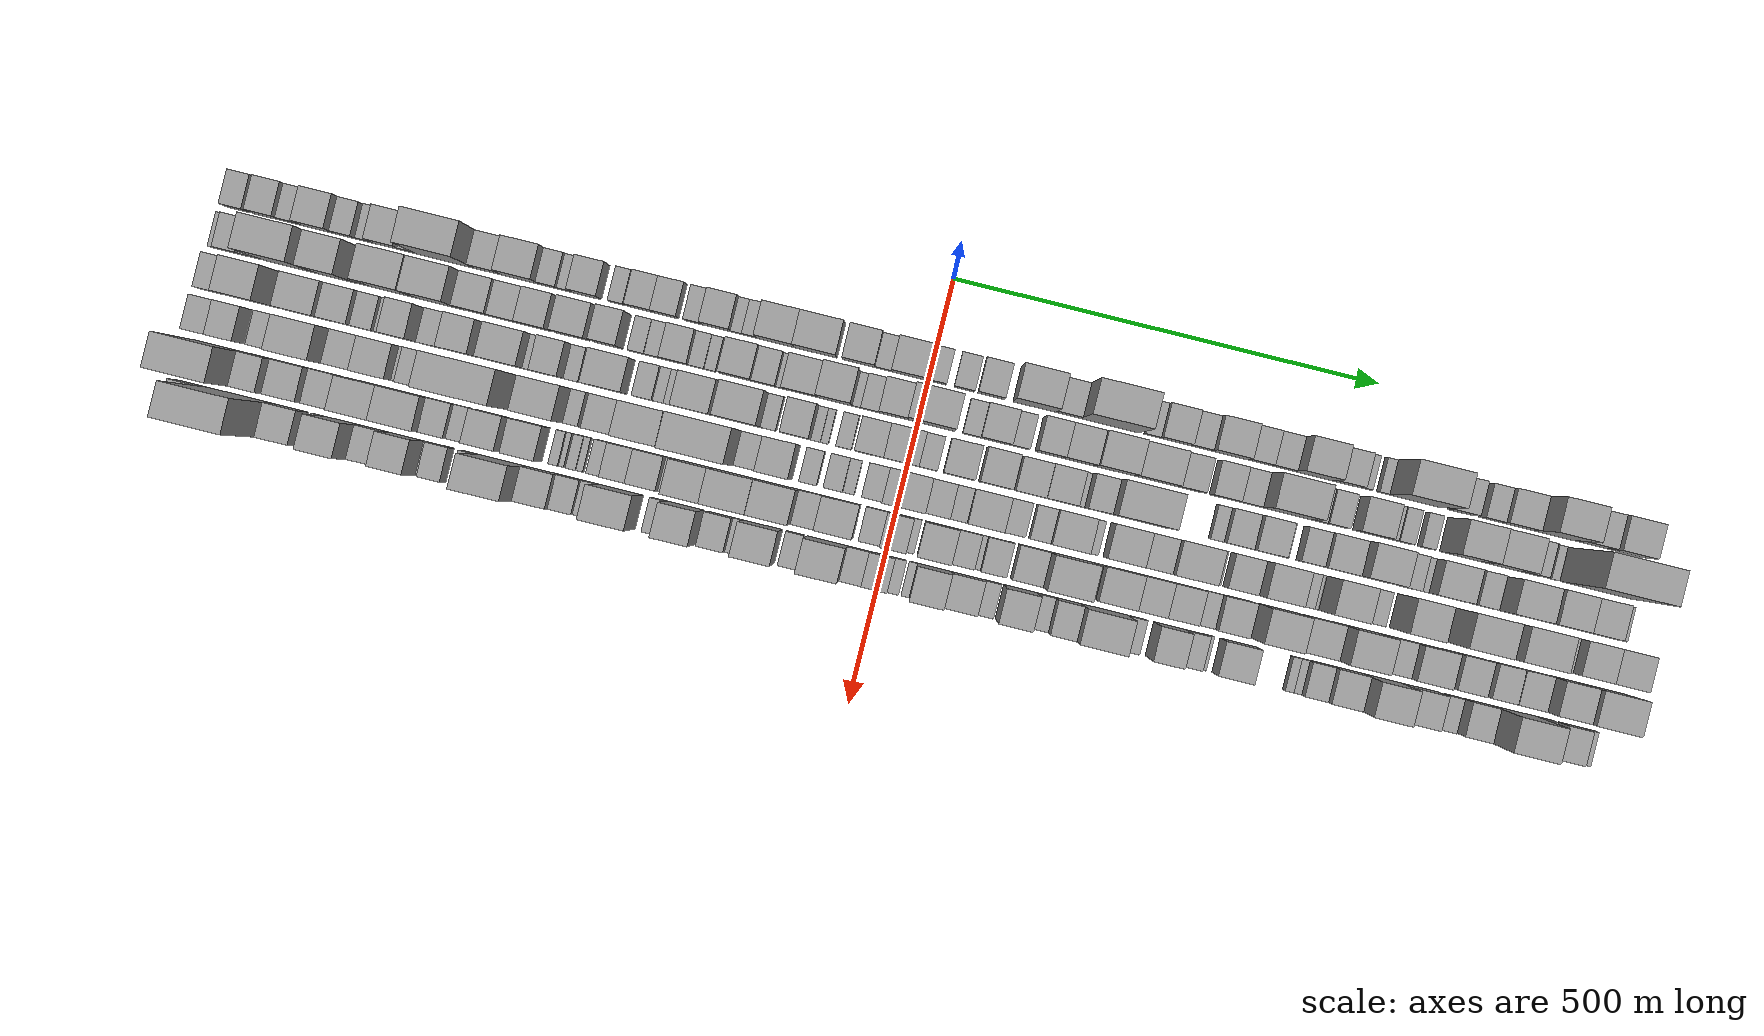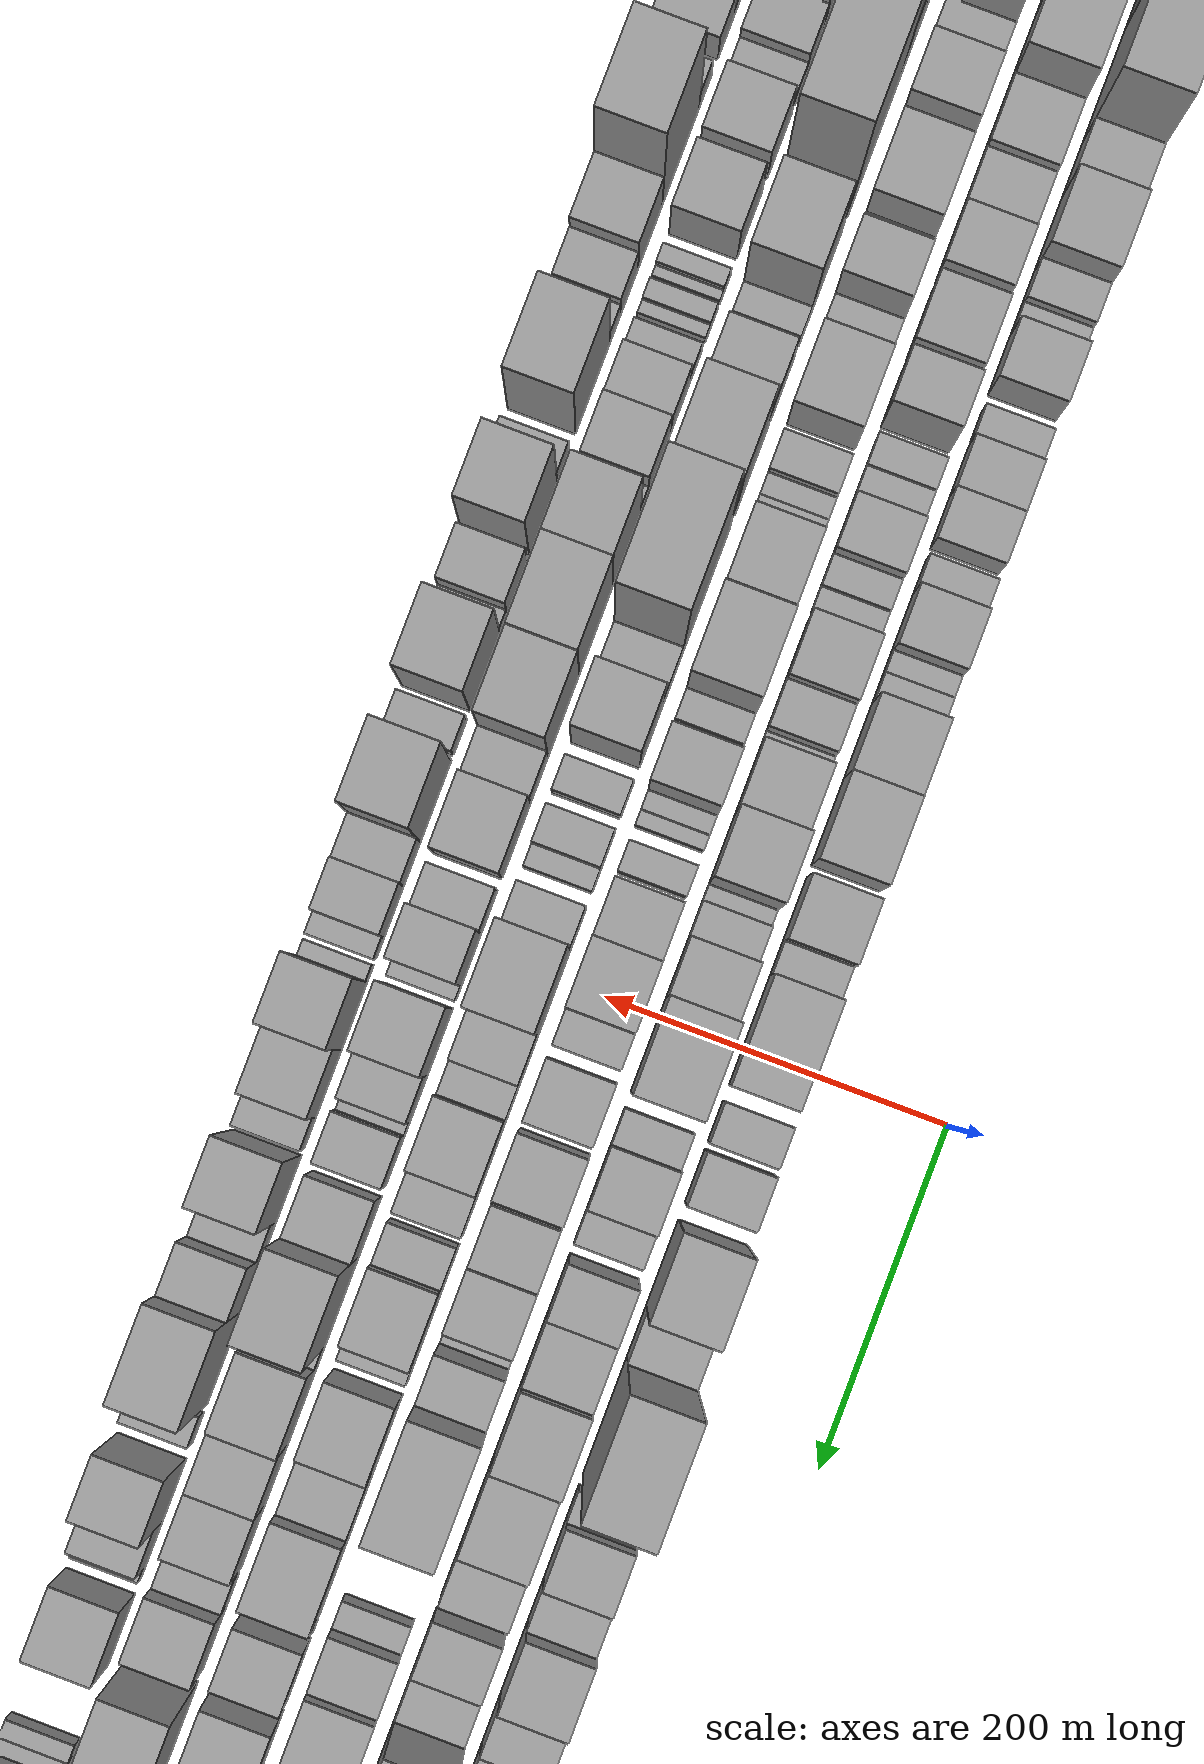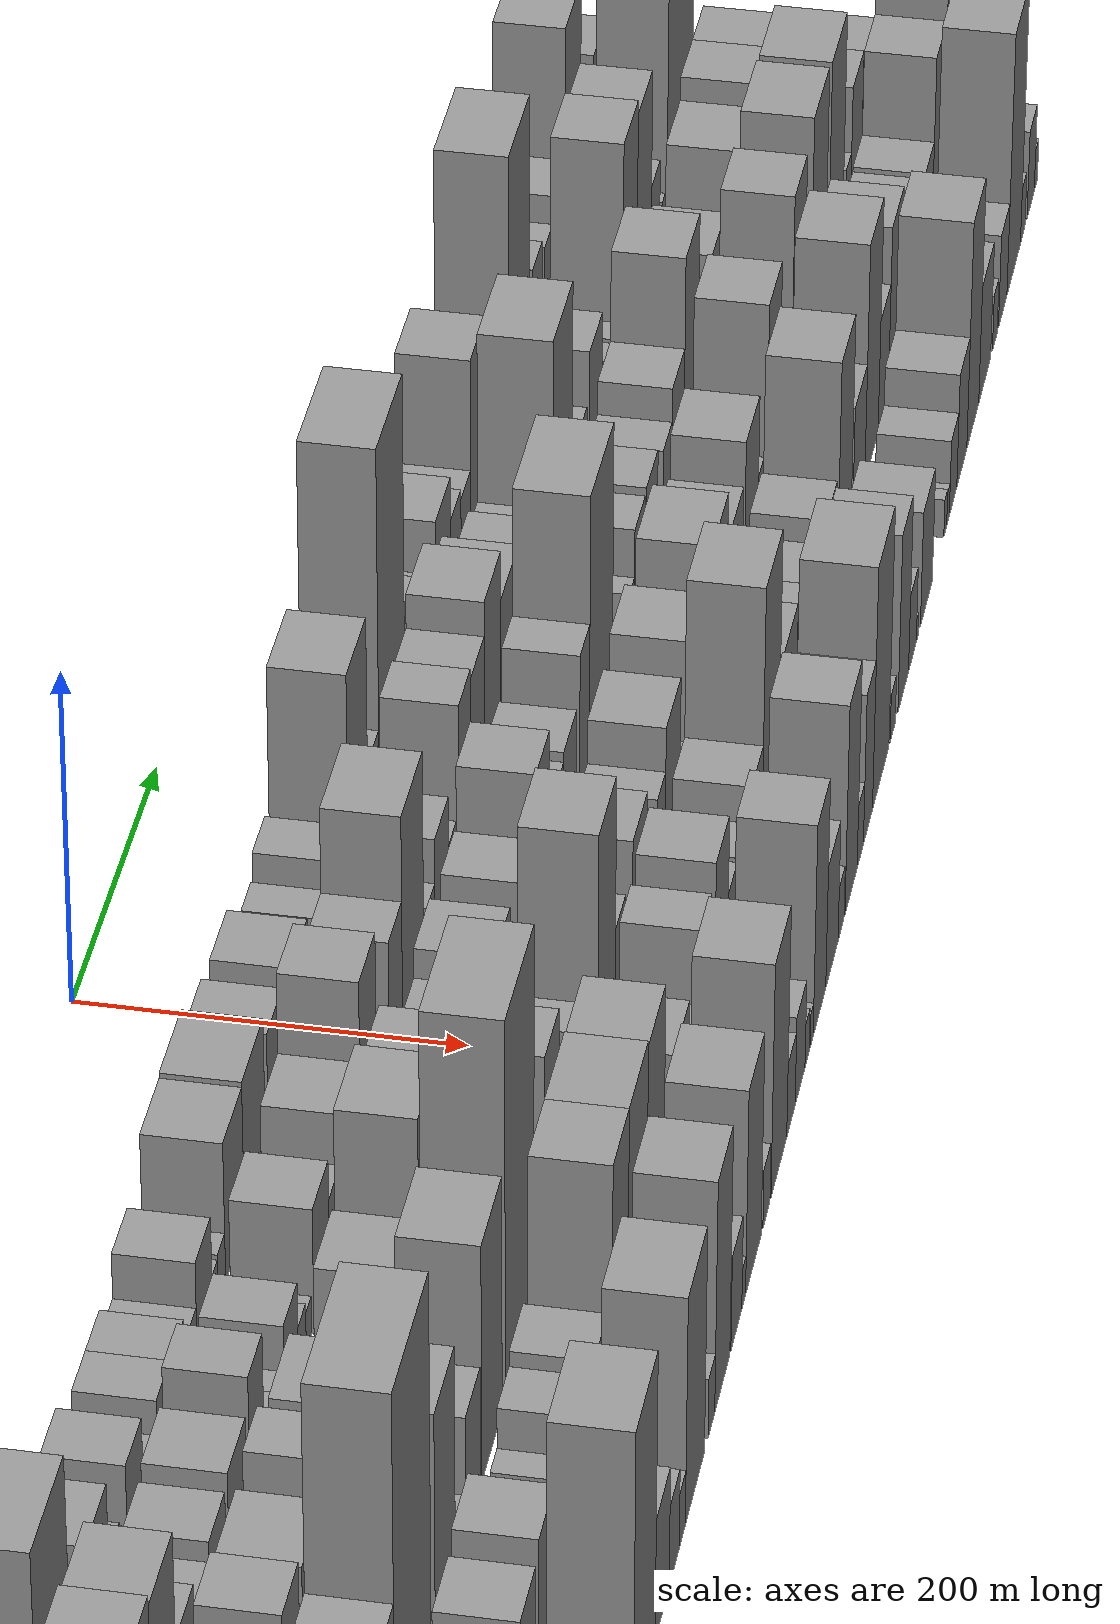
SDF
<sdf version="1.6">
 <world name="default">
  <scene>
   <sky><clouds><speed>12</speed></clouds></sky>
   <ambient>0.4 0.4 0.4 1</ambient>
   <background>0.7 0.7 0.7 1</background>
   <shadows>1</shadows>
  </scene>
  <gravity>0 0 -9.8066</gravity>
  <magnetic_field>6e-06 2.3e-05 -4.2e-05</magnetic_field>
  <physics default="0" name="default_physics" type="ode">
   <ode>
    <solver>
     <type>quick</type>
     <iters>10</iters>
     <sor>1.0</sor>
     <use_dynamic_moi_rescaling>0</use_dynamic_moi_rescaling>
    </solver>
    <constraints>
     <cfm>0</cfm>
     <erp>0.2</erp>
     <contact_max_correcting_vel>100</contact_max_correcting_vel>
     <contact_surface_layer>0.001</contact_surface_layer>
    </constraints>
   </ode>
   <max_step_size>0.004</max_step_size>
   <real_time_factor>1</real_time_factor>
   <real_time_update_rate>250</real_time_update_rate>
  </physics>
  <light name="sun" type="directional">
   <pose>0 0 10 0 0 0</pose>
   <diffuse>0.8 0.8 0.8 1</diffuse>
   <specular>0.2 0.2 0.2 1</specular>
   <attenuation>
    <range>1000</range>
    <constant>0.9</constant>
    <linear>0.01</linear>
    <quadratic>0.001</quadratic>
   </attenuation>
   <direction>-0.5 0.1 -0.9</direction>
  </light>
  <model name="building_1">
   <static>1</static>
   <pose>100.0000 -810.9482 0 0.000000 0.000000 0.000000</pose>
   <link name="link">
    <pose>0 0 24.00 0 0 0</pose>
    <collision name="collision"><geometry><box><size>40.0000 26.1037 48.0000</size></box></geometry></collision>
    <visual name="visual">
     <cast_shadows>0</cast_shadows>
     <geometry><box><size>40.0000 26.1037 48.0000</size></box></geometry>
     <material>
      <script>
       <uri>model://grey_wall/materials/scripts</uri>
       <uri>model://grey_wall/materials/textures</uri>
       <name>vrc/grey_wall</name>
      </script>
     </material>
    </visual>
   </link>
  </model>
  <model name="building_2">
   <static>1</static>
   <pose>100.0000 -776.8065 0 0.000000 0.000000 0.000000</pose>
   <link name="link">
    <pose>0 0 28.50 0 0 0</pose>
    <collision name="collision"><geometry><box><size>40.0000 32.1797 57.0000</size></box></geometry></collision>
    <visual name="visual">
     <cast_shadows>0</cast_shadows>
     <geometry><box><size>40.0000 32.1797 57.0000</size></box></geometry>
     <material>
      <script>
       <uri>model://grey_wall/materials/scripts</uri>
       <uri>model://grey_wall/materials/textures</uri>
       <name>vrc/grey_wall</name>
      </script>
     </material>
    </visual>
   </link>
  </model>
  <model name="building_3">
   <static>1</static>
   <pose>100.0000 -749.7164 0 0.000000 0.000000 0.000000</pose>
   <link name="link">
    <pose>0 0 19.50 0 0 0</pose>
    <collision name="collision"><geometry><box><size>40.0000 22.0005 39.0000</size></box></geometry></collision>
    <visual name="visual">
     <cast_shadows>0</cast_shadows>
     <geometry><box><size>40.0000 22.0005 39.0000</size></box></geometry>
     <material>
      <script>
       <uri>model://grey_wall/materials/scripts</uri>
       <uri>model://grey_wall/materials/textures</uri>
       <name>vrc/grey_wall</name>
      </script>
     </material>
    </visual>
   </link>
  </model>
  <model name="building_4">
   <static>1</static>
   <pose>100.0000 -716.6005 0 0.000000 0.000000 0.000000</pose>
   <link name="link">
    <pose>0 0 36.00 0 0 0</pose>
    <collision name="collision"><geometry><box><size>40.0000 38.2311 72.0000</size></box></geometry></collision>
    <visual name="visual">
     <cast_shadows>0</cast_shadows>
     <geometry><box><size>40.0000 38.2311 72.0000</size></box></geometry>
     <material>
      <script>
       <uri>model://grey_wall/materials/scripts</uri>
       <uri>model://grey_wall/materials/textures</uri>
       <name>vrc/grey_wall</name>
      </script>
     </material>
    </visual>
   </link>
  </model>
  <model name="building_5">
   <static>1</static>
   <pose>100.0000 -685.0904 0 0.000000 0.000000 0.000000</pose>
   <link name="link">
    <pose>0 0 21.00 0 0 0</pose>
    <collision name="collision"><geometry><box><size>40.0000 24.7891 42.0000</size></box></geometry></collision>
    <visual name="visual">
     <cast_shadows>0</cast_shadows>
     <geometry><box><size>40.0000 24.7891 42.0000</size></box></geometry>
     <material>
      <script>
       <uri>model://grey_wall/materials/scripts</uri>
       <uri>model://grey_wall/materials/textures</uri>
       <name>vrc/grey_wall</name>
      </script>
     </material>
    </visual>
   </link>
  </model>
  <model name="building_6">
   <static>1</static>
   <pose>100.0000 -661.8054 0 0.000000 0.000000 0.000000</pose>
   <link name="link">
    <pose>0 0 15.00 0 0 0</pose>
    <collision name="collision"><geometry><box><size>40.0000 15.7809 30.0000</size></box></geometry></collision>
    <visual name="visual">
     <cast_shadows>0</cast_shadows>
     <geometry><box><size>40.0000 15.7809 30.0000</size></box></geometry>
     <material>
      <script>
       <uri>model://grey_wall/materials/scripts</uri>
       <uri>model://grey_wall/materials/textures</uri>
       <name>vrc/grey_wall</name>
      </script>
     </material>
    </visual>
   </link>
  </model>
  <model name="building_7">
   <static>1</static>
   <pose>100.0000 -636.8099 0 0.000000 0.000000 0.000000</pose>
   <link name="link">
    <pose>0 0 31.50 0 0 0</pose>
    <collision name="collision"><geometry><box><size>40.0000 34.2101 63.0000</size></box></geometry></collision>
    <visual name="visual">
     <cast_shadows>0</cast_shadows>
     <geometry><box><size>40.0000 34.2101 63.0000</size></box></geometry>
     <material>
      <script>
       <uri>model://grey_wall/materials/scripts</uri>
       <uri>model://grey_wall/materials/textures</uri>
       <name>vrc/grey_wall</name>
      </script>
     </material>
    </visual>
   </link>
  </model>
  <model name="building_8">
   <static>1</static>
   <pose>100.0000 -610.7147 0 0.000000 0.000000 0.000000</pose>
   <link name="link">
    <pose>0 0 16.50 0 0 0</pose>
    <collision name="collision"><geometry><box><size>40.0000 17.9803 33.0000</size></box></geometry></collision>
    <visual name="visual">
     <cast_shadows>0</cast_shadows>
     <geometry><box><size>40.0000 17.9803 33.0000</size></box></geometry>
     <material>
      <script>
       <uri>model://grey_wall/materials/scripts</uri>
       <uri>model://grey_wall/materials/textures</uri>
       <name>vrc/grey_wall</name>
      </script>
     </material>
    </visual>
   </link>
  </model>
  <model name="building_9">
   <static>1</static>
   <pose>100.0000 -568.2973 0 0.000000 0.000000 0.000000</pose>
   <link name="link">
    <pose>0 0 84.00 0 0 0</pose>
    <collision name="collision"><geometry><box><size>40.0000 66.8545 168.0000</size></box></geometry></collision>
    <visual name="visual">
     <cast_shadows>0</cast_shadows>
     <geometry><box><size>40.0000 66.8545 168.0000</size></box></geometry>
     <material>
      <script>
       <uri>model://grey_wall/materials/scripts</uri>
       <uri>model://grey_wall/materials/textures</uri>
       <name>vrc/grey_wall</name>
      </script>
     </material>
    </visual>
   </link>
  </model>
  <model name="building_10">
   <static>1</static>
   <pose>100.0000 -518.1733 0 0.000000 0.000000 0.000000</pose>
   <link name="link">
    <pose>0 0 30.00 0 0 0</pose>
    <collision name="collision"><geometry><box><size>40.0000 33.3936 60.0000</size></box></geometry></collision>
    <visual name="visual">
     <cast_shadows>0</cast_shadows>
     <geometry><box><size>40.0000 33.3936 60.0000</size></box></geometry>
     <material>
      <script>
       <uri>model://grey_wall/materials/scripts</uri>
       <uri>model://grey_wall/materials/textures</uri>
       <name>vrc/grey_wall</name>
      </script>
     </material>
    </visual>
   </link>
  </model>
  <model name="building_11">
   <static>1</static>
   <pose>100.0000 -479.3493 0 0.000000 0.000000 0.000000</pose>
   <link name="link">
    <pose>0 0 43.50 0 0 0</pose>
    <collision name="collision"><geometry><box><size>40.0000 44.2543 87.0000</size></box></geometry></collision>
    <visual name="visual">
     <cast_shadows>0</cast_shadows>
     <geometry><box><size>40.0000 44.2543 87.0000</size></box></geometry>
     <material>
      <script>
       <uri>model://grey_wall/materials/scripts</uri>
       <uri>model://grey_wall/materials/textures</uri>
       <name>vrc/grey_wall</name>
      </script>
     </material>
    </visual>
   </link>
  </model>
  <model name="building_12">
   <static>1</static>
   <pose>100.0000 -445.8063 0 0.000000 0.000000 0.000000</pose>
   <link name="link">
    <pose>0 0 22.50 0 0 0</pose>
    <collision name="collision"><geometry><box><size>40.0000 22.8317 45.0000</size></box></geometry></collision>
    <visual name="visual">
     <cast_shadows>0</cast_shadows>
     <geometry><box><size>40.0000 22.8317 45.0000</size></box></geometry>
     <material>
      <script>
       <uri>model://grey_wall/materials/scripts</uri>
       <uri>model://grey_wall/materials/textures</uri>
       <name>vrc/grey_wall</name>
      </script>
     </material>
    </visual>
   </link>
  </model>
  <model name="building_13">
   <static>1</static>
   <pose>100.0000 -426.7800 0 0.000000 0.000000 0.000000</pose>
   <link name="link">
    <pose>0 0 15.00 0 0 0</pose>
    <collision name="collision"><geometry><box><size>40.0000 15.2208 30.0000</size></box></geometry></collision>
    <visual name="visual">
     <cast_shadows>0</cast_shadows>
     <geometry><box><size>40.0000 15.2208 30.0000</size></box></geometry>
     <material>
      <script>
       <uri>model://grey_wall/materials/scripts</uri>
       <uri>model://grey_wall/materials/textures</uri>
       <name>vrc/grey_wall</name>
      </script>
     </material>
    </visual>
   </link>
  </model>
  <model name="building_14">
   <static>1</static>
   <pose>100.0000 -401.9076 0 0.000000 0.000000 0.000000</pose>
   <link name="link">
    <pose>0 0 33.00 0 0 0</pose>
    <collision name="collision"><geometry><box><size>40.0000 34.5240 66.0000</size></box></geometry></collision>
    <visual name="visual">
     <cast_shadows>0</cast_shadows>
     <geometry><box><size>40.0000 34.5240 66.0000</size></box></geometry>
     <material>
      <script>
       <uri>model://grey_wall/materials/scripts</uri>
       <uri>model://grey_wall/materials/textures</uri>
       <name>vrc/grey_wall</name>
      </script>
     </material>
    </visual>
   </link>
  </model>
  <model name="building_15">
   <static>1</static>
   <pose>100.0000 -365.7893 0 0.000000 0.000000 0.000000</pose>
   <link name="link">
    <pose>0 0 16.50 0 0 0</pose>
    <collision name="collision"><geometry><box><size>40.0000 17.7125 33.0000</size></box></geometry></collision>
    <visual name="visual">
     <cast_shadows>0</cast_shadows>
     <geometry><box><size>40.0000 17.7125 33.0000</size></box></geometry>
     <material>
      <script>
       <uri>model://grey_wall/materials/scripts</uri>
       <uri>model://grey_wall/materials/textures</uri>
       <name>vrc/grey_wall</name>
      </script>
     </material>
    </visual>
   </link>
  </model>
  <model name="building_16">
   <static>1</static>
   <pose>100.0000 -338.9634 0 0.000000 0.000000 0.000000</pose>
   <link name="link">
    <pose>0 0 25.50 0 0 0</pose>
    <collision name="collision"><geometry><box><size>40.0000 29.9394 51.0000</size></box></geometry></collision>
    <visual name="visual">
     <cast_shadows>0</cast_shadows>
     <geometry><box><size>40.0000 29.9394 51.0000</size></box></geometry>
     <material>
      <script>
       <uri>model://grey_wall/materials/scripts</uri>
       <uri>model://grey_wall/materials/textures</uri>
       <name>vrc/grey_wall</name>
      </script>
     </material>
    </visual>
   </link>
  </model>
  <model name="building_17">
   <static>1</static>
   <pose>100.0000 -308.8992 0 0.000000 0.000000 0.000000</pose>
   <link name="link">
    <pose>0 0 25.50 0 0 0</pose>
    <collision name="collision"><geometry><box><size>40.0000 30.1890 51.0000</size></box></geometry></collision>
    <visual name="visual">
     <cast_shadows>0</cast_shadows>
     <geometry><box><size>40.0000 30.1890 51.0000</size></box></geometry>
     <material>
      <script>
       <uri>model://grey_wall/materials/scripts</uri>
       <uri>model://grey_wall/materials/textures</uri>
       <name>vrc/grey_wall</name>
      </script>
     </material>
    </visual>
   </link>
  </model>
  <model name="building_18">
   <static>1</static>
   <pose>100.0000 -276.6746 0 0.000000 0.000000 0.000000</pose>
   <link name="link">
    <pose>0 0 18.00 0 0 0</pose>
    <collision name="collision"><geometry><box><size>40.0000 20.2602 36.0000</size></box></geometry></collision>
    <visual name="visual">
     <cast_shadows>0</cast_shadows>
     <geometry><box><size>40.0000 20.2602 36.0000</size></box></geometry>
     <material>
      <script>
       <uri>model://grey_wall/materials/scripts</uri>
       <uri>model://grey_wall/materials/textures</uri>
       <name>vrc/grey_wall</name>
      </script>
     </material>
    </visual>
   </link>
  </model>
  <model name="building_19">
   <static>1</static>
   <pose>100.0000 -249.0902 0 0.000000 0.000000 0.000000</pose>
   <link name="link">
    <pose>0 0 31.50 0 0 0</pose>
    <collision name="collision"><geometry><box><size>40.0000 34.9087 63.0000</size></box></geometry></collision>
    <visual name="visual">
     <cast_shadows>0</cast_shadows>
     <geometry><box><size>40.0000 34.9087 63.0000</size></box></geometry>
     <material>
      <script>
       <uri>model://grey_wall/materials/scripts</uri>
       <uri>model://grey_wall/materials/textures</uri>
       <name>vrc/grey_wall</name>
      </script>
     </material>
    </visual>
   </link>
  </model>
  <model name="building_20">
   <static>1</static>
   <pose>100.0000 -225.1248 0 0.000000 0.000000 0.000000</pose>
   <link name="link">
    <pose>0 0 13.50 0 0 0</pose>
    <collision name="collision"><geometry><box><size>40.0000 13.0221 27.0000</size></box></geometry></collision>
    <visual name="visual">
     <cast_shadows>0</cast_shadows>
     <geometry><box><size>40.0000 13.0221 27.0000</size></box></geometry>
     <material>
      <script>
       <uri>model://grey_wall/materials/scripts</uri>
       <uri>model://grey_wall/materials/textures</uri>
       <name>vrc/grey_wall</name>
      </script>
     </material>
    </visual>
   </link>
  </model>
  <model name="building_21">
   <static>1</static>
   <pose>100.0000 -210.2478 0 0.000000 0.000000 0.000000</pose>
   <link name="link">
    <pose>0 0 15.00 0 0 0</pose>
    <collision name="collision"><geometry><box><size>40.0000 16.7318 30.0000</size></box></geometry></collision>
    <visual name="visual">
     <cast_shadows>0</cast_shadows>
     <geometry><box><size>40.0000 16.7318 30.0000</size></box></geometry>
     <material>
      <script>
       <uri>model://grey_wall/materials/scripts</uri>
       <uri>model://grey_wall/materials/textures</uri>
       <name>vrc/grey_wall</name>
      </script>
     </material>
    </visual>
   </link>
  </model>
  <model name="building_22">
   <static>1</static>
   <pose>100.0000 -179.8507 0 0.000000 0.000000 0.000000</pose>
   <link name="link">
    <pose>0 0 42.00 0 0 0</pose>
    <collision name="collision"><geometry><box><size>40.0000 44.0624 84.0000</size></box></geometry></collision>
    <visual name="visual">
     <cast_shadows>0</cast_shadows>
     <geometry><box><size>40.0000 44.0624 84.0000</size></box></geometry>
     <material>
      <script>
       <uri>model://grey_wall/materials/scripts</uri>
       <uri>model://grey_wall/materials/textures</uri>
       <name>vrc/grey_wall</name>
      </script>
     </material>
    </visual>
   </link>
  </model>
  <model name="building_23">
   <static>1</static>
   <pose>100.0000 -132.6121 0 0.000000 0.000000 0.000000</pose>
   <link name="link">
    <pose>0 0 43.50 0 0 0</pose>
    <collision name="collision"><geometry><box><size>40.0000 50.4148 87.0000</size></box></geometry></collision>
    <visual name="visual">
     <cast_shadows>0</cast_shadows>
     <geometry><box><size>40.0000 50.4148 87.0000</size></box></geometry>
     <material>
      <script>
       <uri>model://grey_wall/materials/scripts</uri>
       <uri>model://grey_wall/materials/textures</uri>
       <name>vrc/grey_wall</name>
      </script>
     </material>
    </visual>
   </link>
  </model>
  <model name="building_24">
   <static>1</static>
   <pose>100.0000 -81.5490 0 0.000000 0.000000 0.000000</pose>
   <link name="link">
    <pose>0 0 36.00 0 0 0</pose>
    <collision name="collision"><geometry><box><size>40.0000 37.7114 72.0000</size></box></geometry></collision>
    <visual name="visual">
     <cast_shadows>0</cast_shadows>
     <geometry><box><size>40.0000 37.7114 72.0000</size></box></geometry>
     <material>
      <script>
       <uri>model://grey_wall/materials/scripts</uri>
       <uri>model://grey_wall/materials/textures</uri>
       <name>vrc/grey_wall</name>
      </script>
     </material>
    </visual>
   </link>
  </model>
  <model name="building_25">
   <static>1</static>
   <pose>100.0000 -52.9410 0 0.000000 0.000000 0.000000</pose>
   <link name="link">
    <pose>0 0 16.50 0 0 0</pose>
    <collision name="collision"><geometry><box><size>40.0000 19.5046 33.0000</size></box></geometry></collision>
    <visual name="visual">
     <cast_shadows>0</cast_shadows>
     <geometry><box><size>40.0000 19.5046 33.0000</size></box></geometry>
     <material>
      <script>
       <uri>model://grey_wall/materials/scripts</uri>
       <uri>model://grey_wall/materials/textures</uri>
       <name>vrc/grey_wall</name>
      </script>
     </material>
    </visual>
   </link>
  </model>
  <model name="building_26">
   <static>1</static>
   <pose>100.0000 -22.6887 0 0.000000 0.000000 0.000000</pose>
   <link name="link">
    <pose>0 0 34.50 0 0 0</pose>
    <collision name="collision"><geometry><box><size>40.0000 40.9999 69.0000</size></box></geometry></collision>
    <visual name="visual">
     <cast_shadows>0</cast_shadows>
     <geometry><box><size>40.0000 40.9999 69.0000</size></box></geometry>
     <material>
      <script>
       <uri>model://grey_wall/materials/scripts</uri>
       <uri>model://grey_wall/materials/textures</uri>
       <name>vrc/grey_wall</name>
      </script>
     </material>
    </visual>
   </link>
  </model>
  <model name="building_27">
   <static>1</static>
   <pose>100.0000 9.3571 0 0.000000 0.000000 0.000000</pose>
   <link name="link">
    <pose>0 0 22.50 0 0 0</pose>
    <collision name="collision"><geometry><box><size>40.0000 23.0918 45.0000</size></box></geometry></collision>
    <visual name="visual">
     <cast_shadows>0</cast_shadows>
     <geometry><box><size>40.0000 23.0918 45.0000</size></box></geometry>
     <material>
      <script>
       <uri>model://grey_wall/materials/scripts</uri>
       <uri>model://grey_wall/materials/textures</uri>
       <name>vrc/grey_wall</name>
      </script>
     </material>
    </visual>
   </link>
  </model>
  <model name="building_28">
   <static>1</static>
   <pose>100.0000 41.8925 0 0.000000 0.000000 0.000000</pose>
   <link name="link">
    <pose>0 0 22.50 0 0 0</pose>
    <collision name="collision"><geometry><box><size>40.0000 23.9791 45.0000</size></box></geometry></collision>
    <visual name="visual">
     <cast_shadows>0</cast_shadows>
     <geometry><box><size>40.0000 23.9791 45.0000</size></box></geometry>
     <material>
      <script>
       <uri>model://grey_wall/materials/scripts</uri>
       <uri>model://grey_wall/materials/textures</uri>
       <name>vrc/grey_wall</name>
      </script>
     </material>
    </visual>
   </link>
  </model>
  <model name="building_29">
   <static>1</static>
   <pose>100.0000 73.4881 0 0.000000 0.000000 0.000000</pose>
   <link name="link">
    <pose>0 0 30.00 0 0 0</pose>
    <collision name="collision"><geometry><box><size>40.0000 31.2120 60.0000</size></box></geometry></collision>
    <visual name="visual">
     <cast_shadows>0</cast_shadows>
     <geometry><box><size>40.0000 31.2120 60.0000</size></box></geometry>
     <material>
      <script>
       <uri>model://grey_wall/materials/scripts</uri>
       <uri>model://grey_wall/materials/textures</uri>
       <name>vrc/grey_wall</name>
      </script>
     </material>
    </visual>
   </link>
  </model>
  <model name="building_30">
   <static>1</static>
   <pose>100.0000 124.2129 0 0.000000 0.000000 0.000000</pose>
   <link name="link">
    <pose>0 0 72.00 0 0 0</pose>
    <collision name="collision"><geometry><box><size>40.0000 50.2375 144.0000</size></box></geometry></collision>
    <visual name="visual">
     <cast_shadows>0</cast_shadows>
     <geometry><box><size>40.0000 50.2375 144.0000</size></box></geometry>
     <material>
      <script>
       <uri>model://grey_wall/materials/scripts</uri>
       <uri>model://grey_wall/materials/textures</uri>
       <name>vrc/grey_wall</name>
      </script>
     </material>
    </visual>
   </link>
  </model>
  <model name="building_31">
   <static>1</static>
   <pose>100.0000 164.1089 0 0.000000 0.000000 0.000000</pose>
   <link name="link">
    <pose>0 0 27.00 0 0 0</pose>
    <collision name="collision"><geometry><box><size>40.0000 29.5546 54.0000</size></box></geometry></collision>
    <visual name="visual">
     <cast_shadows>0</cast_shadows>
     <geometry><box><size>40.0000 29.5546 54.0000</size></box></geometry>
     <material>
      <script>
       <uri>model://grey_wall/materials/scripts</uri>
       <uri>model://grey_wall/materials/textures</uri>
       <name>vrc/grey_wall</name>
      </script>
     </material>
    </visual>
   </link>
  </model>
  <model name="building_32">
   <static>1</static>
   <pose>100.0000 213.0105 0 0.000000 0.000000 0.000000</pose>
   <link name="link">
    <pose>0 0 112.50 0 0 0</pose>
    <collision name="collision"><geometry><box><size>40.0000 68.2486 225.0000</size></box></geometry></collision>
    <visual name="visual">
     <cast_shadows>0</cast_shadows>
     <geometry><box><size>40.0000 68.2486 225.0000</size></box></geometry>
     <material>
      <script>
       <uri>model://grey_wall/materials/scripts</uri>
       <uri>model://grey_wall/materials/textures</uri>
       <name>vrc/grey_wall</name>
      </script>
     </material>
    </visual>
   </link>
  </model>
  <model name="building_33">
   <static>1</static>
   <pose>100.0000 262.2809 0 0.000000 0.000000 0.000000</pose>
   <link name="link">
    <pose>0 0 16.50 0 0 0</pose>
    <collision name="collision"><geometry><box><size>40.0000 18.2922 33.0000</size></box></geometry></collision>
    <visual name="visual">
     <cast_shadows>0</cast_shadows>
     <geometry><box><size>40.0000 18.2922 33.0000</size></box></geometry>
     <material>
      <script>
       <uri>model://grey_wall/materials/scripts</uri>
       <uri>model://grey_wall/materials/textures</uri>
       <name>vrc/grey_wall</name>
      </script>
     </material>
    </visual>
   </link>
  </model>
  <model name="building_34">
   <static>1</static>
   <pose>100.0000 289.1809 0 0.000000 0.000000 0.000000</pose>
   <link name="link">
    <pose>0 0 30.00 0 0 0</pose>
    <collision name="collision"><geometry><box><size>40.0000 35.5078 60.0000</size></box></geometry></collision>
    <visual name="visual">
     <cast_shadows>0</cast_shadows>
     <geometry><box><size>40.0000 35.5078 60.0000</size></box></geometry>
     <material>
      <script>
       <uri>model://grey_wall/materials/scripts</uri>
       <uri>model://grey_wall/materials/textures</uri>
       <name>vrc/grey_wall</name>
      </script>
     </material>
    </visual>
   </link>
  </model>
  <model name="building_35">
   <static>1</static>
   <pose>100.0000 319.2703 0 0.000000 0.000000 0.000000</pose>
   <link name="link">
    <pose>0 0 22.50 0 0 0</pose>
    <collision name="collision"><geometry><box><size>40.0000 24.6710 45.0000</size></box></geometry></collision>
    <visual name="visual">
     <cast_shadows>0</cast_shadows>
     <geometry><box><size>40.0000 24.6710 45.0000</size></box></geometry>
     <material>
      <script>
       <uri>model://grey_wall/materials/scripts</uri>
       <uri>model://grey_wall/materials/textures</uri>
       <name>vrc/grey_wall</name>
      </script>
     </material>
    </visual>
   </link>
  </model>
  <model name="building_36">
   <static>1</static>
   <pose>100.0000 352.4408 0 0.000000 0.000000 0.000000</pose>
   <link name="link">
    <pose>0 0 39.00 0 0 0</pose>
    <collision name="collision"><geometry><box><size>40.0000 41.6700 78.0000</size></box></geometry></collision>
    <visual name="visual">
     <cast_shadows>0</cast_shadows>
     <geometry><box><size>40.0000 41.6700 78.0000</size></box></geometry>
     <material>
      <script>
       <uri>model://grey_wall/materials/scripts</uri>
       <uri>model://grey_wall/materials/textures</uri>
       <name>vrc/grey_wall</name>
      </script>
     </material>
    </visual>
   </link>
  </model>
  <model name="building_37">
   <static>1</static>
   <pose>100.0000 387.5940 0 0.000000 0.000000 0.000000</pose>
   <link name="link">
    <pose>0 0 25.50 0 0 0</pose>
    <collision name="collision"><geometry><box><size>40.0000 28.6363 51.0000</size></box></geometry></collision>
    <visual name="visual">
     <cast_shadows>0</cast_shadows>
     <geometry><box><size>40.0000 28.6363 51.0000</size></box></geometry>
     <material>
      <script>
       <uri>model://grey_wall/materials/scripts</uri>
       <uri>model://grey_wall/materials/textures</uri>
       <name>vrc/grey_wall</name>
      </script>
     </material>
    </visual>
   </link>
  </model>
  <model name="building_38">
   <static>1</static>
   <pose>100.0000 415.3462 0 0.000000 0.000000 0.000000</pose>
   <link name="link">
    <pose>0 0 22.50 0 0 0</pose>
    <collision name="collision"><geometry><box><size>40.0000 26.8681 45.0000</size></box></geometry></collision>
    <visual name="visual">
     <cast_shadows>0</cast_shadows>
     <geometry><box><size>40.0000 26.8681 45.0000</size></box></geometry>
     <material>
      <script>
       <uri>model://grey_wall/materials/scripts</uri>
       <uri>model://grey_wall/materials/textures</uri>
       <name>vrc/grey_wall</name>
      </script>
     </material>
    </visual>
   </link>
  </model>
  <model name="building_39">
   <static>1</static>
   <pose>100.0000 450.6883 0 0.000000 0.000000 0.000000</pose>
   <link name="link">
    <pose>0 0 57.00 0 0 0</pose>
    <collision name="collision"><geometry><box><size>40.0000 43.8163 114.0000</size></box></geometry></collision>
    <visual name="visual">
     <cast_shadows>0</cast_shadows>
     <geometry><box><size>40.0000 43.8163 114.0000</size></box></geometry>
     <material>
      <script>
       <uri>model://grey_wall/materials/scripts</uri>
       <uri>model://grey_wall/materials/textures</uri>
       <name>vrc/grey_wall</name>
      </script>
     </material>
    </visual>
   </link>
  </model>
  <model name="building_40">
   <static>1</static>
   <pose>100.0000 491.5645 0 0.000000 0.000000 0.000000</pose>
   <link name="link">
    <pose>0 0 27.00 0 0 0</pose>
    <collision name="collision"><geometry><box><size>40.0000 31.9362 54.0000</size></box></geometry></collision>
    <visual name="visual">
     <cast_shadows>0</cast_shadows>
     <geometry><box><size>40.0000 31.9362 54.0000</size></box></geometry>
     <material>
      <script>
       <uri>model://grey_wall/materials/scripts</uri>
       <uri>model://grey_wall/materials/textures</uri>
       <name>vrc/grey_wall</name>
      </script>
     </material>
    </visual>
   </link>
  </model>
  <model name="building_41">
   <static>1</static>
   <pose>100.0000 513.2222 0 0.000000 0.000000 0.000000</pose>
   <link name="link">
    <pose>0 0 13.50 0 0 0</pose>
    <collision name="collision"><geometry><box><size>40.0000 11.3791 27.0000</size></box></geometry></collision>
    <visual name="visual">
     <cast_shadows>0</cast_shadows>
     <geometry><box><size>40.0000 11.3791 27.0000</size></box></geometry>
     <material>
      <script>
       <uri>model://grey_wall/materials/scripts</uri>
       <uri>model://grey_wall/materials/textures</uri>
       <name>vrc/grey_wall</name>
      </script>
     </material>
    </visual>
   </link>
  </model>
  <model name="building_42">
   <static>1</static>
   <pose>100.0000 532.6210 0 0.000000 0.000000 0.000000</pose>
   <link name="link">
    <pose>0 0 13.50 0 0 0</pose>
    <collision name="collision"><geometry><box><size>40.0000 11.4184 27.0000</size></box></geometry></collision>
    <visual name="visual">
     <cast_shadows>0</cast_shadows>
     <geometry><box><size>40.0000 11.4184 27.0000</size></box></geometry>
     <material>
      <script>
       <uri>model://grey_wall/materials/scripts</uri>
       <uri>model://grey_wall/materials/textures</uri>
       <name>vrc/grey_wall</name>
      </script>
     </material>
    </visual>
   </link>
  </model>
  <model name="building_43">
   <static>1</static>
   <pose>100.0000 569.9449 0 0.000000 0.000000 0.000000</pose>
   <link name="link">
    <pose>0 0 85.50 0 0 0</pose>
    <collision name="collision"><geometry><box><size>40.0000 63.2294 171.0000</size></box></geometry></collision>
    <visual name="visual">
     <cast_shadows>0</cast_shadows>
     <geometry><box><size>40.0000 63.2294 171.0000</size></box></geometry>
     <material>
      <script>
       <uri>model://grey_wall/materials/scripts</uri>
       <uri>model://grey_wall/materials/textures</uri>
       <name>vrc/grey_wall</name>
      </script>
     </material>
    </visual>
   </link>
  </model>
  <model name="building_44">
   <static>1</static>
   <pose>100.0000 624.9713 0 0.000000 0.000000 0.000000</pose>
   <link name="link">
    <pose>0 0 27.00 0 0 0</pose>
    <collision name="collision"><geometry><box><size>40.0000 28.8236 54.0000</size></box></geometry></collision>
    <visual name="visual">
     <cast_shadows>0</cast_shadows>
     <geometry><box><size>40.0000 28.8236 54.0000</size></box></geometry>
     <material>
      <script>
       <uri>model://grey_wall/materials/scripts</uri>
       <uri>model://grey_wall/materials/textures</uri>
       <name>vrc/grey_wall</name>
      </script>
     </material>
    </visual>
   </link>
  </model>
  <model name="building_45">
   <static>1</static>
   <pose>100.0000 659.1716 0 0.000000 0.000000 0.000000</pose>
   <link name="link">
    <pose>0 0 22.50 0 0 0</pose>
    <collision name="collision"><geometry><box><size>40.0000 23.5769 45.0000</size></box></geometry></collision>
    <visual name="visual">
     <cast_shadows>0</cast_shadows>
     <geometry><box><size>40.0000 23.5769 45.0000</size></box></geometry>
     <material>
      <script>
       <uri>model://grey_wall/materials/scripts</uri>
       <uri>model://grey_wall/materials/textures</uri>
       <name>vrc/grey_wall</name>
      </script>
     </material>
    </visual>
   </link>
  </model>
  <model name="building_46">
   <static>1</static>
   <pose>100.0000 689.6804 0 0.000000 0.000000 0.000000</pose>
   <link name="link">
    <pose>0 0 31.50 0 0 0</pose>
    <collision name="collision"><geometry><box><size>40.0000 37.4409 63.0000</size></box></geometry></collision>
    <visual name="visual">
     <cast_shadows>0</cast_shadows>
     <geometry><box><size>40.0000 37.4409 63.0000</size></box></geometry>
     <material>
      <script>
       <uri>model://grey_wall/materials/scripts</uri>
       <uri>model://grey_wall/materials/textures</uri>
       <name>vrc/grey_wall</name>
      </script>
     </material>
    </visual>
   </link>
  </model>
  <model name="building_47">
   <static>1</static>
   <pose>100.0000 732.8744 0 0.000000 0.000000 0.000000</pose>
   <link name="link">
    <pose>0 0 73.50 0 0 0</pose>
    <collision name="collision"><geometry><box><size>40.0000 48.9471 147.0000</size></box></geometry></collision>
    <visual name="visual">
     <cast_shadows>0</cast_shadows>
     <geometry><box><size>40.0000 48.9471 147.0000</size></box></geometry>
     <material>
      <script>
       <uri>model://grey_wall/materials/scripts</uri>
       <uri>model://grey_wall/materials/textures</uri>
       <name>vrc/grey_wall</name>
      </script>
     </material>
    </visual>
   </link>
  </model>
  <model name="building_48">
   <static>1</static>
   <pose>100.0000 776.4161 0 0.000000 0.000000 0.000000</pose>
   <link name="link">
    <pose>0 0 34.50 0 0 0</pose>
    <collision name="collision"><geometry><box><size>40.0000 38.1363 69.0000</size></box></geometry></collision>
    <visual name="visual">
     <cast_shadows>0</cast_shadows>
     <geometry><box><size>40.0000 38.1363 69.0000</size></box></geometry>
     <material>
      <script>
       <uri>model://grey_wall/materials/scripts</uri>
       <uri>model://grey_wall/materials/textures</uri>
       <name>vrc/grey_wall</name>
      </script>
     </material>
    </visual>
   </link>
  </model>
  <model name="building_49">
   <static>1</static>
   <pose>100.0000 819.2254 0 0.000000 0.000000 0.000000</pose>
   <link name="link">
    <pose>0 0 37.50 0 0 0</pose>
    <collision name="collision"><geometry><box><size>40.0000 41.4822 75.0000</size></box></geometry></collision>
    <visual name="visual">
     <cast_shadows>0</cast_shadows>
     <geometry><box><size>40.0000 41.4822 75.0000</size></box></geometry>
     <material>
      <script>
       <uri>model://grey_wall/materials/scripts</uri>
       <uri>model://grey_wall/materials/textures</uri>
       <name>vrc/grey_wall</name>
      </script>
     </material>
    </visual>
   </link>
  </model>
  <model name="building_50">
   <static>1</static>
   <pose>149.0000 -824.2631 0 0.000000 0.000000 0.000000</pose>
   <link name="link">
    <pose>0 0 13.50 0 0 0</pose>
    <collision name="collision"><geometry><box><size>40.0000 11.4738 27.0000</size></box></geometry></collision>
    <visual name="visual">
     <cast_shadows>0</cast_shadows>
     <geometry><box><size>40.0000 11.4738 27.0000</size></box></geometry>
     <material>
      <script>
       <uri>model://grey_wall/materials/scripts</uri>
       <uri>model://grey_wall/materials/textures</uri>
       <name>vrc/grey_wall</name>
      </script>
     </material>
    </visual>
   </link>
  </model>
  <model name="building_51">
   <static>1</static>
   <pose>149.0000 -804.8799 0 0.000000 0.000000 0.000000</pose>
   <link name="link">
    <pose>0 0 27.00 0 0 0</pose>
    <collision name="collision"><geometry><box><size>40.0000 27.2926 54.0000</size></box></geometry></collision>
    <visual name="visual">
     <cast_shadows>0</cast_shadows>
     <geometry><box><size>40.0000 27.2926 54.0000</size></box></geometry>
     <material>
      <script>
       <uri>model://grey_wall/materials/scripts</uri>
       <uri>model://grey_wall/materials/textures</uri>
       <name>vrc/grey_wall</name>
      </script>
     </material>
    </visual>
   </link>
  </model>
  <model name="building_52">
   <static>1</static>
   <pose>149.0000 -781.4099 0 0.000000 0.000000 0.000000</pose>
   <link name="link">
    <pose>0 0 19.50 0 0 0</pose>
    <collision name="collision"><geometry><box><size>40.0000 19.6474 39.0000</size></box></geometry></collision>
    <visual name="visual">
     <cast_shadows>0</cast_shadows>
     <geometry><box><size>40.0000 19.6474 39.0000</size></box></geometry>
     <material>
      <script>
       <uri>model://grey_wall/materials/scripts</uri>
       <uri>model://grey_wall/materials/textures</uri>
       <name>vrc/grey_wall</name>
      </script>
     </material>
    </visual>
   </link>
  </model>
  <model name="building_53">
   <static>1</static>
   <pose>149.0000 -735.4409 0 0.000000 0.000000 0.000000</pose>
   <link name="link">
    <pose>0 0 93.00 0 0 0</pose>
    <collision name="collision"><geometry><box><size>40.0000 62.2906 186.0000</size></box></geometry></collision>
    <visual name="visual">
     <cast_shadows>0</cast_shadows>
     <geometry><box><size>40.0000 62.2906 186.0000</size></box></geometry>
     <material>
      <script>
       <uri>model://grey_wall/materials/scripts</uri>
       <uri>model://grey_wall/materials/textures</uri>
       <name>vrc/grey_wall</name>
      </script>
     </material>
    </visual>
   </link>
  </model>
  <model name="building_54">
   <static>1</static>
   <pose>149.0000 -682.4288 0 0.000000 0.000000 0.000000</pose>
   <link name="link">
    <pose>0 0 70.50 0 0 0</pose>
    <collision name="collision"><geometry><box><size>40.0000 43.7336 141.0000</size></box></geometry></collision>
    <visual name="visual">
     <cast_shadows>0</cast_shadows>
     <geometry><box><size>40.0000 43.7336 141.0000</size></box></geometry>
     <material>
      <script>
       <uri>model://grey_wall/materials/scripts</uri>
       <uri>model://grey_wall/materials/textures</uri>
       <name>vrc/grey_wall</name>
      </script>
     </material>
    </visual>
   </link>
  </model>
  <model name="building_55">
   <static>1</static>
   <pose>149.0000 -651.7244 0 0.000000 0.000000 0.000000</pose>
   <link name="link">
    <pose>0 0 16.50 0 0 0</pose>
    <collision name="collision"><geometry><box><size>40.0000 17.6752 33.0000</size></box></geometry></collision>
    <visual name="visual">
     <cast_shadows>0</cast_shadows>
     <geometry><box><size>40.0000 17.6752 33.0000</size></box></geometry>
     <material>
      <script>
       <uri>model://grey_wall/materials/scripts</uri>
       <uri>model://grey_wall/materials/textures</uri>
       <name>vrc/grey_wall</name>
      </script>
     </material>
    </visual>
   </link>
  </model>
  <model name="building_56">
   <static>1</static>
   <pose>149.0000 -616.1032 0 0.000000 0.000000 0.000000</pose>
   <link name="link">
    <pose>0 0 70.50 0 0 0</pose>
    <collision name="collision"><geometry><box><size>40.0000 53.5673 141.0000</size></box></geometry></collision>
    <visual name="visual">
     <cast_shadows>0</cast_shadows>
     <geometry><box><size>40.0000 53.5673 141.0000</size></box></geometry>
     <material>
      <script>
       <uri>model://grey_wall/materials/scripts</uri>
       <uri>model://grey_wall/materials/textures</uri>
       <name>vrc/grey_wall</name>
      </script>
     </material>
    </visual>
   </link>
  </model>
  <model name="building_57">
   <static>1</static>
   <pose>149.0000 -564.2464 0 0.000000 0.000000 0.000000</pose>
   <link name="link">
    <pose>0 0 67.50 0 0 0</pose>
    <collision name="collision"><geometry><box><size>40.0000 50.1462 135.0000</size></box></geometry></collision>
    <visual name="visual">
     <cast_shadows>0</cast_shadows>
     <geometry><box><size>40.0000 50.1462 135.0000</size></box></geometry>
     <material>
      <script>
       <uri>model://grey_wall/materials/scripts</uri>
       <uri>model://grey_wall/materials/textures</uri>
       <name>vrc/grey_wall</name>
      </script>
     </material>
    </visual>
   </link>
  </model>
  <model name="building_58">
   <static>1</static>
   <pose>149.0000 -519.9100 0 0.000000 0.000000 0.000000</pose>
   <link name="link">
    <pose>0 0 36.00 0 0 0</pose>
    <collision name="collision"><geometry><box><size>40.0000 38.5267 72.0000</size></box></geometry></collision>
    <visual name="visual">
     <cast_shadows>0</cast_shadows>
     <geometry><box><size>40.0000 38.5267 72.0000</size></box></geometry>
     <material>
      <script>
       <uri>model://grey_wall/materials/scripts</uri>
       <uri>model://grey_wall/materials/textures</uri>
       <name>vrc/grey_wall</name>
      </script>
     </material>
    </visual>
   </link>
  </model>
  <model name="building_59">
   <static>1</static>
   <pose>149.0000 -484.0989 0 0.000000 0.000000 0.000000</pose>
   <link name="link">
    <pose>0 0 28.50 0 0 0</pose>
    <collision name="collision"><geometry><box><size>40.0000 33.0955 57.0000</size></box></geometry></collision>
    <visual name="visual">
     <cast_shadows>0</cast_shadows>
     <geometry><box><size>40.0000 33.0955 57.0000</size></box></geometry>
     <material>
      <script>
       <uri>model://grey_wall/materials/scripts</uri>
       <uri>model://grey_wall/materials/textures</uri>
       <name>vrc/grey_wall</name>
      </script>
     </material>
    </visual>
   </link>
  </model>
  <model name="building_60">
   <static>1</static>
   <pose>149.0000 -449.9283 0 0.000000 0.000000 0.000000</pose>
   <link name="link">
    <pose>0 0 34.50 0 0 0</pose>
    <collision name="collision"><geometry><box><size>40.0000 35.2457 69.0000</size></box></geometry></collision>
    <visual name="visual">
     <cast_shadows>0</cast_shadows>
     <geometry><box><size>40.0000 35.2457 69.0000</size></box></geometry>
     <material>
      <script>
       <uri>model://grey_wall/materials/scripts</uri>
       <uri>model://grey_wall/materials/textures</uri>
       <name>vrc/grey_wall</name>
      </script>
     </material>
    </visual>
   </link>
  </model>
  <model name="building_61">
   <static>1</static>
   <pose>149.0000 -406.2731 0 0.000000 0.000000 0.000000</pose>
   <link name="link">
    <pose>0 0 37.50 0 0 0</pose>
    <collision name="collision"><geometry><box><size>40.0000 40.0647 75.0000</size></box></geometry></collision>
    <visual name="visual">
     <cast_shadows>0</cast_shadows>
     <geometry><box><size>40.0000 40.0647 75.0000</size></box></geometry>
     <material>
      <script>
       <uri>model://grey_wall/materials/scripts</uri>
       <uri>model://grey_wall/materials/textures</uri>
       <name>vrc/grey_wall</name>
      </script>
     </material>
    </visual>
   </link>
  </model>
  <model name="building_62">
   <static>1</static>
   <pose>149.0000 -363.1869 0 0.000000 0.000000 0.000000</pose>
   <link name="link">
    <pose>0 0 46.50 0 0 0</pose>
    <collision name="collision"><geometry><box><size>40.0000 32.1077 93.0000</size></box></geometry></collision>
    <visual name="visual">
     <cast_shadows>0</cast_shadows>
     <geometry><box><size>40.0000 32.1077 93.0000</size></box></geometry>
     <material>
      <script>
       <uri>model://grey_wall/materials/scripts</uri>
       <uri>model://grey_wall/materials/textures</uri>
       <name>vrc/grey_wall</name>
      </script>
     </material>
    </visual>
   </link>
  </model>
  <model name="building_63">
   <static>1</static>
   <pose>149.0000 -329.6222 0 0.000000 0.000000 0.000000</pose>
   <link name="link">
    <pose>0 0 18.00 0 0 0</pose>
    <collision name="collision"><geometry><box><size>40.0000 19.0217 36.0000</size></box></geometry></collision>
    <visual name="visual">
     <cast_shadows>0</cast_shadows>
     <geometry><box><size>40.0000 19.0217 36.0000</size></box></geometry>
     <material>
      <script>
       <uri>model://grey_wall/materials/scripts</uri>
       <uri>model://grey_wall/materials/textures</uri>
       <name>vrc/grey_wall</name>
      </script>
     </material>
    </visual>
   </link>
  </model>
  <model name="building_64">
   <static>1</static>
   <pose>149.0000 -310.6363 0 0.000000 0.000000 0.000000</pose>
   <link name="link">
    <pose>0 0 16.50 0 0 0</pose>
    <collision name="collision"><geometry><box><size>40.0000 18.9501 33.0000</size></box></geometry></collision>
    <visual name="visual">
     <cast_shadows>0</cast_shadows>
     <geometry><box><size>40.0000 18.9501 33.0000</size></box></geometry>
     <material>
      <script>
       <uri>model://grey_wall/materials/scripts</uri>
       <uri>model://grey_wall/materials/textures</uri>
       <name>vrc/grey_wall</name>
      </script>
     </material>
    </visual>
   </link>
  </model>
  <model name="building_65">
   <static>1</static>
   <pose>149.0000 -284.9238 0 0.000000 0.000000 0.000000</pose>
   <link name="link">
    <pose>0 0 30.00 0 0 0</pose>
    <collision name="collision"><geometry><box><size>40.0000 32.4750 60.0000</size></box></geometry></collision>
    <visual name="visual">
     <cast_shadows>0</cast_shadows>
     <geometry><box><size>40.0000 32.4750 60.0000</size></box></geometry>
     <material>
      <script>
       <uri>model://grey_wall/materials/scripts</uri>
       <uri>model://grey_wall/materials/textures</uri>
       <name>vrc/grey_wall</name>
      </script>
     </material>
    </visual>
   </link>
  </model>
  <model name="building_66">
   <static>1</static>
   <pose>149.0000 -259.5298 0 0.000000 0.000000 0.000000</pose>
   <link name="link">
    <pose>0 0 16.50 0 0 0</pose>
    <collision name="collision"><geometry><box><size>40.0000 18.3131 33.0000</size></box></geometry></collision>
    <visual name="visual">
     <cast_shadows>0</cast_shadows>
     <geometry><box><size>40.0000 18.3131 33.0000</size></box></geometry>
     <material>
      <script>
       <uri>model://grey_wall/materials/scripts</uri>
       <uri>model://grey_wall/materials/textures</uri>
       <name>vrc/grey_wall</name>
      </script>
     </material>
    </visual>
   </link>
  </model>
  <model name="building_67">
   <static>1</static>
   <pose>149.0000 -243.7359 0 0.000000 0.000000 0.000000</pose>
   <link name="link">
    <pose>0 0 13.50 0 0 0</pose>
    <collision name="collision"><geometry><box><size>40.0000 13.2746 27.0000</size></box></geometry></collision>
    <visual name="visual">
     <cast_shadows>0</cast_shadows>
     <geometry><box><size>40.0000 13.2746 27.0000</size></box></geometry>
     <material>
      <script>
       <uri>model://grey_wall/materials/scripts</uri>
       <uri>model://grey_wall/materials/textures</uri>
       <name>vrc/grey_wall</name>
      </script>
     </material>
    </visual>
   </link>
  </model>
  <model name="building_68">
   <static>1</static>
   <pose>149.0000 -213.2330 0 0.000000 0.000000 0.000000</pose>
   <link name="link">
    <pose>0 0 37.50 0 0 0</pose>
    <collision name="collision"><geometry><box><size>40.0000 37.7311 75.0000</size></box></geometry></collision>
    <visual name="visual">
     <cast_shadows>0</cast_shadows>
     <geometry><box><size>40.0000 37.7311 75.0000</size></box></geometry>
     <material>
      <script>
       <uri>model://grey_wall/materials/scripts</uri>
       <uri>model://grey_wall/materials/textures</uri>
       <name>vrc/grey_wall</name>
      </script>
     </material>
    </visual>
   </link>
  </model>
  <model name="building_69">
   <static>1</static>
   <pose>149.0000 -180.6209 0 0.000000 0.000000 0.000000</pose>
   <link name="link">
    <pose>0 0 25.50 0 0 0</pose>
    <collision name="collision"><geometry><box><size>40.0000 27.4931 51.0000</size></box></geometry></collision>
    <visual name="visual">
     <cast_shadows>0</cast_shadows>
     <geometry><box><size>40.0000 27.4931 51.0000</size></box></geometry>
     <material>
      <script>
       <uri>model://grey_wall/materials/scripts</uri>
       <uri>model://grey_wall/materials/textures</uri>
       <name>vrc/grey_wall</name>
      </script>
     </material>
    </visual>
   </link>
  </model>
  <model name="building_70">
   <static>1</static>
   <pose>149.0000 -162.8369 0 0.000000 0.000000 0.000000</pose>
   <link name="link">
    <pose>0 0 9.00 0 0 0</pose>
    <collision name="collision"><geometry><box><size>40.0000 8.0749 18.0000</size></box></geometry></collision>
    <visual name="visual">
     <cast_shadows>0</cast_shadows>
     <geometry><box><size>40.0000 8.0749 18.0000</size></box></geometry>
     <material>
      <script>
       <uri>model://grey_wall/materials/scripts</uri>
       <uri>model://grey_wall/materials/textures</uri>
       <name>vrc/grey_wall</name>
      </script>
     </material>
    </visual>
   </link>
  </model>
  <model name="building_71">
   <static>1</static>
   <pose>149.0000 -138.1704 0 0.000000 0.000000 0.000000</pose>
   <link name="link">
    <pose>0 0 37.50 0 0 0</pose>
    <collision name="collision"><geometry><box><size>40.0000 41.2582 75.0000</size></box></geometry></collision>
    <visual name="visual">
     <cast_shadows>0</cast_shadows>
     <geometry><box><size>40.0000 41.2582 75.0000</size></box></geometry>
     <material>
      <script>
       <uri>model://grey_wall/materials/scripts</uri>
       <uri>model://grey_wall/materials/textures</uri>
       <name>vrc/grey_wall</name>
      </script>
     </material>
    </visual>
   </link>
  </model>
  <model name="building_72">
   <static>1</static>
   <pose>149.0000 -97.4613 0 0.000000 0.000000 0.000000</pose>
   <link name="link">
    <pose>0 0 61.50 0 0 0</pose>
    <collision name="collision"><geometry><box><size>40.0000 40.1599 123.0000</size></box></geometry></collision>
    <visual name="visual">
     <cast_shadows>0</cast_shadows>
     <geometry><box><size>40.0000 40.1599 123.0000</size></box></geometry>
     <material>
      <script>
       <uri>model://grey_wall/materials/scripts</uri>
       <uri>model://grey_wall/materials/textures</uri>
       <name>vrc/grey_wall</name>
      </script>
     </material>
    </visual>
   </link>
  </model>
  <model name="building_73">
   <static>1</static>
   <pose>149.0000 -72.3114 0 0.000000 0.000000 0.000000</pose>
   <link name="link">
    <pose>0 0 10.50 0 0 0</pose>
    <collision name="collision"><geometry><box><size>40.0000 10.1401 21.0000</size></box></geometry></collision>
    <visual name="visual">
     <cast_shadows>0</cast_shadows>
     <geometry><box><size>40.0000 10.1401 21.0000</size></box></geometry>
     <material>
      <script>
       <uri>model://grey_wall/materials/scripts</uri>
       <uri>model://grey_wall/materials/textures</uri>
       <name>vrc/grey_wall</name>
      </script>
     </material>
    </visual>
   </link>
  </model>
  <model name="building_74">
   <static>1</static>
   <pose>149.0000 -56.3199 0 0.000000 0.000000 0.000000</pose>
   <link name="link">
    <pose>0 0 21.00 0 0 0</pose>
    <collision name="collision"><geometry><box><size>40.0000 21.8428 42.0000</size></box></geometry></collision>
    <visual name="visual">
     <cast_shadows>0</cast_shadows>
     <geometry><box><size>40.0000 21.8428 42.0000</size></box></geometry>
     <material>
      <script>
       <uri>model://grey_wall/materials/scripts</uri>
       <uri>model://grey_wall/materials/textures</uri>
       <name>vrc/grey_wall</name>
      </script>
     </material>
    </visual>
   </link>
  </model>
  <model name="building_75">
   <static>1</static>
   <pose>149.0000 -28.4880 0 0.000000 0.000000 0.000000</pose>
   <link name="link">
    <pose>0 0 46.50 0 0 0</pose>
    <collision name="collision"><geometry><box><size>40.0000 33.8210 93.0000</size></box></geometry></collision>
    <visual name="visual">
     <cast_shadows>0</cast_shadows>
     <geometry><box><size>40.0000 33.8210 93.0000</size></box></geometry>
     <material>
      <script>
       <uri>model://grey_wall/materials/scripts</uri>
       <uri>model://grey_wall/materials/textures</uri>
       <name>vrc/grey_wall</name>
      </script>
     </material>
    </visual>
   </link>
  </model>
  <model name="building_76">
   <static>1</static>
   <pose>149.0000 15.7540 0 0.000000 0.000000 0.000000</pose>
   <link name="link">
    <pose>0 0 72.00 0 0 0</pose>
    <collision name="collision"><geometry><box><size>40.0000 54.6630 144.0000</size></box></geometry></collision>
    <visual name="visual">
     <cast_shadows>0</cast_shadows>
     <geometry><box><size>40.0000 54.6630 144.0000</size></box></geometry>
     <material>
      <script>
       <uri>model://grey_wall/materials/scripts</uri>
       <uri>model://grey_wall/materials/textures</uri>
       <name>vrc/grey_wall</name>
      </script>
     </material>
    </visual>
   </link>
  </model>
  <model name="building_77">
   <static>1</static>
   <pose>149.0000 62.5877 0 0.000000 0.000000 0.000000</pose>
   <link name="link">
    <pose>0 0 21.00 0 0 0</pose>
    <collision name="collision"><geometry><box><size>40.0000 21.0043 42.0000</size></box></geometry></collision>
    <visual name="visual">
     <cast_shadows>0</cast_shadows>
     <geometry><box><size>40.0000 21.0043 42.0000</size></box></geometry>
     <material>
      <script>
       <uri>model://grey_wall/materials/scripts</uri>
       <uri>model://grey_wall/materials/textures</uri>
       <name>vrc/grey_wall</name>
      </script>
     </material>
    </visual>
   </link>
  </model>
  <model name="building_78">
   <static>1</static>
   <pose>149.0000 91.2776 0 0.000000 0.000000 0.000000</pose>
   <link name="link">
    <pose>0 0 34.50 0 0 0</pose>
    <collision name="collision"><geometry><box><size>40.0000 36.3755 69.0000</size></box></geometry></collision>
    <visual name="visual">
     <cast_shadows>0</cast_shadows>
     <geometry><box><size>40.0000 36.3755 69.0000</size></box></geometry>
     <material>
      <script>
       <uri>model://grey_wall/materials/scripts</uri>
       <uri>model://grey_wall/materials/textures</uri>
       <name>vrc/grey_wall</name>
      </script>
     </material>
    </visual>
   </link>
  </model>
  <model name="building_79">
   <static>1</static>
   <pose>149.0000 119.8651 0 0.000000 0.000000 0.000000</pose>
   <link name="link">
    <pose>0 0 19.50 0 0 0</pose>
    <collision name="collision"><geometry><box><size>40.0000 20.7996 39.0000</size></box></geometry></collision>
    <visual name="visual">
     <cast_shadows>0</cast_shadows>
     <geometry><box><size>40.0000 20.7996 39.0000</size></box></geometry>
     <material>
      <script>
       <uri>model://grey_wall/materials/scripts</uri>
       <uri>model://grey_wall/materials/textures</uri>
       <name>vrc/grey_wall</name>
      </script>
     </material>
    </visual>
   </link>
  </model>
  <model name="building_80">
   <static>1</static>
   <pose>149.0000 153.3168 0 0.000000 0.000000 0.000000</pose>
   <link name="link">
    <pose>0 0 52.50 0 0 0</pose>
    <collision name="collision"><geometry><box><size>40.0000 32.1037 105.0000</size></box></geometry></collision>
    <visual name="visual">
     <cast_shadows>0</cast_shadows>
     <geometry><box><size>40.0000 32.1037 105.0000</size></box></geometry>
     <material>
      <script>
       <uri>model://grey_wall/materials/scripts</uri>
       <uri>model://grey_wall/materials/textures</uri>
       <name>vrc/grey_wall</name>
      </script>
     </material>
    </visual>
   </link>
  </model>
  <model name="building_81">
   <static>1</static>
   <pose>149.0000 187.9750 0 0.000000 0.000000 0.000000</pose>
   <link name="link">
    <pose>0 0 49.50 0 0 0</pose>
    <collision name="collision"><geometry><box><size>40.0000 37.2128 99.0000</size></box></geometry></collision>
    <visual name="visual">
     <cast_shadows>0</cast_shadows>
     <geometry><box><size>40.0000 37.2128 99.0000</size></box></geometry>
     <material>
      <script>
       <uri>model://grey_wall/materials/scripts</uri>
       <uri>model://grey_wall/materials/textures</uri>
       <name>vrc/grey_wall</name>
      </script>
     </material>
    </visual>
   </link>
  </model>
  <model name="building_82">
   <static>1</static>
   <pose>149.0000 229.4782 0 0.000000 0.000000 0.000000</pose>
   <link name="link">
    <pose>0 0 60.00 0 0 0</pose>
    <collision name="collision"><geometry><box><size>40.0000 45.7934 120.0000</size></box></geometry></collision>
    <visual name="visual">
     <cast_shadows>0</cast_shadows>
     <geometry><box><size>40.0000 45.7934 120.0000</size></box></geometry>
     <material>
      <script>
       <uri>model://grey_wall/materials/scripts</uri>
       <uri>model://grey_wall/materials/textures</uri>
       <name>vrc/grey_wall</name>
      </script>
     </material>
    </visual>
   </link>
  </model>
  <model name="building_83">
   <static>1</static>
   <pose>149.0000 277.5151 0 0.000000 0.000000 0.000000</pose>
   <link name="link">
    <pose>0 0 45.00 0 0 0</pose>
    <collision name="collision"><geometry><box><size>40.0000 50.2805 90.0000</size></box></geometry></collision>
    <visual name="visual">
     <cast_shadows>0</cast_shadows>
     <geometry><box><size>40.0000 50.2805 90.0000</size></box></geometry>
     <material>
      <script>
       <uri>model://grey_wall/materials/scripts</uri>
       <uri>model://grey_wall/materials/textures</uri>
       <name>vrc/grey_wall</name>
      </script>
     </material>
    </visual>
   </link>
  </model>
  <model name="building_84">
   <static>1</static>
   <pose>149.0000 318.5125 0 0.000000 0.000000 0.000000</pose>
   <link name="link">
    <pose>0 0 28.50 0 0 0</pose>
    <collision name="collision"><geometry><box><size>40.0000 31.7142 57.0000</size></box></geometry></collision>
    <visual name="visual">
     <cast_shadows>0</cast_shadows>
     <geometry><box><size>40.0000 31.7142 57.0000</size></box></geometry>
     <material>
      <script>
       <uri>model://grey_wall/materials/scripts</uri>
       <uri>model://grey_wall/materials/textures</uri>
       <name>vrc/grey_wall</name>
      </script>
     </material>
    </visual>
   </link>
  </model>
  <model name="building_85">
   <static>1</static>
   <pose>149.0000 358.6118 0 0.000000 0.000000 0.000000</pose>
   <link name="link">
    <pose>0 0 28.50 0 0 0</pose>
    <collision name="collision"><geometry><box><size>40.0000 32.4843 57.0000</size></box></geometry></collision>
    <visual name="visual">
     <cast_shadows>0</cast_shadows>
     <geometry><box><size>40.0000 32.4843 57.0000</size></box></geometry>
     <material>
      <script>
       <uri>model://grey_wall/materials/scripts</uri>
       <uri>model://grey_wall/materials/textures</uri>
       <name>vrc/grey_wall</name>
      </script>
     </material>
    </visual>
   </link>
  </model>
  <model name="building_86">
   <static>1</static>
   <pose>149.0000 387.8299 0 0.000000 0.000000 0.000000</pose>
   <link name="link">
    <pose>0 0 22.50 0 0 0</pose>
    <collision name="collision"><geometry><box><size>40.0000 25.9520 45.0000</size></box></geometry></collision>
    <visual name="visual">
     <cast_shadows>0</cast_shadows>
     <geometry><box><size>40.0000 25.9520 45.0000</size></box></geometry>
     <material>
      <script>
       <uri>model://grey_wall/materials/scripts</uri>
       <uri>model://grey_wall/materials/textures</uri>
       <name>vrc/grey_wall</name>
      </script>
     </material>
    </visual>
   </link>
  </model>
  <model name="building_87">
   <static>1</static>
   <pose>149.0000 429.7727 0 0.000000 0.000000 0.000000</pose>
   <link name="link">
    <pose>0 0 75.00 0 0 0</pose>
    <collision name="collision"><geometry><box><size>40.0000 57.9336 150.0000</size></box></geometry></collision>
    <visual name="visual">
     <cast_shadows>0</cast_shadows>
     <geometry><box><size>40.0000 57.9336 150.0000</size></box></geometry>
     <material>
      <script>
       <uri>model://grey_wall/materials/scripts</uri>
       <uri>model://grey_wall/materials/textures</uri>
       <name>vrc/grey_wall</name>
      </script>
     </material>
    </visual>
   </link>
  </model>
  <model name="building_88">
   <static>1</static>
   <pose>149.0000 468.2795 0 0.000000 0.000000 0.000000</pose>
   <link name="link">
    <pose>0 0 16.50 0 0 0</pose>
    <collision name="collision"><geometry><box><size>40.0000 19.0799 33.0000</size></box></geometry></collision>
    <visual name="visual">
     <cast_shadows>0</cast_shadows>
     <geometry><box><size>40.0000 19.0799 33.0000</size></box></geometry>
     <material>
      <script>
       <uri>model://grey_wall/materials/scripts</uri>
       <uri>model://grey_wall/materials/textures</uri>
       <name>vrc/grey_wall</name>
      </script>
     </material>
    </visual>
   </link>
  </model>
  <model name="building_89">
   <static>1</static>
   <pose>149.0000 490.3723 0 0.000000 0.000000 0.000000</pose>
   <link name="link">
    <pose>0 0 21.00 0 0 0</pose>
    <collision name="collision"><geometry><box><size>40.0000 25.1057 42.0000</size></box></geometry></collision>
    <visual name="visual">
     <cast_shadows>0</cast_shadows>
     <geometry><box><size>40.0000 25.1057 42.0000</size></box></geometry>
     <material>
      <script>
       <uri>model://grey_wall/materials/scripts</uri>
       <uri>model://grey_wall/materials/textures</uri>
       <name>vrc/grey_wall</name>
      </script>
     </material>
    </visual>
   </link>
  </model>
  <model name="building_90">
   <static>1</static>
   <pose>149.0000 530.3324 0 0.000000 0.000000 0.000000</pose>
   <link name="link">
    <pose>0 0 36.00 0 0 0</pose>
    <collision name="collision"><geometry><box><size>40.0000 38.8146 72.0000</size></box></geometry></collision>
    <visual name="visual">
     <cast_shadows>0</cast_shadows>
     <geometry><box><size>40.0000 38.8146 72.0000</size></box></geometry>
     <material>
      <script>
       <uri>model://grey_wall/materials/scripts</uri>
       <uri>model://grey_wall/materials/textures</uri>
       <name>vrc/grey_wall</name>
      </script>
     </material>
    </visual>
   </link>
  </model>
  <model name="building_91">
   <static>1</static>
   <pose>149.0000 555.5555 0 0.000000 0.000000 0.000000</pose>
   <link name="link">
    <pose>0 0 13.50 0 0 0</pose>
    <collision name="collision"><geometry><box><size>40.0000 11.6316 27.0000</size></box></geometry></collision>
    <visual name="visual">
     <cast_shadows>0</cast_shadows>
     <geometry><box><size>40.0000 11.6316 27.0000</size></box></geometry>
     <material>
      <script>
       <uri>model://grey_wall/materials/scripts</uri>
       <uri>model://grey_wall/materials/textures</uri>
       <name>vrc/grey_wall</name>
      </script>
     </material>
    </visual>
   </link>
  </model>
  <model name="building_92">
   <static>1</static>
   <pose>149.0000 570.3289 0 0.000000 0.000000 0.000000</pose>
   <link name="link">
    <pose>0 0 16.50 0 0 0</pose>
    <collision name="collision"><geometry><box><size>40.0000 17.9153 33.0000</size></box></geometry></collision>
    <visual name="visual">
     <cast_shadows>0</cast_shadows>
     <geometry><box><size>40.0000 17.9153 33.0000</size></box></geometry>
     <material>
      <script>
       <uri>model://grey_wall/materials/scripts</uri>
       <uri>model://grey_wall/materials/textures</uri>
       <name>vrc/grey_wall</name>
      </script>
     </material>
    </visual>
   </link>
  </model>
  <model name="building_93">
   <static>1</static>
   <pose>149.0000 595.7340 0 0.000000 0.000000 0.000000</pose>
   <link name="link">
    <pose>0 0 15.00 0 0 0</pose>
    <collision name="collision"><geometry><box><size>40.0000 16.8949 30.0000</size></box></geometry></collision>
    <visual name="visual">
     <cast_shadows>0</cast_shadows>
     <geometry><box><size>40.0000 16.8949 30.0000</size></box></geometry>
     <material>
      <script>
       <uri>model://grey_wall/materials/scripts</uri>
       <uri>model://grey_wall/materials/textures</uri>
       <name>vrc/grey_wall</name>
      </script>
     </material>
    </visual>
   </link>
  </model>
  <model name="building_94">
   <static>1</static>
   <pose>149.0000 635.6254 0 0.000000 0.000000 0.000000</pose>
   <link name="link">
    <pose>0 0 69.00 0 0 0</pose>
    <collision name="collision"><geometry><box><size>40.0000 44.8880 138.0000</size></box></geometry></collision>
    <visual name="visual">
     <cast_shadows>0</cast_shadows>
     <geometry><box><size>40.0000 44.8880 138.0000</size></box></geometry>
     <material>
      <script>
       <uri>model://grey_wall/materials/scripts</uri>
       <uri>model://grey_wall/materials/textures</uri>
       <name>vrc/grey_wall</name>
      </script>
     </material>
    </visual>
   </link>
  </model>
  <model name="building_95">
   <static>1</static>
   <pose>149.0000 680.8346 0 0.000000 0.000000 0.000000</pose>
   <link name="link">
    <pose>0 0 64.50 0 0 0</pose>
    <collision name="collision"><geometry><box><size>40.0000 45.5304 129.0000</size></box></geometry></collision>
    <visual name="visual">
     <cast_shadows>0</cast_shadows>
     <geometry><box><size>40.0000 45.5304 129.0000</size></box></geometry>
     <material>
      <script>
       <uri>model://grey_wall/materials/scripts</uri>
       <uri>model://grey_wall/materials/textures</uri>
       <name>vrc/grey_wall</name>
      </script>
     </material>
    </visual>
   </link>
  </model>
  <model name="building_96">
   <static>1</static>
   <pose>149.0000 717.6241 0 0.000000 0.000000 0.000000</pose>
   <link name="link">
    <pose>0 0 27.00 0 0 0</pose>
    <collision name="collision"><geometry><box><size>40.0000 28.0486 54.0000</size></box></geometry></collision>
    <visual name="visual">
     <cast_shadows>0</cast_shadows>
     <geometry><box><size>40.0000 28.0486 54.0000</size></box></geometry>
     <material>
      <script>
       <uri>model://grey_wall/materials/scripts</uri>
       <uri>model://grey_wall/materials/textures</uri>
       <name>vrc/grey_wall</name>
      </script>
     </material>
    </visual>
   </link>
  </model>
  <model name="building_97">
   <static>1</static>
   <pose>149.0000 745.3491 0 0.000000 0.000000 0.000000</pose>
   <link name="link">
    <pose>0 0 10.50 0 0 0</pose>
    <collision name="collision"><geometry><box><size>40.0000 9.4014 21.0000</size></box></geometry></collision>
    <visual name="visual">
     <cast_shadows>0</cast_shadows>
     <geometry><box><size>40.0000 9.4014 21.0000</size></box></geometry>
     <material>
      <script>
       <uri>model://grey_wall/materials/scripts</uri>
       <uri>model://grey_wall/materials/textures</uri>
       <name>vrc/grey_wall</name>
      </script>
     </material>
    </visual>
   </link>
  </model>
  <model name="building_98">
   <static>1</static>
   <pose>149.0000 796.6585 0 0.000000 0.000000 0.000000</pose>
   <link name="link">
    <pose>0 0 106.50 0 0 0</pose>
    <collision name="collision"><geometry><box><size>40.0000 83.2174 213.0000</size></box></geometry></collision>
    <visual name="visual">
     <cast_shadows>0</cast_shadows>
     <geometry><box><size>40.0000 83.2174 213.0000</size></box></geometry>
     <material>
      <script>
       <uri>model://grey_wall/materials/scripts</uri>
       <uri>model://grey_wall/materials/textures</uri>
       <name>vrc/grey_wall</name>
      </script>
     </material>
    </visual>
   </link>
  </model>
  <model name="building_99">
   <static>1</static>
   <pose>198.0000 -826.6415 0 0.000000 0.000000 0.000000</pose>
   <link name="link">
    <pose>0 0 7.50 0 0 0</pose>
    <collision name="collision"><geometry><box><size>40.0000 6.7171 15.0000</size></box></geometry></collision>
    <visual name="visual">
     <cast_shadows>0</cast_shadows>
     <geometry><box><size>40.0000 6.7171 15.0000</size></box></geometry>
     <material>
      <script>
       <uri>model://grey_wall/materials/scripts</uri>
       <uri>model://grey_wall/materials/textures</uri>
       <name>vrc/grey_wall</name>
      </script>
     </material>
    </visual>
   </link>
  </model>
  <model name="building_100">
   <static>1</static>
   <pose>198.0000 -804.0157 0 0.000000 0.000000 0.000000</pose>
   <link name="link">
    <pose>0 0 37.50 0 0 0</pose>
    <collision name="collision"><geometry><box><size>40.0000 38.5344 75.0000</size></box></geometry></collision>
    <visual name="visual">
     <cast_shadows>0</cast_shadows>
     <geometry><box><size>40.0000 38.5344 75.0000</size></box></geometry>
     <material>
      <script>
       <uri>model://grey_wall/materials/scripts</uri>
       <uri>model://grey_wall/materials/textures</uri>
       <name>vrc/grey_wall</name>
      </script>
     </material>
    </visual>
   </link>
  </model>
  <model name="building_101">
   <static>1</static>
   <pose>198.0000 -761.5369 0 0.000000 0.000000 0.000000</pose>
   <link name="link">
    <pose>0 0 75.00 0 0 0</pose>
    <collision name="collision"><geometry><box><size>40.0000 46.4234 150.0000</size></box></geometry></collision>
    <visual name="visual">
     <cast_shadows>0</cast_shadows>
     <geometry><box><size>40.0000 46.4234 150.0000</size></box></geometry>
     <material>
      <script>
       <uri>model://grey_wall/materials/scripts</uri>
       <uri>model://grey_wall/materials/textures</uri>
       <name>vrc/grey_wall</name>
      </script>
     </material>
    </visual>
   </link>
  </model>
  <model name="building_102">
   <static>1</static>
   <pose>198.0000 -707.9141 0 0.000000 0.000000 0.000000</pose>
   <link name="link">
    <pose>0 0 42.00 0 0 0</pose>
    <collision name="collision"><geometry><box><size>40.0000 46.8222 84.0000</size></box></geometry></collision>
    <visual name="visual">
     <cast_shadows>0</cast_shadows>
     <geometry><box><size>40.0000 46.8222 84.0000</size></box></geometry>
     <material>
      <script>
       <uri>model://grey_wall/materials/scripts</uri>
       <uri>model://grey_wall/materials/textures</uri>
       <name>vrc/grey_wall</name>
      </script>
     </material>
    </visual>
   </link>
  </model>
  <model name="building_103">
   <static>1</static>
   <pose>198.0000 -666.6542 0 0.000000 0.000000 0.000000</pose>
   <link name="link">
    <pose>0 0 33.00 0 0 0</pose>
    <collision name="collision"><geometry><box><size>40.0000 35.6976 66.0000</size></box></geometry></collision>
    <visual name="visual">
     <cast_shadows>0</cast_shadows>
     <geometry><box><size>40.0000 35.6976 66.0000</size></box></geometry>
     <material>
      <script>
       <uri>model://grey_wall/materials/scripts</uri>
       <uri>model://grey_wall/materials/textures</uri>
       <name>vrc/grey_wall</name>
      </script>
     </material>
    </visual>
   </link>
  </model>
  <model name="building_104">
   <static>1</static>
   <pose>198.0000 -636.2780 0 0.000000 0.000000 0.000000</pose>
   <link name="link">
    <pose>0 0 22.50 0 0 0</pose>
    <collision name="collision"><geometry><box><size>40.0000 25.0548 45.0000</size></box></geometry></collision>
    <visual name="visual">
     <cast_shadows>0</cast_shadows>
     <geometry><box><size>40.0000 25.0548 45.0000</size></box></geometry>
     <material>
      <script>
       <uri>model://grey_wall/materials/scripts</uri>
       <uri>model://grey_wall/materials/textures</uri>
       <name>vrc/grey_wall</name>
      </script>
     </material>
    </visual>
   </link>
  </model>
  <model name="building_105">
   <static>1</static>
   <pose>198.0000 -615.6169 0 0.000000 0.000000 0.000000</pose>
   <link name="link">
    <pose>0 0 15.00 0 0 0</pose>
    <collision name="collision"><geometry><box><size>40.0000 16.2675 30.0000</size></box></geometry></collision>
    <visual name="visual">
     <cast_shadows>0</cast_shadows>
     <geometry><box><size>40.0000 16.2675 30.0000</size></box></geometry>
     <material>
      <script>
       <uri>model://grey_wall/materials/scripts</uri>
       <uri>model://grey_wall/materials/textures</uri>
       <name>vrc/grey_wall</name>
      </script>
     </material>
    </visual>
   </link>
  </model>
  <model name="building_106">
   <static>1</static>
   <pose>198.0000 -591.6885 0 0.000000 0.000000 0.000000</pose>
   <link name="link">
    <pose>0 0 48.00 0 0 0</pose>
    <collision name="collision"><geometry><box><size>40.0000 31.5894 96.0000</size></box></geometry></collision>
    <visual name="visual">
     <cast_shadows>0</cast_shadows>
     <geometry><box><size>40.0000 31.5894 96.0000</size></box></geometry>
     <material>
      <script>
       <uri>model://grey_wall/materials/scripts</uri>
       <uri>model://grey_wall/materials/textures</uri>
       <name>vrc/grey_wall</name>
      </script>
     </material>
    </visual>
   </link>
  </model>
  <model name="building_107">
   <static>1</static>
   <pose>198.0000 -555.5205 0 0.000000 0.000000 0.000000</pose>
   <link name="link">
    <pose>0 0 27.00 0 0 0</pose>
    <collision name="collision"><geometry><box><size>40.0000 28.7466 54.0000</size></box></geometry></collision>
    <visual name="visual">
     <cast_shadows>0</cast_shadows>
     <geometry><box><size>40.0000 28.7466 54.0000</size></box></geometry>
     <material>
      <script>
       <uri>model://grey_wall/materials/scripts</uri>
       <uri>model://grey_wall/materials/textures</uri>
       <name>vrc/grey_wall</name>
      </script>
     </material>
    </visual>
   </link>
  </model>
  <model name="building_108">
   <static>1</static>
   <pose>198.0000 -522.8984 0 0.000000 0.000000 0.000000</pose>
   <link name="link">
    <pose>0 0 48.00 0 0 0</pose>
    <collision name="collision"><geometry><box><size>40.0000 36.4977 96.0000</size></box></geometry></collision>
    <visual name="visual">
     <cast_shadows>0</cast_shadows>
     <geometry><box><size>40.0000 36.4977 96.0000</size></box></geometry>
     <material>
      <script>
       <uri>model://grey_wall/materials/scripts</uri>
       <uri>model://grey_wall/materials/textures</uri>
       <name>vrc/grey_wall</name>
      </script>
     </material>
    </visual>
   </link>
  </model>
  <model name="building_109">
   <static>1</static>
   <pose>198.0000 -473.8888 0 0.000000 0.000000 0.000000</pose>
   <link name="link">
    <pose>0 0 43.50 0 0 0</pose>
    <collision name="collision"><geometry><box><size>40.0000 47.5214 87.0000</size></box></geometry></collision>
    <visual name="visual">
     <cast_shadows>0</cast_shadows>
     <geometry><box><size>40.0000 47.5214 87.0000</size></box></geometry>
     <material>
      <script>
       <uri>model://grey_wall/materials/scripts</uri>
       <uri>model://grey_wall/materials/textures</uri>
       <name>vrc/grey_wall</name>
      </script>
     </material>
    </visual>
   </link>
  </model>
  <model name="building_110">
   <static>1</static>
   <pose>198.0000 -442.1622 0 0.000000 0.000000 0.000000</pose>
   <link name="link">
    <pose>0 0 15.00 0 0 0</pose>
    <collision name="collision"><geometry><box><size>40.0000 15.9318 30.0000</size></box></geometry></collision>
    <visual name="visual">
     <cast_shadows>0</cast_shadows>
     <geometry><box><size>40.0000 15.9318 30.0000</size></box></geometry>
     <material>
      <script>
       <uri>model://grey_wall/materials/scripts</uri>
       <uri>model://grey_wall/materials/textures</uri>
       <name>vrc/grey_wall</name>
      </script>
     </material>
    </visual>
   </link>
  </model>
  <model name="building_111">
   <static>1</static>
   <pose>198.0000 -418.0455 0 0.000000 0.000000 0.000000</pose>
   <link name="link">
    <pose>0 0 48.00 0 0 0</pose>
    <collision name="collision"><geometry><box><size>40.0000 32.3018 96.0000</size></box></geometry></collision>
    <visual name="visual">
     <cast_shadows>0</cast_shadows>
     <geometry><box><size>40.0000 32.3018 96.0000</size></box></geometry>
     <material>
      <script>
       <uri>model://grey_wall/materials/scripts</uri>
       <uri>model://grey_wall/materials/textures</uri>
       <name>vrc/grey_wall</name>
      </script>
     </material>
    </visual>
   </link>
  </model>
  <model name="building_112">
   <static>1</static>
   <pose>198.0000 -393.4062 0 0.000000 0.000000 0.000000</pose>
   <link name="link">
    <pose>0 0 16.50 0 0 0</pose>
    <collision name="collision"><geometry><box><size>40.0000 16.9767 33.0000</size></box></geometry></collision>
    <visual name="visual">
     <cast_shadows>0</cast_shadows>
     <geometry><box><size>40.0000 16.9767 33.0000</size></box></geometry>
     <material>
      <script>
       <uri>model://grey_wall/materials/scripts</uri>
       <uri>model://grey_wall/materials/textures</uri>
       <name>vrc/grey_wall</name>
      </script>
     </material>
    </visual>
   </link>
  </model>
  <model name="building_113">
   <static>1</static>
   <pose>198.0000 -354.2277 0 0.000000 0.000000 0.000000</pose>
   <link name="link">
    <pose>0 0 40.50 0 0 0</pose>
    <collision name="collision"><geometry><box><size>40.0000 47.3804 81.0000</size></box></geometry></collision>
    <visual name="visual">
     <cast_shadows>0</cast_shadows>
     <geometry><box><size>40.0000 47.3804 81.0000</size></box></geometry>
     <material>
      <script>
       <uri>model://grey_wall/materials/scripts</uri>
       <uri>model://grey_wall/materials/textures</uri>
       <name>vrc/grey_wall</name>
      </script>
     </material>
    </visual>
   </link>
  </model>
  <model name="building_114">
   <static>1</static>
   <pose>198.0000 -310.0028 0 0.000000 0.000000 0.000000</pose>
   <link name="link">
    <pose>0 0 21.00 0 0 0</pose>
    <collision name="collision"><geometry><box><size>40.0000 23.0694 42.0000</size></box></geometry></collision>
    <visual name="visual">
     <cast_shadows>0</cast_shadows>
     <geometry><box><size>40.0000 23.0694 42.0000</size></box></geometry>
     <material>
      <script>
       <uri>model://grey_wall/materials/scripts</uri>
       <uri>model://grey_wall/materials/textures</uri>
       <name>vrc/grey_wall</name>
      </script>
     </material>
    </visual>
   </link>
  </model>
  <model name="building_115">
   <static>1</static>
   <pose>198.0000 -292.0962 0 0.000000 0.000000 0.000000</pose>
   <link name="link">
    <pose>0 0 13.50 0 0 0</pose>
    <collision name="collision"><geometry><box><size>40.0000 12.7439 27.0000</size></box></geometry></collision>
    <visual name="visual">
     <cast_shadows>0</cast_shadows>
     <geometry><box><size>40.0000 12.7439 27.0000</size></box></geometry>
     <material>
      <script>
       <uri>model://grey_wall/materials/scripts</uri>
       <uri>model://grey_wall/materials/textures</uri>
       <name>vrc/grey_wall</name>
      </script>
     </material>
    </visual>
   </link>
  </model>
  <model name="building_116">
   <static>1</static>
   <pose>198.0000 -280.1377 0 0.000000 0.000000 0.000000</pose>
   <link name="link">
    <pose>0 0 13.50 0 0 0</pose>
    <collision name="collision"><geometry><box><size>40.0000 11.1730 27.0000</size></box></geometry></collision>
    <visual name="visual">
     <cast_shadows>0</cast_shadows>
     <geometry><box><size>40.0000 11.1730 27.0000</size></box></geometry>
     <material>
      <script>
       <uri>model://grey_wall/materials/scripts</uri>
       <uri>model://grey_wall/materials/textures</uri>
       <name>vrc/grey_wall</name>
      </script>
     </material>
    </visual>
   </link>
  </model>
  <model name="building_117">
   <static>1</static>
   <pose>198.0000 -252.4284 0 0.000000 0.000000 0.000000</pose>
   <link name="link">
    <pose>0 0 37.50 0 0 0</pose>
    <collision name="collision"><geometry><box><size>40.0000 44.2457 75.0000</size></box></geometry></collision>
    <visual name="visual">
     <cast_shadows>0</cast_shadows>
     <geometry><box><size>40.0000 44.2457 75.0000</size></box></geometry>
     <material>
      <script>
       <uri>model://grey_wall/materials/scripts</uri>
       <uri>model://grey_wall/materials/textures</uri>
       <name>vrc/grey_wall</name>
      </script>
     </material>
    </visual>
   </link>
  </model>
  <model name="building_118">
   <static>1</static>
   <pose>198.0000 -197.8509 0 0.000000 0.000000 0.000000</pose>
   <link name="link">
    <pose>0 0 64.50 0 0 0</pose>
    <collision name="collision"><geometry><box><size>40.0000 50.9091 129.0000</size></box></geometry></collision>
    <visual name="visual">
     <cast_shadows>0</cast_shadows>
     <geometry><box><size>40.0000 50.9091 129.0000</size></box></geometry>
     <material>
      <script>
       <uri>model://grey_wall/materials/scripts</uri>
       <uri>model://grey_wall/materials/textures</uri>
       <name>vrc/grey_wall</name>
      </script>
     </material>
    </visual>
   </link>
  </model>
  <model name="building_119">
   <static>1</static>
   <pose>198.0000 -163.4503 0 0.000000 0.000000 0.000000</pose>
   <link name="link">
    <pose>0 0 15.00 0 0 0</pose>
    <collision name="collision"><geometry><box><size>40.0000 17.8922 30.0000</size></box></geometry></collision>
    <visual name="visual">
     <cast_shadows>0</cast_shadows>
     <geometry><box><size>40.0000 17.8922 30.0000</size></box></geometry>
     <material>
      <script>
       <uri>model://grey_wall/materials/scripts</uri>
       <uri>model://grey_wall/materials/textures</uri>
       <name>vrc/grey_wall</name>
      </script>
     </material>
    </visual>
   </link>
  </model>
  <model name="building_120">
   <static>1</static>
   <pose>198.0000 -130.0346 0 0.000000 0.000000 0.000000</pose>
   <link name="link">
    <pose>0 0 54.00 0 0 0</pose>
    <collision name="collision"><geometry><box><size>40.0000 32.9392 108.0000</size></box></geometry></collision>
    <visual name="visual">
     <cast_shadows>0</cast_shadows>
     <geometry><box><size>40.0000 32.9392 108.0000</size></box></geometry>
     <material>
      <script>
       <uri>model://grey_wall/materials/scripts</uri>
       <uri>model://grey_wall/materials/textures</uri>
       <name>vrc/grey_wall</name>
      </script>
     </material>
    </visual>
   </link>
  </model>
  <model name="building_121">
   <static>1</static>
   <pose>198.0000 -107.9346 0 0.000000 0.000000 0.000000</pose>
   <link name="link">
    <pose>0 0 12.00 0 0 0</pose>
    <collision name="collision"><geometry><box><size>40.0000 11.2608 24.0000</size></box></geometry></collision>
    <visual name="visual">
     <cast_shadows>0</cast_shadows>
     <geometry><box><size>40.0000 11.2608 24.0000</size></box></geometry>
     <material>
      <script>
       <uri>model://grey_wall/materials/scripts</uri>
       <uri>model://grey_wall/materials/textures</uri>
       <name>vrc/grey_wall</name>
      </script>
     </material>
    </visual>
   </link>
  </model>
  <model name="building_122">
   <static>1</static>
   <pose>198.0000 -97.7807 0 0.000000 0.000000 0.000000</pose>
   <link name="link">
    <pose>0 0 10.50 0 0 0</pose>
    <collision name="collision"><geometry><box><size>40.0000 9.0470 21.0000</size></box></geometry></collision>
    <visual name="visual">
     <cast_shadows>0</cast_shadows>
     <geometry><box><size>40.0000 9.0470 21.0000</size></box></geometry>
     <material>
      <script>
       <uri>model://grey_wall/materials/scripts</uri>
       <uri>model://grey_wall/materials/textures</uri>
       <name>vrc/grey_wall</name>
      </script>
     </material>
    </visual>
   </link>
  </model>
  <model name="building_123">
   <static>1</static>
   <pose>198.0000 -75.1374 0 0.000000 0.000000 0.000000</pose>
   <link name="link">
    <pose>0 0 16.50 0 0 0</pose>
    <collision name="collision"><geometry><box><size>40.0000 18.2395 33.0000</size></box></geometry></collision>
    <visual name="visual">
     <cast_shadows>0</cast_shadows>
     <geometry><box><size>40.0000 18.2395 33.0000</size></box></geometry>
     <material>
      <script>
       <uri>model://grey_wall/materials/scripts</uri>
       <uri>model://grey_wall/materials/textures</uri>
       <name>vrc/grey_wall</name>
      </script>
     </material>
    </visual>
   </link>
  </model>
  <model name="building_124">
   <static>1</static>
   <pose>198.0000 -44.9687 0 0.000000 0.000000 0.000000</pose>
   <link name="link">
    <pose>0 0 30.00 0 0 0</pose>
    <collision name="collision"><geometry><box><size>40.0000 34.0979 60.0000</size></box></geometry></collision>
    <visual name="visual">
     <cast_shadows>0</cast_shadows>
     <geometry><box><size>40.0000 34.0979 60.0000</size></box></geometry>
     <material>
      <script>
       <uri>model://grey_wall/materials/scripts</uri>
       <uri>model://grey_wall/materials/textures</uri>
       <name>vrc/grey_wall</name>
      </script>
     </material>
    </visual>
   </link>
  </model>
  <model name="building_125">
   <static>1</static>
   <pose>198.0000 -7.3952 0 0.000000 0.000000 0.000000</pose>
   <link name="link">
    <pose>0 0 39.00 0 0 0</pose>
    <collision name="collision"><geometry><box><size>40.0000 41.0492 78.0000</size></box></geometry></collision>
    <visual name="visual">
     <cast_shadows>0</cast_shadows>
     <geometry><box><size>40.0000 41.0492 78.0000</size></box></geometry>
     <material>
      <script>
       <uri>model://grey_wall/materials/scripts</uri>
       <uri>model://grey_wall/materials/textures</uri>
       <name>vrc/grey_wall</name>
      </script>
     </material>
    </visual>
   </link>
  </model>
  <model name="building_126">
   <static>1</static>
   <pose>198.0000 23.7838 0 0.000000 0.000000 0.000000</pose>
   <link name="link">
    <pose>0 0 18.00 0 0 0</pose>
    <collision name="collision"><geometry><box><size>40.0000 21.3088 36.0000</size></box></geometry></collision>
    <visual name="visual">
     <cast_shadows>0</cast_shadows>
     <geometry><box><size>40.0000 21.3088 36.0000</size></box></geometry>
     <material>
      <script>
       <uri>model://grey_wall/materials/scripts</uri>
       <uri>model://grey_wall/materials/textures</uri>
       <name>vrc/grey_wall</name>
      </script>
     </material>
    </visual>
   </link>
  </model>
  <model name="building_127">
   <static>1</static>
   <pose>198.0000 59.6754 0 0.000000 0.000000 0.000000</pose>
   <link name="link">
    <pose>0 0 36.00 0 0 0</pose>
    <collision name="collision"><geometry><box><size>40.0000 36.4743 72.0000</size></box></geometry></collision>
    <visual name="visual">
     <cast_shadows>0</cast_shadows>
     <geometry><box><size>40.0000 36.4743 72.0000</size></box></geometry>
     <material>
      <script>
       <uri>model://grey_wall/materials/scripts</uri>
       <uri>model://grey_wall/materials/textures</uri>
       <name>vrc/grey_wall</name>
      </script>
     </material>
    </visual>
   </link>
  </model>
  <model name="building_128">
   <static>1</static>
   <pose>198.0000 101.9829 0 0.000000 0.000000 0.000000</pose>
   <link name="link">
    <pose>0 0 54.00 0 0 0</pose>
    <collision name="collision"><geometry><box><size>40.0000 38.1408 108.0000</size></box></geometry></collision>
    <visual name="visual">
     <cast_shadows>0</cast_shadows>
     <geometry><box><size>40.0000 38.1408 108.0000</size></box></geometry>
     <material>
      <script>
       <uri>model://grey_wall/materials/scripts</uri>
       <uri>model://grey_wall/materials/textures</uri>
       <name>vrc/grey_wall</name>
      </script>
     </material>
    </visual>
   </link>
  </model>
  <model name="building_129">
   <static>1</static>
   <pose>198.0000 142.9871 0 0.000000 0.000000 0.000000</pose>
   <link name="link">
    <pose>0 0 30.00 0 0 0</pose>
    <collision name="collision"><geometry><box><size>40.0000 35.8675 60.0000</size></box></geometry></collision>
    <visual name="visual">
     <cast_shadows>0</cast_shadows>
     <geometry><box><size>40.0000 35.8675 60.0000</size></box></geometry>
     <material>
      <script>
       <uri>model://grey_wall/materials/scripts</uri>
       <uri>model://grey_wall/materials/textures</uri>
       <name>vrc/grey_wall</name>
      </script>
     </material>
    </visual>
   </link>
  </model>
  <model name="building_130">
   <static>1</static>
   <pose>198.0000 179.4996 0 0.000000 0.000000 0.000000</pose>
   <link name="link">
    <pose>0 0 33.00 0 0 0</pose>
    <collision name="collision"><geometry><box><size>40.0000 37.1576 66.0000</size></box></geometry></collision>
    <visual name="visual">
     <cast_shadows>0</cast_shadows>
     <geometry><box><size>40.0000 37.1576 66.0000</size></box></geometry>
     <material>
      <script>
       <uri>model://grey_wall/materials/scripts</uri>
       <uri>model://grey_wall/materials/textures</uri>
       <name>vrc/grey_wall</name>
      </script>
     </material>
    </visual>
   </link>
  </model>
  <model name="building_131">
   <static>1</static>
   <pose>198.0000 202.4653 0 0.000000 0.000000 0.000000</pose>
   <link name="link">
    <pose>0 0 9.00 0 0 0</pose>
    <collision name="collision"><geometry><box><size>40.0000 8.7737 18.0000</size></box></geometry></collision>
    <visual name="visual">
     <cast_shadows>0</cast_shadows>
     <geometry><box><size>40.0000 8.7737 18.0000</size></box></geometry>
     <material>
      <script>
       <uri>model://grey_wall/materials/scripts</uri>
       <uri>model://grey_wall/materials/textures</uri>
       <name>vrc/grey_wall</name>
      </script>
     </material>
    </visual>
   </link>
  </model>
  <model name="building_132">
   <static>1</static>
   <pose>198.0000 220.9823 0 0.000000 0.000000 0.000000</pose>
   <link name="link">
    <pose>0 0 46.50 0 0 0</pose>
    <collision name="collision"><geometry><box><size>40.0000 28.2605 93.0000</size></box></geometry></collision>
    <visual name="visual">
     <cast_shadows>0</cast_shadows>
     <geometry><box><size>40.0000 28.2605 93.0000</size></box></geometry>
     <material>
      <script>
       <uri>model://grey_wall/materials/scripts</uri>
       <uri>model://grey_wall/materials/textures</uri>
       <name>vrc/grey_wall</name>
      </script>
     </material>
    </visual>
   </link>
  </model>
  <model name="building_133">
   <static>1</static>
   <pose>198.0000 268.8420 0 0.000000 0.000000 0.000000</pose>
   <link name="link">
    <pose>0 0 85.50 0 0 0</pose>
    <collision name="collision"><geometry><box><size>40.0000 67.4587 171.0000</size></box></geometry></collision>
    <visual name="visual">
     <cast_shadows>0</cast_shadows>
     <geometry><box><size>40.0000 67.4587 171.0000</size></box></geometry>
     <material>
      <script>
       <uri>model://grey_wall/materials/scripts</uri>
       <uri>model://grey_wall/materials/textures</uri>
       <name>vrc/grey_wall</name>
      </script>
     </material>
    </visual>
   </link>
  </model>
  <model name="building_134">
   <static>1</static>
   <pose>198.0000 361.0840 0 0.000000 0.000000 0.000000</pose>
   <link name="link">
    <pose>0 0 15.00 0 0 0</pose>
    <collision name="collision"><geometry><box><size>40.0000 15.6751 30.0000</size></box></geometry></collision>
    <visual name="visual">
     <cast_shadows>0</cast_shadows>
     <geometry><box><size>40.0000 15.6751 30.0000</size></box></geometry>
     <material>
      <script>
       <uri>model://grey_wall/materials/scripts</uri>
       <uri>model://grey_wall/materials/textures</uri>
       <name>vrc/grey_wall</name>
      </script>
     </material>
    </visual>
   </link>
  </model>
  <model name="building_135">
   <static>1</static>
   <pose>198.0000 384.7968 0 0.000000 0.000000 0.000000</pose>
   <link name="link">
    <pose>0 0 30.00 0 0 0</pose>
    <collision name="collision"><geometry><box><size>40.0000 31.7506 60.0000</size></box></geometry></collision>
    <visual name="visual">
     <cast_shadows>0</cast_shadows>
     <geometry><box><size>40.0000 31.7506 60.0000</size></box></geometry>
     <material>
      <script>
       <uri>model://grey_wall/materials/scripts</uri>
       <uri>model://grey_wall/materials/textures</uri>
       <name>vrc/grey_wall</name>
      </script>
     </material>
    </visual>
   </link>
  </model>
  <model name="building_136">
   <static>1</static>
   <pose>198.0000 421.5181 0 0.000000 0.000000 0.000000</pose>
   <link name="link">
    <pose>0 0 31.50 0 0 0</pose>
    <collision name="collision"><geometry><box><size>40.0000 35.6920 63.0000</size></box></geometry></collision>
    <visual name="visual">
     <cast_shadows>0</cast_shadows>
     <geometry><box><size>40.0000 35.6920 63.0000</size></box></geometry>
     <material>
      <script>
       <uri>model://grey_wall/materials/scripts</uri>
       <uri>model://grey_wall/materials/textures</uri>
       <name>vrc/grey_wall</name>
      </script>
     </material>
    </visual>
   </link>
  </model>
  <model name="building_137">
   <static>1</static>
   <pose>198.0000 442.8236 0 0.000000 0.000000 0.000000</pose>
   <link name="link">
    <pose>0 0 7.50 0 0 0</pose>
    <collision name="collision"><geometry><box><size>40.0000 6.9190 15.0000</size></box></geometry></collision>
    <visual name="visual">
     <cast_shadows>0</cast_shadows>
     <geometry><box><size>40.0000 6.9190 15.0000</size></box></geometry>
     <material>
      <script>
       <uri>model://grey_wall/materials/scripts</uri>
       <uri>model://grey_wall/materials/textures</uri>
       <name>vrc/grey_wall</name>
      </script>
     </material>
    </visual>
   </link>
  </model>
  <model name="building_138">
   <static>1</static>
   <pose>198.0000 470.1542 0 0.000000 0.000000 0.000000</pose>
   <link name="link">
    <pose>0 0 25.50 0 0 0</pose>
    <collision name="collision"><geometry><box><size>40.0000 27.7422 51.0000</size></box></geometry></collision>
    <visual name="visual">
     <cast_shadows>0</cast_shadows>
     <geometry><box><size>40.0000 27.7422 51.0000</size></box></geometry>
     <material>
      <script>
       <uri>model://grey_wall/materials/scripts</uri>
       <uri>model://grey_wall/materials/textures</uri>
       <name>vrc/grey_wall</name>
      </script>
     </material>
    </visual>
   </link>
  </model>
  <model name="building_139">
   <static>1</static>
   <pose>198.0000 503.3823 0 0.000000 0.000000 0.000000</pose>
   <link name="link">
    <pose>0 0 36.00 0 0 0</pose>
    <collision name="collision"><geometry><box><size>40.0000 38.7141 72.0000</size></box></geometry></collision>
    <visual name="visual">
     <cast_shadows>0</cast_shadows>
     <geometry><box><size>40.0000 38.7141 72.0000</size></box></geometry>
     <material>
      <script>
       <uri>model://grey_wall/materials/scripts</uri>
       <uri>model://grey_wall/materials/textures</uri>
       <name>vrc/grey_wall</name>
      </script>
     </material>
    </visual>
   </link>
  </model>
  <model name="building_140">
   <static>1</static>
   <pose>198.0000 544.9602 0 0.000000 0.000000 0.000000</pose>
   <link name="link">
    <pose>0 0 64.50 0 0 0</pose>
    <collision name="collision"><geometry><box><size>40.0000 44.4418 129.0000</size></box></geometry></collision>
    <visual name="visual">
     <cast_shadows>0</cast_shadows>
     <geometry><box><size>40.0000 44.4418 129.0000</size></box></geometry>
     <material>
      <script>
       <uri>model://grey_wall/materials/scripts</uri>
       <uri>model://grey_wall/materials/textures</uri>
       <name>vrc/grey_wall</name>
      </script>
     </material>
    </visual>
   </link>
  </model>
  <model name="building_141">
   <static>1</static>
   <pose>198.0000 586.7877 0 0.000000 0.000000 0.000000</pose>
   <link name="link">
    <pose>0 0 21.00 0 0 0</pose>
    <collision name="collision"><geometry><box><size>40.0000 23.2132 42.0000</size></box></geometry></collision>
    <visual name="visual">
     <cast_shadows>0</cast_shadows>
     <geometry><box><size>40.0000 23.2132 42.0000</size></box></geometry>
     <material>
      <script>
       <uri>model://grey_wall/materials/scripts</uri>
       <uri>model://grey_wall/materials/textures</uri>
       <name>vrc/grey_wall</name>
      </script>
     </material>
    </visual>
   </link>
  </model>
  <model name="building_142">
   <static>1</static>
   <pose>198.0000 605.6470 0 0.000000 0.000000 0.000000</pose>
   <link name="link">
    <pose>0 0 9.00 0 0 0</pose>
    <collision name="collision"><geometry><box><size>40.0000 8.5053 18.0000</size></box></geometry></collision>
    <visual name="visual">
     <cast_shadows>0</cast_shadows>
     <geometry><box><size>40.0000 8.5053 18.0000</size></box></geometry>
     <material>
      <script>
       <uri>model://grey_wall/materials/scripts</uri>
       <uri>model://grey_wall/materials/textures</uri>
       <name>vrc/grey_wall</name>
      </script>
     </material>
    </visual>
   </link>
  </model>
  <model name="building_143">
   <static>1</static>
   <pose>198.0000 631.8712 0 0.000000 0.000000 0.000000</pose>
   <link name="link">
    <pose>0 0 37.50 0 0 0</pose>
    <collision name="collision"><geometry><box><size>40.0000 43.9432 75.0000</size></box></geometry></collision>
    <visual name="visual">
     <cast_shadows>0</cast_shadows>
     <geometry><box><size>40.0000 43.9432 75.0000</size></box></geometry>
     <material>
      <script>
       <uri>model://grey_wall/materials/scripts</uri>
       <uri>model://grey_wall/materials/textures</uri>
       <name>vrc/grey_wall</name>
      </script>
     </material>
    </visual>
   </link>
  </model>
  <model name="building_144">
   <static>1</static>
   <pose>198.0000 674.6331 0 0.000000 0.000000 0.000000</pose>
   <link name="link">
    <pose>0 0 22.50 0 0 0</pose>
    <collision name="collision"><geometry><box><size>40.0000 23.5806 45.0000</size></box></geometry></collision>
    <visual name="visual">
     <cast_shadows>0</cast_shadows>
     <geometry><box><size>40.0000 23.5806 45.0000</size></box></geometry>
     <material>
      <script>
       <uri>model://grey_wall/materials/scripts</uri>
       <uri>model://grey_wall/materials/textures</uri>
       <name>vrc/grey_wall</name>
      </script>
     </material>
    </visual>
   </link>
  </model>
  <model name="building_145">
   <static>1</static>
   <pose>198.0000 719.4509 0 0.000000 0.000000 0.000000</pose>
   <link name="link">
    <pose>0 0 43.50 0 0 0</pose>
    <collision name="collision"><geometry><box><size>40.0000 46.0550 87.0000</size></box></geometry></collision>
    <visual name="visual">
     <cast_shadows>0</cast_shadows>
     <geometry><box><size>40.0000 46.0550 87.0000</size></box></geometry>
     <material>
      <script>
       <uri>model://grey_wall/materials/scripts</uri>
       <uri>model://grey_wall/materials/textures</uri>
       <name>vrc/grey_wall</name>
      </script>
     </material>
    </visual>
   </link>
  </model>
  <model name="building_146">
   <static>1</static>
   <pose>198.0000 762.1420 0 0.000000 0.000000 0.000000</pose>
   <link name="link">
    <pose>0 0 51.00 0 0 0</pose>
    <collision name="collision"><geometry><box><size>40.0000 39.3271 102.0000</size></box></geometry></collision>
    <visual name="visual">
     <cast_shadows>0</cast_shadows>
     <geometry><box><size>40.0000 39.3271 102.0000</size></box></geometry>
     <material>
      <script>
       <uri>model://grey_wall/materials/scripts</uri>
       <uri>model://grey_wall/materials/textures</uri>
       <name>vrc/grey_wall</name>
      </script>
     </material>
    </visual>
   </link>
  </model>
  <model name="building_147">
   <static>1</static>
   <pose>198.0000 799.7771 0 0.000000 0.000000 0.000000</pose>
   <link name="link">
    <pose>0 0 51.00 0 0 0</pose>
    <collision name="collision"><geometry><box><size>40.0000 35.9431 102.0000</size></box></geometry></collision>
    <visual name="visual">
     <cast_shadows>0</cast_shadows>
     <geometry><box><size>40.0000 35.9431 102.0000</size></box></geometry>
     <material>
      <script>
       <uri>model://grey_wall/materials/scripts</uri>
       <uri>model://grey_wall/materials/textures</uri>
       <name>vrc/grey_wall</name>
      </script>
     </material>
    </visual>
   </link>
  </model>
  <model name="building_148">
   <static>1</static>
   <pose>198.0000 827.6706 0 0.000000 0.000000 0.000000</pose>
   <link name="link">
    <pose>0 0 18.00 0 0 0</pose>
    <collision name="collision"><geometry><box><size>40.0000 19.8439 36.0000</size></box></geometry></collision>
    <visual name="visual">
     <cast_shadows>0</cast_shadows>
     <geometry><box><size>40.0000 19.8439 36.0000</size></box></geometry>
     <material>
      <script>
       <uri>model://grey_wall/materials/scripts</uri>
       <uri>model://grey_wall/materials/textures</uri>
       <name>vrc/grey_wall</name>
      </script>
     </material>
    </visual>
   </link>
  </model>
  <model name="building_149">
   <static>1</static>
   <pose>247.0000 -815.6625 0 0.000000 0.000000 0.000000</pose>
   <link name="link">
    <pose>0 0 28.50 0 0 0</pose>
    <collision name="collision"><geometry><box><size>40.0000 28.6751 57.0000</size></box></geometry></collision>
    <visual name="visual">
     <cast_shadows>0</cast_shadows>
     <geometry><box><size>40.0000 28.6751 57.0000</size></box></geometry>
     <material>
      <script>
       <uri>model://grey_wall/materials/scripts</uri>
       <uri>model://grey_wall/materials/textures</uri>
       <name>vrc/grey_wall</name>
      </script>
     </material>
    </visual>
   </link>
  </model>
  <model name="building_150">
   <static>1</static>
   <pose>247.0000 -785.0686 0 0.000000 0.000000 0.000000</pose>
   <link name="link">
    <pose>0 0 31.50 0 0 0</pose>
    <collision name="collision"><geometry><box><size>40.0000 32.5125 63.0000</size></box></geometry></collision>
    <visual name="visual">
     <cast_shadows>0</cast_shadows>
     <geometry><box><size>40.0000 32.5125 63.0000</size></box></geometry>
     <material>
      <script>
       <uri>model://grey_wall/materials/scripts</uri>
       <uri>model://grey_wall/materials/textures</uri>
       <name>vrc/grey_wall</name>
      </script>
     </material>
    </visual>
   </link>
  </model>
  <model name="building_151">
   <static>1</static>
   <pose>247.0000 -748.8982 0 0.000000 0.000000 0.000000</pose>
   <link name="link">
    <pose>0 0 19.50 0 0 0</pose>
    <collision name="collision"><geometry><box><size>40.0000 19.8284 39.0000</size></box></geometry></collision>
    <visual name="visual">
     <cast_shadows>0</cast_shadows>
     <geometry><box><size>40.0000 19.8284 39.0000</size></box></geometry>
     <material>
      <script>
       <uri>model://grey_wall/materials/scripts</uri>
       <uri>model://grey_wall/materials/textures</uri>
       <name>vrc/grey_wall</name>
      </script>
     </material>
    </visual>
   </link>
  </model>
  <model name="building_152">
   <static>1</static>
   <pose>247.0000 -730.4823 0 0.000000 0.000000 0.000000</pose>
   <link name="link">
    <pose>0 0 15.00 0 0 0</pose>
    <collision name="collision"><geometry><box><size>40.0000 17.0034 30.0000</size></box></geometry></collision>
    <visual name="visual">
     <cast_shadows>0</cast_shadows>
     <geometry><box><size>40.0000 17.0034 30.0000</size></box></geometry>
     <material>
      <script>
       <uri>model://grey_wall/materials/scripts</uri>
       <uri>model://grey_wall/materials/textures</uri>
       <name>vrc/grey_wall</name>
      </script>
     </material>
    </visual>
   </link>
  </model>
  <model name="building_153">
   <static>1</static>
   <pose>247.0000 -691.7248 0 0.000000 0.000000 0.000000</pose>
   <link name="link">
    <pose>0 0 67.50 0 0 0</pose>
    <collision name="collision"><geometry><box><size>40.0000 50.5116 135.0000</size></box></geometry></collision>
    <visual name="visual">
     <cast_shadows>0</cast_shadows>
     <geometry><box><size>40.0000 50.5116 135.0000</size></box></geometry>
     <material>
      <script>
       <uri>model://grey_wall/materials/scripts</uri>
       <uri>model://grey_wall/materials/textures</uri>
       <name>vrc/grey_wall</name>
      </script>
     </material>
    </visual>
   </link>
  </model>
  <model name="building_154">
   <static>1</static>
   <pose>247.0000 -649.3321 0 0.000000 0.000000 0.000000</pose>
   <link name="link">
    <pose>0 0 30.00 0 0 0</pose>
    <collision name="collision"><geometry><box><size>40.0000 34.2738 60.0000</size></box></geometry></collision>
    <visual name="visual">
     <cast_shadows>0</cast_shadows>
     <geometry><box><size>40.0000 34.2738 60.0000</size></box></geometry>
     <material>
      <script>
       <uri>model://grey_wall/materials/scripts</uri>
       <uri>model://grey_wall/materials/textures</uri>
       <name>vrc/grey_wall</name>
      </script>
     </material>
    </visual>
   </link>
  </model>
  <model name="building_155">
   <static>1</static>
   <pose>247.0000 -611.6015 0 0.000000 0.000000 0.000000</pose>
   <link name="link">
    <pose>0 0 37.50 0 0 0</pose>
    <collision name="collision"><geometry><box><size>40.0000 41.1873 75.0000</size></box></geometry></collision>
    <visual name="visual">
     <cast_shadows>0</cast_shadows>
     <geometry><box><size>40.0000 41.1873 75.0000</size></box></geometry>
     <material>
      <script>
       <uri>model://grey_wall/materials/scripts</uri>
       <uri>model://grey_wall/materials/textures</uri>
       <name>vrc/grey_wall</name>
      </script>
     </material>
    </visual>
   </link>
  </model>
  <model name="building_156">
   <static>1</static>
   <pose>247.0000 -582.3333 0 0.000000 0.000000 0.000000</pose>
   <link name="link">
    <pose>0 0 15.00 0 0 0</pose>
    <collision name="collision"><geometry><box><size>40.0000 17.3491 30.0000</size></box></geometry></collision>
    <visual name="visual">
     <cast_shadows>0</cast_shadows>
     <geometry><box><size>40.0000 17.3491 30.0000</size></box></geometry>
     <material>
      <script>
       <uri>model://grey_wall/materials/scripts</uri>
       <uri>model://grey_wall/materials/textures</uri>
       <name>vrc/grey_wall</name>
      </script>
     </material>
    </visual>
   </link>
  </model>
  <model name="building_157">
   <static>1</static>
   <pose>247.0000 -554.2540 0 0.000000 0.000000 0.000000</pose>
   <link name="link">
    <pose>0 0 52.50 0 0 0</pose>
    <collision name="collision"><geometry><box><size>40.0000 38.8095 105.0000</size></box></geometry></collision>
    <visual name="visual">
     <cast_shadows>0</cast_shadows>
     <geometry><box><size>40.0000 38.8095 105.0000</size></box></geometry>
     <material>
      <script>
       <uri>model://grey_wall/materials/scripts</uri>
       <uri>model://grey_wall/materials/textures</uri>
       <name>vrc/grey_wall</name>
      </script>
     </material>
    </visual>
   </link>
  </model>
  <model name="building_158">
   <static>1</static>
   <pose>247.0000 -492.0836 0 0.000000 0.000000 0.000000</pose>
   <link name="link">
    <pose>0 0 112.50 0 0 0</pose>
    <collision name="collision"><geometry><box><size>40.0000 85.5313 225.0000</size></box></geometry></collision>
    <visual name="visual">
     <cast_shadows>0</cast_shadows>
     <geometry><box><size>40.0000 85.5313 225.0000</size></box></geometry>
     <material>
      <script>
       <uri>model://grey_wall/materials/scripts</uri>
       <uri>model://grey_wall/materials/textures</uri>
       <name>vrc/grey_wall</name>
      </script>
     </material>
    </visual>
   </link>
  </model>
  <model name="building_159">
   <static>1</static>
   <pose>247.0000 -414.8836 0 0.000000 0.000000 0.000000</pose>
   <link name="link">
    <pose>0 0 67.50 0 0 0</pose>
    <collision name="collision"><geometry><box><size>40.0000 48.8687 135.0000</size></box></geometry></collision>
    <visual name="visual">
     <cast_shadows>0</cast_shadows>
     <geometry><box><size>40.0000 48.8687 135.0000</size></box></geometry>
     <material>
      <script>
       <uri>model://grey_wall/materials/scripts</uri>
       <uri>model://grey_wall/materials/textures</uri>
       <name>vrc/grey_wall</name>
      </script>
     </material>
    </visual>
   </link>
  </model>
  <model name="building_160">
   <static>1</static>
   <pose>247.0000 -381.7322 0 0.000000 0.000000 0.000000</pose>
   <link name="link">
    <pose>0 0 16.50 0 0 0</pose>
    <collision name="collision"><geometry><box><size>40.0000 17.4340 33.0000</size></box></geometry></collision>
    <visual name="visual">
     <cast_shadows>0</cast_shadows>
     <geometry><box><size>40.0000 17.4340 33.0000</size></box></geometry>
     <material>
      <script>
       <uri>model://grey_wall/materials/scripts</uri>
       <uri>model://grey_wall/materials/textures</uri>
       <name>vrc/grey_wall</name>
      </script>
     </material>
    </visual>
   </link>
  </model>
  <model name="building_161">
   <static>1</static>
   <pose>247.0000 -346.5649 0 0.000000 0.000000 0.000000</pose>
   <link name="link">
    <pose>0 0 36.00 0 0 0</pose>
    <collision name="collision"><geometry><box><size>40.0000 36.9006 72.0000</size></box></geometry></collision>
    <visual name="visual">
     <cast_shadows>0</cast_shadows>
     <geometry><box><size>40.0000 36.9006 72.0000</size></box></geometry>
     <material>
      <script>
       <uri>model://grey_wall/materials/scripts</uri>
       <uri>model://grey_wall/materials/textures</uri>
       <name>vrc/grey_wall</name>
      </script>
     </material>
    </visual>
   </link>
  </model>
  <model name="building_162">
   <static>1</static>
   <pose>247.0000 -299.0316 0 0.000000 0.000000 0.000000</pose>
   <link name="link">
    <pose>0 0 70.50 0 0 0</pose>
    <collision name="collision"><geometry><box><size>40.0000 52.1660 141.0000</size></box></geometry></collision>
    <visual name="visual">
     <cast_shadows>0</cast_shadows>
     <geometry><box><size>40.0000 52.1660 141.0000</size></box></geometry>
     <material>
      <script>
       <uri>model://grey_wall/materials/scripts</uri>
       <uri>model://grey_wall/materials/textures</uri>
       <name>vrc/grey_wall</name>
      </script>
     </material>
    </visual>
   </link>
  </model>
  <model name="building_163">
   <static>1</static>
   <pose>247.0000 -227.7428 0 0.000000 0.000000 0.000000</pose>
   <link name="link">
    <pose>0 0 112.50 0 0 0</pose>
    <collision name="collision"><geometry><box><size>40.0000 74.4118 225.0000</size></box></geometry></collision>
    <visual name="visual">
     <cast_shadows>0</cast_shadows>
     <geometry><box><size>40.0000 74.4118 225.0000</size></box></geometry>
     <material>
      <script>
       <uri>model://grey_wall/materials/scripts</uri>
       <uri>model://grey_wall/materials/textures</uri>
       <name>vrc/grey_wall</name>
      </script>
     </material>
    </visual>
   </link>
  </model>
  <model name="building_164">
   <static>1</static>
   <pose>247.0000 -176.4259 0 0.000000 0.000000 0.000000</pose>
   <link name="link">
    <pose>0 0 24.00 0 0 0</pose>
    <collision name="collision"><geometry><box><size>40.0000 28.2220 48.0000</size></box></geometry></collision>
    <visual name="visual">
     <cast_shadows>0</cast_shadows>
     <geometry><box><size>40.0000 28.2220 48.0000</size></box></geometry>
     <material>
      <script>
       <uri>model://grey_wall/materials/scripts</uri>
       <uri>model://grey_wall/materials/textures</uri>
       <name>vrc/grey_wall</name>
      </script>
     </material>
    </visual>
   </link>
  </model>
  <model name="building_165">
   <static>1</static>
   <pose>247.0000 -143.2206 0 0.000000 0.000000 0.000000</pose>
   <link name="link">
    <pose>0 0 63.00 0 0 0</pose>
    <collision name="collision"><geometry><box><size>40.0000 38.1886 126.0000</size></box></geometry></collision>
    <visual name="visual">
     <cast_shadows>0</cast_shadows>
     <geometry><box><size>40.0000 38.1886 126.0000</size></box></geometry>
     <material>
      <script>
       <uri>model://grey_wall/materials/scripts</uri>
       <uri>model://grey_wall/materials/textures</uri>
       <name>vrc/grey_wall</name>
      </script>
     </material>
    </visual>
   </link>
  </model>
  <model name="building_166">
   <static>1</static>
   <pose>247.0000 -104.8107 0 0.000000 0.000000 0.000000</pose>
   <link name="link">
    <pose>0 0 18.00 0 0 0</pose>
    <collision name="collision"><geometry><box><size>40.0000 20.6312 36.0000</size></box></geometry></collision>
    <visual name="visual">
     <cast_shadows>0</cast_shadows>
     <geometry><box><size>40.0000 20.6312 36.0000</size></box></geometry>
     <material>
      <script>
       <uri>model://grey_wall/materials/scripts</uri>
       <uri>model://grey_wall/materials/textures</uri>
       <name>vrc/grey_wall</name>
      </script>
     </material>
    </visual>
   </link>
  </model>
  <model name="building_167">
   <static>1</static>
   <pose>247.0000 -75.2744 0 0.000000 0.000000 0.000000</pose>
   <link name="link">
    <pose>0 0 21.00 0 0 0</pose>
    <collision name="collision"><geometry><box><size>40.0000 22.4414 42.0000</size></box></geometry></collision>
    <visual name="visual">
     <cast_shadows>0</cast_shadows>
     <geometry><box><size>40.0000 22.4414 42.0000</size></box></geometry>
     <material>
      <script>
       <uri>model://grey_wall/materials/scripts</uri>
       <uri>model://grey_wall/materials/textures</uri>
       <name>vrc/grey_wall</name>
      </script>
     </material>
    </visual>
   </link>
  </model>
  <model name="building_168">
   <static>1</static>
   <pose>247.0000 -57.4160 0 0.000000 0.000000 0.000000</pose>
   <link name="link">
    <pose>0 0 13.50 0 0 0</pose>
    <collision name="collision"><geometry><box><size>40.0000 13.2754 27.0000</size></box></geometry></collision>
    <visual name="visual">
     <cast_shadows>0</cast_shadows>
     <geometry><box><size>40.0000 13.2754 27.0000</size></box></geometry>
     <material>
      <script>
       <uri>model://grey_wall/materials/scripts</uri>
       <uri>model://grey_wall/materials/textures</uri>
       <name>vrc/grey_wall</name>
      </script>
     </material>
    </visual>
   </link>
  </model>
  <model name="building_169">
   <static>1</static>
   <pose>247.0000 -29.4178 0 0.000000 0.000000 0.000000</pose>
   <link name="link">
    <pose>0 0 24.00 0 0 0</pose>
    <collision name="collision"><geometry><box><size>40.0000 24.7210 48.0000</size></box></geometry></collision>
    <visual name="visual">
     <cast_shadows>0</cast_shadows>
     <geometry><box><size>40.0000 24.7210 48.0000</size></box></geometry>
     <material>
      <script>
       <uri>model://grey_wall/materials/scripts</uri>
       <uri>model://grey_wall/materials/textures</uri>
       <name>vrc/grey_wall</name>
      </script>
     </material>
    </visual>
   </link>
  </model>
  <model name="building_170">
   <static>1</static>
   <pose>247.0000 7.4792 0 0.000000 0.000000 0.000000</pose>
   <link name="link">
    <pose>0 0 75.00 0 0 0</pose>
    <collision name="collision"><geometry><box><size>40.0000 49.0729 150.0000</size></box></geometry></collision>
    <visual name="visual">
     <cast_shadows>0</cast_shadows>
     <geometry><box><size>40.0000 49.0729 150.0000</size></box></geometry>
     <material>
      <script>
       <uri>model://grey_wall/materials/scripts</uri>
       <uri>model://grey_wall/materials/textures</uri>
       <name>vrc/grey_wall</name>
      </script>
     </material>
    </visual>
   </link>
  </model>
  <model name="building_171">
   <static>1</static>
   <pose>247.0000 46.6485 0 0.000000 0.000000 0.000000</pose>
   <link name="link">
    <pose>0 0 28.50 0 0 0</pose>
    <collision name="collision"><geometry><box><size>40.0000 29.2657 57.0000</size></box></geometry></collision>
    <visual name="visual">
     <cast_shadows>0</cast_shadows>
     <geometry><box><size>40.0000 29.2657 57.0000</size></box></geometry>
     <material>
      <script>
       <uri>model://grey_wall/materials/scripts</uri>
       <uri>model://grey_wall/materials/textures</uri>
       <name>vrc/grey_wall</name>
      </script>
     </material>
    </visual>
   </link>
  </model>
  <model name="building_172">
   <static>1</static>
   <pose>247.0000 71.2828 0 0.000000 0.000000 0.000000</pose>
   <link name="link">
    <pose>0 0 18.00 0 0 0</pose>
    <collision name="collision"><geometry><box><size>40.0000 20.0029 36.0000</size></box></geometry></collision>
    <visual name="visual">
     <cast_shadows>0</cast_shadows>
     <geometry><box><size>40.0000 20.0029 36.0000</size></box></geometry>
     <material>
      <script>
       <uri>model://grey_wall/materials/scripts</uri>
       <uri>model://grey_wall/materials/textures</uri>
       <name>vrc/grey_wall</name>
      </script>
     </material>
    </visual>
   </link>
  </model>
  <model name="building_173">
   <static>1</static>
   <pose>247.0000 102.5531 0 0.000000 0.000000 0.000000</pose>
   <link name="link">
    <pose>0 0 37.50 0 0 0</pose>
    <collision name="collision"><geometry><box><size>40.0000 42.5377 75.0000</size></box></geometry></collision>
    <visual name="visual">
     <cast_shadows>0</cast_shadows>
     <geometry><box><size>40.0000 42.5377 75.0000</size></box></geometry>
     <material>
      <script>
       <uri>model://grey_wall/materials/scripts</uri>
       <uri>model://grey_wall/materials/textures</uri>
       <name>vrc/grey_wall</name>
      </script>
     </material>
    </visual>
   </link>
  </model>
  <model name="building_174">
   <static>1</static>
   <pose>247.0000 136.4030 0 0.000000 0.000000 0.000000</pose>
   <link name="link">
    <pose>0 0 21.00 0 0 0</pose>
    <collision name="collision"><geometry><box><size>40.0000 25.1622 42.0000</size></box></geometry></collision>
    <visual name="visual">
     <cast_shadows>0</cast_shadows>
     <geometry><box><size>40.0000 25.1622 42.0000</size></box></geometry>
     <material>
      <script>
       <uri>model://grey_wall/materials/scripts</uri>
       <uri>model://grey_wall/materials/textures</uri>
       <name>vrc/grey_wall</name>
      </script>
     </material>
    </visual>
   </link>
  </model>
  <model name="building_175">
   <static>1</static>
   <pose>247.0000 166.0942 0 0.000000 0.000000 0.000000</pose>
   <link name="link">
    <pose>0 0 24.00 0 0 0</pose>
    <collision name="collision"><geometry><box><size>40.0000 24.2201 48.0000</size></box></geometry></collision>
    <visual name="visual">
     <cast_shadows>0</cast_shadows>
     <geometry><box><size>40.0000 24.2201 48.0000</size></box></geometry>
     <material>
      <script>
       <uri>model://grey_wall/materials/scripts</uri>
       <uri>model://grey_wall/materials/textures</uri>
       <name>vrc/grey_wall</name>
      </script>
     </material>
    </visual>
   </link>
  </model>
  <model name="building_176">
   <static>1</static>
   <pose>247.0000 200.3875 0 0.000000 0.000000 0.000000</pose>
   <link name="link">
    <pose>0 0 37.50 0 0 0</pose>
    <collision name="collision"><geometry><box><size>40.0000 44.3667 75.0000</size></box></geometry></collision>
    <visual name="visual">
     <cast_shadows>0</cast_shadows>
     <geometry><box><size>40.0000 44.3667 75.0000</size></box></geometry>
     <material>
      <script>
       <uri>model://grey_wall/materials/scripts</uri>
       <uri>model://grey_wall/materials/textures</uri>
       <name>vrc/grey_wall</name>
      </script>
     </material>
    </visual>
   </link>
  </model>
  <model name="building_177">
   <static>1</static>
   <pose>247.0000 228.5130 0 0.000000 0.000000 0.000000</pose>
   <link name="link">
    <pose>0 0 13.50 0 0 0</pose>
    <collision name="collision"><geometry><box><size>40.0000 11.8844 27.0000</size></box></geometry></collision>
    <visual name="visual">
     <cast_shadows>0</cast_shadows>
     <geometry><box><size>40.0000 11.8844 27.0000</size></box></geometry>
     <material>
      <script>
       <uri>model://grey_wall/materials/scripts</uri>
       <uri>model://grey_wall/materials/textures</uri>
       <name>vrc/grey_wall</name>
      </script>
     </material>
    </visual>
   </link>
  </model>
  <model name="building_178">
   <static>1</static>
   <pose>247.0000 263.5011 0 0.000000 0.000000 0.000000</pose>
   <link name="link">
    <pose>0 0 42.00 0 0 0</pose>
    <collision name="collision"><geometry><box><size>40.0000 44.0916 84.0000</size></box></geometry></collision>
    <visual name="visual">
     <cast_shadows>0</cast_shadows>
     <geometry><box><size>40.0000 44.0916 84.0000</size></box></geometry>
     <material>
      <script>
       <uri>model://grey_wall/materials/scripts</uri>
       <uri>model://grey_wall/materials/textures</uri>
       <name>vrc/grey_wall</name>
      </script>
     </material>
    </visual>
   </link>
  </model>
  <model name="building_179">
   <static>1</static>
   <pose>247.0000 302.2356 0 0.000000 0.000000 0.000000</pose>
   <link name="link">
    <pose>0 0 28.50 0 0 0</pose>
    <collision name="collision"><geometry><box><size>40.0000 33.3774 57.0000</size></box></geometry></collision>
    <visual name="visual">
     <cast_shadows>0</cast_shadows>
     <geometry><box><size>40.0000 33.3774 57.0000</size></box></geometry>
     <material>
      <script>
       <uri>model://grey_wall/materials/scripts</uri>
       <uri>model://grey_wall/materials/textures</uri>
       <name>vrc/grey_wall</name>
      </script>
     </material>
    </visual>
   </link>
  </model>
  <model name="building_180">
   <static>1</static>
   <pose>247.0000 343.6922 0 0.000000 0.000000 0.000000</pose>
   <link name="link">
    <pose>0 0 45.00 0 0 0</pose>
    <collision name="collision"><geometry><box><size>40.0000 49.5358 90.0000</size></box></geometry></collision>
    <visual name="visual">
     <cast_shadows>0</cast_shadows>
     <geometry><box><size>40.0000 49.5358 90.0000</size></box></geometry>
     <material>
      <script>
       <uri>model://grey_wall/materials/scripts</uri>
       <uri>model://grey_wall/materials/textures</uri>
       <name>vrc/grey_wall</name>
      </script>
     </material>
    </visual>
   </link>
  </model>
  <model name="building_181">
   <static>1</static>
   <pose>247.0000 375.0054 0 0.000000 0.000000 0.000000</pose>
   <link name="link">
    <pose>0 0 7.50 0 0 0</pose>
    <collision name="collision"><geometry><box><size>40.0000 7.0905 15.0000</size></box></geometry></collision>
    <visual name="visual">
     <cast_shadows>0</cast_shadows>
     <geometry><box><size>40.0000 7.0905 15.0000</size></box></geometry>
     <material>
      <script>
       <uri>model://grey_wall/materials/scripts</uri>
       <uri>model://grey_wall/materials/textures</uri>
       <name>vrc/grey_wall</name>
      </script>
     </material>
    </visual>
   </link>
  </model>
  <model name="building_182">
   <static>1</static>
   <pose>247.0000 400.3014 0 0.000000 0.000000 0.000000</pose>
   <link name="link">
    <pose>0 0 30.00 0 0 0</pose>
    <collision name="collision"><geometry><box><size>40.0000 35.5016 60.0000</size></box></geometry></collision>
    <visual name="visual">
     <cast_shadows>0</cast_shadows>
     <geometry><box><size>40.0000 35.5016 60.0000</size></box></geometry>
     <material>
      <script>
       <uri>model://grey_wall/materials/scripts</uri>
       <uri>model://grey_wall/materials/textures</uri>
       <name>vrc/grey_wall</name>
      </script>
     </material>
    </visual>
   </link>
  </model>
  <model name="building_183">
   <static>1</static>
   <pose>247.0000 446.1159 0 0.000000 0.000000 0.000000</pose>
   <link name="link">
    <pose>0 0 42.00 0 0 0</pose>
    <collision name="collision"><geometry><box><size>40.0000 44.1272 84.0000</size></box></geometry></collision>
    <visual name="visual">
     <cast_shadows>0</cast_shadows>
     <geometry><box><size>40.0000 44.1272 84.0000</size></box></geometry>
     <material>
      <script>
       <uri>model://grey_wall/materials/scripts</uri>
       <uri>model://grey_wall/materials/textures</uri>
       <name>vrc/grey_wall</name>
      </script>
     </material>
    </visual>
   </link>
  </model>
  <model name="building_184">
   <static>1</static>
   <pose>247.0000 477.4141 0 0.000000 0.000000 0.000000</pose>
   <link name="link">
    <pose>0 0 16.50 0 0 0</pose>
    <collision name="collision"><geometry><box><size>40.0000 18.4692 33.0000</size></box></geometry></collision>
    <visual name="visual">
     <cast_shadows>0</cast_shadows>
     <geometry><box><size>40.0000 18.4692 33.0000</size></box></geometry>
     <material>
      <script>
       <uri>model://grey_wall/materials/scripts</uri>
       <uri>model://grey_wall/materials/textures</uri>
       <name>vrc/grey_wall</name>
      </script>
     </material>
    </visual>
   </link>
  </model>
  <model name="building_185">
   <static>1</static>
   <pose>247.0000 489.6516 0 0.000000 0.000000 0.000000</pose>
   <link name="link">
    <pose>0 0 7.50 0 0 0</pose>
    <collision name="collision"><geometry><box><size>40.0000 6.0059 15.0000</size></box></geometry></collision>
    <visual name="visual">
     <cast_shadows>0</cast_shadows>
     <geometry><box><size>40.0000 6.0059 15.0000</size></box></geometry>
     <material>
      <script>
       <uri>model://grey_wall/materials/scripts</uri>
       <uri>model://grey_wall/materials/textures</uri>
       <name>vrc/grey_wall</name>
      </script>
     </material>
    </visual>
   </link>
  </model>
  <model name="building_186">
   <static>1</static>
   <pose>247.0000 516.8333 0 0.000000 0.000000 0.000000</pose>
   <link name="link">
    <pose>0 0 61.50 0 0 0</pose>
    <collision name="collision"><geometry><box><size>40.0000 42.3575 123.0000</size></box></geometry></collision>
    <visual name="visual">
     <cast_shadows>0</cast_shadows>
     <geometry><box><size>40.0000 42.3575 123.0000</size></box></geometry>
     <material>
      <script>
       <uri>model://grey_wall/materials/scripts</uri>
       <uri>model://grey_wall/materials/textures</uri>
       <name>vrc/grey_wall</name>
      </script>
     </material>
    </visual>
   </link>
  </model>
  <model name="building_187">
   <static>1</static>
   <pose>247.0000 543.4096 0 0.000000 0.000000 0.000000</pose>
   <link name="link">
    <pose>0 0 12.00 0 0 0</pose>
    <collision name="collision"><geometry><box><size>40.0000 10.7951 24.0000</size></box></geometry></collision>
    <visual name="visual">
     <cast_shadows>0</cast_shadows>
     <geometry><box><size>40.0000 10.7951 24.0000</size></box></geometry>
     <material>
      <script>
       <uri>model://grey_wall/materials/scripts</uri>
       <uri>model://grey_wall/materials/textures</uri>
       <name>vrc/grey_wall</name>
      </script>
     </material>
    </visual>
   </link>
  </model>
  <model name="building_188">
   <static>1</static>
   <pose>247.0000 558.6547 0 0.000000 0.000000 0.000000</pose>
   <link name="link">
    <pose>0 0 18.00 0 0 0</pose>
    <collision name="collision"><geometry><box><size>40.0000 19.6952 36.0000</size></box></geometry></collision>
    <visual name="visual">
     <cast_shadows>0</cast_shadows>
     <geometry><box><size>40.0000 19.6952 36.0000</size></box></geometry>
     <material>
      <script>
       <uri>model://grey_wall/materials/scripts</uri>
       <uri>model://grey_wall/materials/textures</uri>
       <name>vrc/grey_wall</name>
      </script>
     </material>
    </visual>
   </link>
  </model>
  <model name="building_189">
   <static>1</static>
   <pose>247.0000 599.4582 0 0.000000 0.000000 0.000000</pose>
   <link name="link">
    <pose>0 0 69.00 0 0 0</pose>
    <collision name="collision"><geometry><box><size>40.0000 41.9118 138.0000</size></box></geometry></collision>
    <visual name="visual">
     <cast_shadows>0</cast_shadows>
     <geometry><box><size>40.0000 41.9118 138.0000</size></box></geometry>
     <material>
      <script>
       <uri>model://grey_wall/materials/scripts</uri>
       <uri>model://grey_wall/materials/textures</uri>
       <name>vrc/grey_wall</name>
      </script>
     </material>
    </visual>
   </link>
  </model>
  <model name="building_190">
   <static>1</static>
   <pose>247.0000 628.4117 0 0.000000 0.000000 0.000000</pose>
   <link name="link">
    <pose>0 0 15.00 0 0 0</pose>
    <collision name="collision"><geometry><box><size>40.0000 15.9952 30.0000</size></box></geometry></collision>
    <visual name="visual">
     <cast_shadows>0</cast_shadows>
     <geometry><box><size>40.0000 15.9952 30.0000</size></box></geometry>
     <material>
      <script>
       <uri>model://grey_wall/materials/scripts</uri>
       <uri>model://grey_wall/materials/textures</uri>
       <name>vrc/grey_wall</name>
      </script>
     </material>
    </visual>
   </link>
  </model>
  <model name="building_191">
   <static>1</static>
   <pose>247.0000 669.3596 0 0.000000 0.000000 0.000000</pose>
   <link name="link">
    <pose>0 0 73.50 0 0 0</pose>
    <collision name="collision"><geometry><box><size>40.0000 51.9005 147.0000</size></box></geometry></collision>
    <visual name="visual">
     <cast_shadows>0</cast_shadows>
     <geometry><box><size>40.0000 51.9005 147.0000</size></box></geometry>
     <material>
      <script>
       <uri>model://grey_wall/materials/scripts</uri>
       <uri>model://grey_wall/materials/textures</uri>
       <name>vrc/grey_wall</name>
      </script>
     </material>
    </visual>
   </link>
  </model>
  <model name="building_192">
   <static>1</static>
   <pose>247.0000 731.5121 0 0.000000 0.000000 0.000000</pose>
   <link name="link">
    <pose>0 0 72.00 0 0 0</pose>
    <collision name="collision"><geometry><box><size>40.0000 52.4046 144.0000</size></box></geometry></collision>
    <visual name="visual">
     <cast_shadows>0</cast_shadows>
     <geometry><box><size>40.0000 52.4046 144.0000</size></box></geometry>
     <material>
      <script>
       <uri>model://grey_wall/materials/scripts</uri>
       <uri>model://grey_wall/materials/textures</uri>
       <name>vrc/grey_wall</name>
      </script>
     </material>
    </visual>
   </link>
  </model>
  <model name="building_193">
   <static>1</static>
   <pose>247.0000 777.0701 0 0.000000 0.000000 0.000000</pose>
   <link name="link">
    <pose>0 0 18.00 0 0 0</pose>
    <collision name="collision"><geometry><box><size>40.0000 18.7113 36.0000</size></box></geometry></collision>
    <visual name="visual">
     <cast_shadows>0</cast_shadows>
     <geometry><box><size>40.0000 18.7113 36.0000</size></box></geometry>
     <material>
      <script>
       <uri>model://grey_wall/materials/scripts</uri>
       <uri>model://grey_wall/materials/textures</uri>
       <name>vrc/grey_wall</name>
      </script>
     </material>
    </visual>
   </link>
  </model>
  <model name="building_194">
   <static>1</static>
   <pose>247.0000 806.0988 0 0.000000 0.000000 0.000000</pose>
   <link name="link">
    <pose>0 0 39.00 0 0 0</pose>
    <collision name="collision"><geometry><box><size>40.0000 39.3462 78.0000</size></box></geometry></collision>
    <visual name="visual">
     <cast_shadows>0</cast_shadows>
     <geometry><box><size>40.0000 39.3462 78.0000</size></box></geometry>
     <material>
      <script>
       <uri>model://grey_wall/materials/scripts</uri>
       <uri>model://grey_wall/materials/textures</uri>
       <name>vrc/grey_wall</name>
      </script>
     </material>
    </visual>
   </link>
  </model>
  <model name="building_195">
   <static>1</static>
   <pose>247.0000 846.0112 0 0.000000 0.000000 0.000000</pose>
   <link name="link">
    <pose>0 0 37.50 0 0 0</pose>
    <collision name="collision"><geometry><box><size>40.0000 40.4786 75.0000</size></box></geometry></collision>
    <visual name="visual">
     <cast_shadows>0</cast_shadows>
     <geometry><box><size>40.0000 40.4786 75.0000</size></box></geometry>
     <material>
      <script>
       <uri>model://grey_wall/materials/scripts</uri>
       <uri>model://grey_wall/materials/textures</uri>
       <name>vrc/grey_wall</name>
      </script>
     </material>
    </visual>
   </link>
  </model>
  <model name="building_196">
   <static>1</static>
   <pose>296.0000 -787.0349 0 0.000000 0.000000 0.000000</pose>
   <link name="link">
    <pose>0 0 102.00 0 0 0</pose>
    <collision name="collision"><geometry><box><size>40.0000 69.9302 204.0000</size></box></geometry></collision>
    <visual name="visual">
     <cast_shadows>0</cast_shadows>
     <geometry><box><size>40.0000 69.9302 204.0000</size></box></geometry>
     <material>
      <script>
       <uri>model://grey_wall/materials/scripts</uri>
       <uri>model://grey_wall/materials/textures</uri>
       <name>vrc/grey_wall</name>
      </script>
     </material>
    </visual>
   </link>
  </model>
  <model name="building_197">
   <static>1</static>
   <pose>296.0000 -736.9802 0 0.000000 0.000000 0.000000</pose>
   <link name="link">
    <pose>0 0 49.50 0 0 0</pose>
    <collision name="collision"><geometry><box><size>40.0000 30.1791 99.0000</size></box></geometry></collision>
    <visual name="visual">
     <cast_shadows>0</cast_shadows>
     <geometry><box><size>40.0000 30.1791 99.0000</size></box></geometry>
     <material>
      <script>
       <uri>model://grey_wall/materials/scripts</uri>
       <uri>model://grey_wall/materials/textures</uri>
       <name>vrc/grey_wall</name>
      </script>
     </material>
    </visual>
   </link>
  </model>
  <model name="building_198">
   <static>1</static>
   <pose>296.0000 -702.6708 0 0.000000 0.000000 0.000000</pose>
   <link name="link">
    <pose>0 0 33.00 0 0 0</pose>
    <collision name="collision"><geometry><box><size>40.0000 38.4399 66.0000</size></box></geometry></collision>
    <visual name="visual">
     <cast_shadows>0</cast_shadows>
     <geometry><box><size>40.0000 38.4399 66.0000</size></box></geometry>
     <material>
      <script>
       <uri>model://grey_wall/materials/scripts</uri>
       <uri>model://grey_wall/materials/textures</uri>
       <name>vrc/grey_wall</name>
      </script>
     </material>
    </visual>
   </link>
  </model>
  <model name="building_199">
   <static>1</static>
   <pose>296.0000 -665.7275 0 0.000000 0.000000 0.000000</pose>
   <link name="link">
    <pose>0 0 25.50 0 0 0</pose>
    <collision name="collision"><geometry><box><size>40.0000 29.4466 51.0000</size></box></geometry></collision>
    <visual name="visual">
     <cast_shadows>0</cast_shadows>
     <geometry><box><size>40.0000 29.4466 51.0000</size></box></geometry>
     <material>
      <script>
       <uri>model://grey_wall/materials/scripts</uri>
       <uri>model://grey_wall/materials/textures</uri>
       <name>vrc/grey_wall</name>
      </script>
     </material>
    </visual>
   </link>
  </model>
  <model name="building_200">
   <static>1</static>
   <pose>296.0000 -619.8550 0 0.000000 0.000000 0.000000</pose>
   <link name="link">
    <pose>0 0 43.50 0 0 0</pose>
    <collision name="collision"><geometry><box><size>40.0000 48.2983 87.0000</size></box></geometry></collision>
    <visual name="visual">
     <cast_shadows>0</cast_shadows>
     <geometry><box><size>40.0000 48.2983 87.0000</size></box></geometry>
     <material>
      <script>
       <uri>model://grey_wall/materials/scripts</uri>
       <uri>model://grey_wall/materials/textures</uri>
       <name>vrc/grey_wall</name>
      </script>
     </material>
    </visual>
   </link>
  </model>
  <model name="building_201">
   <static>1</static>
   <pose>296.0000 -570.0353 0 0.000000 0.000000 0.000000</pose>
   <link name="link">
    <pose>0 0 45.00 0 0 0</pose>
    <collision name="collision"><geometry><box><size>40.0000 51.3411 90.0000</size></box></geometry></collision>
    <visual name="visual">
     <cast_shadows>0</cast_shadows>
     <geometry><box><size>40.0000 51.3411 90.0000</size></box></geometry>
     <material>
      <script>
       <uri>model://grey_wall/materials/scripts</uri>
       <uri>model://grey_wall/materials/textures</uri>
       <name>vrc/grey_wall</name>
      </script>
     </material>
    </visual>
   </link>
  </model>
  <model name="building_202">
   <static>1</static>
   <pose>296.0000 -529.6830 0 0.000000 0.000000 0.000000</pose>
   <link name="link">
    <pose>0 0 25.50 0 0 0</pose>
    <collision name="collision"><geometry><box><size>40.0000 29.3635 51.0000</size></box></geometry></collision>
    <visual name="visual">
     <cast_shadows>0</cast_shadows>
     <geometry><box><size>40.0000 29.3635 51.0000</size></box></geometry>
     <material>
      <script>
       <uri>model://grey_wall/materials/scripts</uri>
       <uri>model://grey_wall/materials/textures</uri>
       <name>vrc/grey_wall</name>
      </script>
     </material>
    </visual>
   </link>
  </model>
  <model name="building_203">
   <static>1</static>
   <pose>296.0000 -506.3594 0 0.000000 0.000000 0.000000</pose>
   <link name="link">
    <pose>0 0 16.50 0 0 0</pose>
    <collision name="collision"><geometry><box><size>40.0000 17.2839 33.0000</size></box></geometry></collision>
    <visual name="visual">
     <cast_shadows>0</cast_shadows>
     <geometry><box><size>40.0000 17.2839 33.0000</size></box></geometry>
     <material>
      <script>
       <uri>model://grey_wall/materials/scripts</uri>
       <uri>model://grey_wall/materials/textures</uri>
       <name>vrc/grey_wall</name>
      </script>
     </material>
    </visual>
   </link>
  </model>
  <model name="building_204">
   <static>1</static>
   <pose>296.0000 -473.3744 0 0.000000 0.000000 0.000000</pose>
   <link name="link">
    <pose>0 0 33.00 0 0 0</pose>
    <collision name="collision"><geometry><box><size>40.0000 38.6860 66.0000</size></box></geometry></collision>
    <visual name="visual">
     <cast_shadows>0</cast_shadows>
     <geometry><box><size>40.0000 38.6860 66.0000</size></box></geometry>
     <material>
      <script>
       <uri>model://grey_wall/materials/scripts</uri>
       <uri>model://grey_wall/materials/textures</uri>
       <name>vrc/grey_wall</name>
      </script>
     </material>
    </visual>
   </link>
  </model>
  <model name="building_205">
   <static>1</static>
   <pose>296.0000 -426.2957 0 0.000000 0.000000 0.000000</pose>
   <link name="link">
    <pose>0 0 37.50 0 0 0</pose>
    <collision name="collision"><geometry><box><size>40.0000 39.4714 75.0000</size></box></geometry></collision>
    <visual name="visual">
     <cast_shadows>0</cast_shadows>
     <geometry><box><size>40.0000 39.4714 75.0000</size></box></geometry>
     <material>
      <script>
       <uri>model://grey_wall/materials/scripts</uri>
       <uri>model://grey_wall/materials/textures</uri>
       <name>vrc/grey_wall</name>
      </script>
     </material>
    </visual>
   </link>
  </model>
  <model name="building_206">
   <static>1</static>
   <pose>296.0000 -390.9785 0 0.000000 0.000000 0.000000</pose>
   <link name="link">
    <pose>0 0 12.00 0 0 0</pose>
    <collision name="collision"><geometry><box><size>40.0000 11.1629 24.0000</size></box></geometry></collision>
    <visual name="visual">
     <cast_shadows>0</cast_shadows>
     <geometry><box><size>40.0000 11.1629 24.0000</size></box></geometry>
     <material>
      <script>
       <uri>model://grey_wall/materials/scripts</uri>
       <uri>model://grey_wall/materials/textures</uri>
       <name>vrc/grey_wall</name>
      </script>
     </material>
    </visual>
   </link>
  </model>
  <model name="building_207">
   <static>1</static>
   <pose>296.0000 -382.2662 0 0.000000 0.000000 0.000000</pose>
   <link name="link">
    <pose>0 0 7.50 0 0 0</pose>
    <collision name="collision"><geometry><box><size>40.0000 6.2617 15.0000</size></box></geometry></collision>
    <visual name="visual">
     <cast_shadows>0</cast_shadows>
     <geometry><box><size>40.0000 6.2617 15.0000</size></box></geometry>
     <material>
      <script>
       <uri>model://grey_wall/materials/scripts</uri>
       <uri>model://grey_wall/materials/textures</uri>
       <name>vrc/grey_wall</name>
      </script>
     </material>
    </visual>
   </link>
  </model>
  <model name="building_208">
   <static>1</static>
   <pose>296.0000 -370.2805 0 0.000000 0.000000 0.000000</pose>
   <link name="link">
    <pose>0 0 12.00 0 0 0</pose>
    <collision name="collision"><geometry><box><size>40.0000 11.7098 24.0000</size></box></geometry></collision>
    <visual name="visual">
     <cast_shadows>0</cast_shadows>
     <geometry><box><size>40.0000 11.7098 24.0000</size></box></geometry>
     <material>
      <script>
       <uri>model://grey_wall/materials/scripts</uri>
       <uri>model://grey_wall/materials/textures</uri>
       <name>vrc/grey_wall</name>
      </script>
     </material>
    </visual>
   </link>
  </model>
  <model name="building_209">
   <static>1</static>
   <pose>296.0000 -360.5375 0 0.000000 0.000000 0.000000</pose>
   <link name="link">
    <pose>0 0 9.00 0 0 0</pose>
    <collision name="collision"><geometry><box><size>40.0000 7.7762 18.0000</size></box></geometry></collision>
    <visual name="visual">
     <cast_shadows>0</cast_shadows>
     <geometry><box><size>40.0000 7.7762 18.0000</size></box></geometry>
     <material>
      <script>
       <uri>model://grey_wall/materials/scripts</uri>
       <uri>model://grey_wall/materials/textures</uri>
       <name>vrc/grey_wall</name>
      </script>
     </material>
    </visual>
   </link>
  </model>
  <model name="building_210">
   <static>1</static>
   <pose>296.0000 -342.8736 0 0.000000 0.000000 0.000000</pose>
   <link name="link">
    <pose>0 0 15.00 0 0 0</pose>
    <collision name="collision"><geometry><box><size>40.0000 17.5516 30.0000</size></box></geometry></collision>
    <visual name="visual">
     <cast_shadows>0</cast_shadows>
     <geometry><box><size>40.0000 17.5516 30.0000</size></box></geometry>
     <material>
      <script>
       <uri>model://grey_wall/materials/scripts</uri>
       <uri>model://grey_wall/materials/textures</uri>
       <name>vrc/grey_wall</name>
      </script>
     </material>
    </visual>
   </link>
  </model>
  <model name="building_211">
   <static>1</static>
   <pose>296.0000 -318.7526 0 0.000000 0.000000 0.000000</pose>
   <link name="link">
    <pose>0 0 27.00 0 0 0</pose>
    <collision name="collision"><geometry><box><size>40.0000 30.6904 54.0000</size></box></geometry></collision>
    <visual name="visual">
     <cast_shadows>0</cast_shadows>
     <geometry><box><size>40.0000 30.6904 54.0000</size></box></geometry>
     <material>
      <script>
       <uri>model://grey_wall/materials/scripts</uri>
       <uri>model://grey_wall/materials/textures</uri>
       <name>vrc/grey_wall</name>
      </script>
     </material>
    </visual>
   </link>
  </model>
  <model name="building_212">
   <static>1</static>
   <pose>296.0000 -285.6466 0 0.000000 0.000000 0.000000</pose>
   <link name="link">
    <pose>0 0 31.50 0 0 0</pose>
    <collision name="collision"><geometry><box><size>40.0000 35.5216 63.0000</size></box></geometry></collision>
    <visual name="visual">
     <cast_shadows>0</cast_shadows>
     <geometry><box><size>40.0000 35.5216 63.0000</size></box></geometry>
     <material>
      <script>
       <uri>model://grey_wall/materials/scripts</uri>
       <uri>model://grey_wall/materials/textures</uri>
       <name>vrc/grey_wall</name>
      </script>
     </material>
    </visual>
   </link>
  </model>
  <model name="building_213">
   <static>1</static>
   <pose>296.0000 -261.9346 0 0.000000 0.000000 0.000000</pose>
   <link name="link">
    <pose>0 0 13.50 0 0 0</pose>
    <collision name="collision"><geometry><box><size>40.0000 11.9025 27.0000</size></box></geometry></collision>
    <visual name="visual">
     <cast_shadows>0</cast_shadows>
     <geometry><box><size>40.0000 11.9025 27.0000</size></box></geometry>
     <material>
      <script>
       <uri>model://grey_wall/materials/scripts</uri>
       <uri>model://grey_wall/materials/textures</uri>
       <name>vrc/grey_wall</name>
      </script>
     </material>
    </visual>
   </link>
  </model>
  <model name="building_214">
   <static>1</static>
   <pose>296.0000 -234.1979 0 0.000000 0.000000 0.000000</pose>
   <link name="link">
    <pose>0 0 70.50 0 0 0</pose>
    <collision name="collision"><geometry><box><size>40.0000 43.5709 141.0000</size></box></geometry></collision>
    <visual name="visual">
     <cast_shadows>0</cast_shadows>
     <geometry><box><size>40.0000 43.5709 141.0000</size></box></geometry>
     <material>
      <script>
       <uri>model://grey_wall/materials/scripts</uri>
       <uri>model://grey_wall/materials/textures</uri>
       <name>vrc/grey_wall</name>
      </script>
     </material>
    </visual>
   </link>
  </model>
  <model name="building_215">
   <static>1</static>
   <pose>296.0000 -186.3399 0 0.000000 0.000000 0.000000</pose>
   <link name="link">
    <pose>0 0 70.50 0 0 0</pose>
    <collision name="collision"><geometry><box><size>40.0000 52.1451 141.0000</size></box></geometry></collision>
    <visual name="visual">
     <cast_shadows>0</cast_shadows>
     <geometry><box><size>40.0000 52.1451 141.0000</size></box></geometry>
     <material>
      <script>
       <uri>model://grey_wall/materials/scripts</uri>
       <uri>model://grey_wall/materials/textures</uri>
       <name>vrc/grey_wall</name>
      </script>
     </material>
    </visual>
   </link>
  </model>
  <model name="building_216">
   <static>1</static>
   <pose>296.0000 -136.1982 0 0.000000 0.000000 0.000000</pose>
   <link name="link">
    <pose>0 0 69.00 0 0 0</pose>
    <collision name="collision"><geometry><box><size>40.0000 48.1383 138.0000</size></box></geometry></collision>
    <visual name="visual">
     <cast_shadows>0</cast_shadows>
     <geometry><box><size>40.0000 48.1383 138.0000</size></box></geometry>
     <material>
      <script>
       <uri>model://grey_wall/materials/scripts</uri>
       <uri>model://grey_wall/materials/textures</uri>
       <name>vrc/grey_wall</name>
      </script>
     </material>
    </visual>
   </link>
  </model>
  <model name="building_217">
   <static>1</static>
   <pose>296.0000 -98.4632 0 0.000000 0.000000 0.000000</pose>
   <link name="link">
    <pose>0 0 24.00 0 0 0</pose>
    <collision name="collision"><geometry><box><size>40.0000 27.3317 48.0000</size></box></geometry></collision>
    <visual name="visual">
     <cast_shadows>0</cast_shadows>
     <geometry><box><size>40.0000 27.3317 48.0000</size></box></geometry>
     <material>
      <script>
       <uri>model://grey_wall/materials/scripts</uri>
       <uri>model://grey_wall/materials/textures</uri>
       <name>vrc/grey_wall</name>
      </script>
     </material>
    </visual>
   </link>
  </model>
  <model name="building_218">
   <static>1</static>
   <pose>296.0000 -62.7265 0 0.000000 0.000000 0.000000</pose>
   <link name="link">
    <pose>0 0 37.50 0 0 0</pose>
    <collision name="collision"><geometry><box><size>40.0000 44.1416 75.0000</size></box></geometry></collision>
    <visual name="visual">
     <cast_shadows>0</cast_shadows>
     <geometry><box><size>40.0000 44.1416 75.0000</size></box></geometry>
     <material>
      <script>
       <uri>model://grey_wall/materials/scripts</uri>
       <uri>model://grey_wall/materials/textures</uri>
       <name>vrc/grey_wall</name>
      </script>
     </material>
    </visual>
   </link>
  </model>
  <model name="building_219">
   <static>1</static>
   <pose>296.0000 -21.0924 0 0.000000 0.000000 0.000000</pose>
   <link name="link">
    <pose>0 0 24.00 0 0 0</pose>
    <collision name="collision"><geometry><box><size>40.0000 25.1266 48.0000</size></box></geometry></collision>
    <visual name="visual">
     <cast_shadows>0</cast_shadows>
     <geometry><box><size>40.0000 25.1266 48.0000</size></box></geometry>
     <material>
      <script>
       <uri>model://grey_wall/materials/scripts</uri>
       <uri>model://grey_wall/materials/textures</uri>
       <name>vrc/grey_wall</name>
      </script>
     </material>
    </visual>
   </link>
  </model>
  <model name="building_220">
   <static>1</static>
   <pose>296.0000 6.8689 0 0.000000 0.000000 0.000000</pose>
   <link name="link">
    <pose>0 0 46.50 0 0 0</pose>
    <collision name="collision"><geometry><box><size>40.0000 30.7961 93.0000</size></box></geometry></collision>
    <visual name="visual">
     <cast_shadows>0</cast_shadows>
     <geometry><box><size>40.0000 30.7961 93.0000</size></box></geometry>
     <material>
      <script>
       <uri>model://grey_wall/materials/scripts</uri>
       <uri>model://grey_wall/materials/textures</uri>
       <name>vrc/grey_wall</name>
      </script>
     </material>
    </visual>
   </link>
  </model>
  <model name="building_221">
   <static>1</static>
   <pose>296.0000 26.6525 0 0.000000 0.000000 0.000000</pose>
   <link name="link">
    <pose>0 0 9.00 0 0 0</pose>
    <collision name="collision"><geometry><box><size>40.0000 8.7711 18.0000</size></box></geometry></collision>
    <visual name="visual">
     <cast_shadows>0</cast_shadows>
     <geometry><box><size>40.0000 8.7711 18.0000</size></box></geometry>
     <material>
      <script>
       <uri>model://grey_wall/materials/scripts</uri>
       <uri>model://grey_wall/materials/textures</uri>
       <name>vrc/grey_wall</name>
      </script>
     </material>
    </visual>
   </link>
  </model>
  <model name="building_222">
   <static>1</static>
   <pose>296.0000 54.7422 0 0.000000 0.000000 0.000000</pose>
   <link name="link">
    <pose>0 0 51.00 0 0 0</pose>
    <collision name="collision"><geometry><box><size>40.0000 39.4083 102.0000</size></box></geometry></collision>
    <visual name="visual">
     <cast_shadows>0</cast_shadows>
     <geometry><box><size>40.0000 39.4083 102.0000</size></box></geometry>
     <material>
      <script>
       <uri>model://grey_wall/materials/scripts</uri>
       <uri>model://grey_wall/materials/textures</uri>
       <name>vrc/grey_wall</name>
      </script>
     </material>
    </visual>
   </link>
  </model>
  <model name="building_223">
   <static>1</static>
   <pose>296.0000 88.0322 0 0.000000 0.000000 0.000000</pose>
   <link name="link">
    <pose>0 0 27.00 0 0 0</pose>
    <collision name="collision"><geometry><box><size>40.0000 27.1716 54.0000</size></box></geometry></collision>
    <visual name="visual">
     <cast_shadows>0</cast_shadows>
     <geometry><box><size>40.0000 27.1716 54.0000</size></box></geometry>
     <material>
      <script>
       <uri>model://grey_wall/materials/scripts</uri>
       <uri>model://grey_wall/materials/textures</uri>
       <name>vrc/grey_wall</name>
      </script>
     </material>
    </visual>
   </link>
  </model>
  <model name="building_224">
   <static>1</static>
   <pose>296.0000 105.3160 0 0.000000 0.000000 0.000000</pose>
   <link name="link">
    <pose>0 0 7.50 0 0 0</pose>
    <collision name="collision"><geometry><box><size>40.0000 7.3960 15.0000</size></box></geometry></collision>
    <visual name="visual">
     <cast_shadows>0</cast_shadows>
     <geometry><box><size>40.0000 7.3960 15.0000</size></box></geometry>
     <material>
      <script>
       <uri>model://grey_wall/materials/scripts</uri>
       <uri>model://grey_wall/materials/textures</uri>
       <name>vrc/grey_wall</name>
      </script>
     </material>
    </visual>
   </link>
  </model>
  <model name="building_225">
   <static>1</static>
   <pose>296.0000 123.9226 0 0.000000 0.000000 0.000000</pose>
   <link name="link">
    <pose>0 0 25.50 0 0 0</pose>
    <collision name="collision"><geometry><box><size>40.0000 29.8172 51.0000</size></box></geometry></collision>
    <visual name="visual">
     <cast_shadows>0</cast_shadows>
     <geometry><box><size>40.0000 29.8172 51.0000</size></box></geometry>
     <material>
      <script>
       <uri>model://grey_wall/materials/scripts</uri>
       <uri>model://grey_wall/materials/textures</uri>
       <name>vrc/grey_wall</name>
      </script>
     </material>
    </visual>
   </link>
  </model>
  <model name="building_226">
   <static>1</static>
   <pose>296.0000 162.6712 0 0.000000 0.000000 0.000000</pose>
   <link name="link">
    <pose>0 0 34.50 0 0 0</pose>
    <collision name="collision"><geometry><box><size>40.0000 35.6801 69.0000</size></box></geometry></collision>
    <visual name="visual">
     <cast_shadows>0</cast_shadows>
     <geometry><box><size>40.0000 35.6801 69.0000</size></box></geometry>
     <material>
      <script>
       <uri>model://grey_wall/materials/scripts</uri>
       <uri>model://grey_wall/materials/textures</uri>
       <name>vrc/grey_wall</name>
      </script>
     </material>
    </visual>
   </link>
  </model>
  <model name="building_227">
   <static>1</static>
   <pose>296.0000 206.5520 0 0.000000 0.000000 0.000000</pose>
   <link name="link">
    <pose>0 0 82.50 0 0 0</pose>
    <collision name="collision"><geometry><box><size>40.0000 52.0815 165.0000</size></box></geometry></collision>
    <visual name="visual">
     <cast_shadows>0</cast_shadows>
     <geometry><box><size>40.0000 52.0815 165.0000</size></box></geometry>
     <material>
      <script>
       <uri>model://grey_wall/materials/scripts</uri>
       <uri>model://grey_wall/materials/textures</uri>
       <name>vrc/grey_wall</name>
      </script>
     </material>
    </visual>
   </link>
  </model>
  <model name="building_228">
   <static>1</static>
   <pose>296.0000 238.0715 0 0.000000 0.000000 0.000000</pose>
   <link name="link">
    <pose>0 0 13.50 0 0 0</pose>
    <collision name="collision"><geometry><box><size>40.0000 10.9575 27.0000</size></box></geometry></collision>
    <visual name="visual">
     <cast_shadows>0</cast_shadows>
     <geometry><box><size>40.0000 10.9575 27.0000</size></box></geometry>
     <material>
      <script>
       <uri>model://grey_wall/materials/scripts</uri>
       <uri>model://grey_wall/materials/textures</uri>
       <name>vrc/grey_wall</name>
      </script>
     </material>
    </visual>
   </link>
  </model>
  <model name="building_229">
   <static>1</static>
   <pose>296.0000 266.3587 0 0.000000 0.000000 0.000000</pose>
   <link name="link">
    <pose>0 0 40.50 0 0 0</pose>
    <collision name="collision"><geometry><box><size>40.0000 45.6169 81.0000</size></box></geometry></collision>
    <visual name="visual">
     <cast_shadows>0</cast_shadows>
     <geometry><box><size>40.0000 45.6169 81.0000</size></box></geometry>
     <material>
      <script>
       <uri>model://grey_wall/materials/scripts</uri>
       <uri>model://grey_wall/materials/textures</uri>
       <name>vrc/grey_wall</name>
      </script>
     </material>
    </visual>
   </link>
  </model>
  <model name="building_230">
   <static>1</static>
   <pose>296.0000 306.7571 0 0.000000 0.000000 0.000000</pose>
   <link name="link">
    <pose>0 0 34.50 0 0 0</pose>
    <collision name="collision"><geometry><box><size>40.0000 35.1798 69.0000</size></box></geometry></collision>
    <visual name="visual">
     <cast_shadows>0</cast_shadows>
     <geometry><box><size>40.0000 35.1798 69.0000</size></box></geometry>
     <material>
      <script>
       <uri>model://grey_wall/materials/scripts</uri>
       <uri>model://grey_wall/materials/textures</uri>
       <name>vrc/grey_wall</name>
      </script>
     </material>
    </visual>
   </link>
  </model>
  <model name="building_231">
   <static>1</static>
   <pose>296.0000 342.5230 0 0.000000 0.000000 0.000000</pose>
   <link name="link">
    <pose>0 0 34.50 0 0 0</pose>
    <collision name="collision"><geometry><box><size>40.0000 36.3520 69.0000</size></box></geometry></collision>
    <visual name="visual">
     <cast_shadows>0</cast_shadows>
     <geometry><box><size>40.0000 36.3520 69.0000</size></box></geometry>
     <material>
      <script>
       <uri>model://grey_wall/materials/scripts</uri>
       <uri>model://grey_wall/materials/textures</uri>
       <name>vrc/grey_wall</name>
      </script>
     </material>
    </visual>
   </link>
  </model>
  <model name="building_232">
   <static>1</static>
   <pose>296.0000 372.9987 0 0.000000 0.000000 0.000000</pose>
   <link name="link">
    <pose>0 0 18.00 0 0 0</pose>
    <collision name="collision"><geometry><box><size>40.0000 18.5994 36.0000</size></box></geometry></collision>
    <visual name="visual">
     <cast_shadows>0</cast_shadows>
     <geometry><box><size>40.0000 18.5994 36.0000</size></box></geometry>
     <material>
      <script>
       <uri>model://grey_wall/materials/scripts</uri>
       <uri>model://grey_wall/materials/textures</uri>
       <name>vrc/grey_wall</name>
      </script>
     </material>
    </visual>
   </link>
  </model>
  <model name="building_233">
   <static>1</static>
   <pose>296.0000 400.7931 0 0.000000 0.000000 0.000000</pose>
   <link name="link">
    <pose>0 0 34.50 0 0 0</pose>
    <collision name="collision"><geometry><box><size>40.0000 36.9895 69.0000</size></box></geometry></collision>
    <visual name="visual">
     <cast_shadows>0</cast_shadows>
     <geometry><box><size>40.0000 36.9895 69.0000</size></box></geometry>
     <material>
      <script>
       <uri>model://grey_wall/materials/scripts</uri>
       <uri>model://grey_wall/materials/textures</uri>
       <name>vrc/grey_wall</name>
      </script>
     </material>
    </visual>
   </link>
  </model>
  <model name="building_234">
   <static>1</static>
   <pose>296.0000 449.4998 0 0.000000 0.000000 0.000000</pose>
   <link name="link">
    <pose>0 0 69.00 0 0 0</pose>
    <collision name="collision"><geometry><box><size>40.0000 46.4238 138.0000</size></box></geometry></collision>
    <visual name="visual">
     <cast_shadows>0</cast_shadows>
     <geometry><box><size>40.0000 46.4238 138.0000</size></box></geometry>
     <material>
      <script>
       <uri>model://grey_wall/materials/scripts</uri>
       <uri>model://grey_wall/materials/textures</uri>
       <name>vrc/grey_wall</name>
      </script>
     </material>
    </visual>
   </link>
  </model>
  <model name="building_235">
   <static>1</static>
   <pose>296.0000 499.8587 0 0.000000 0.000000 0.000000</pose>
   <link name="link">
    <pose>0 0 37.50 0 0 0</pose>
    <collision name="collision"><geometry><box><size>40.0000 42.2941 75.0000</size></box></geometry></collision>
    <visual name="visual">
     <cast_shadows>0</cast_shadows>
     <geometry><box><size>40.0000 42.2941 75.0000</size></box></geometry>
     <material>
      <script>
       <uri>model://grey_wall/materials/scripts</uri>
       <uri>model://grey_wall/materials/textures</uri>
       <name>vrc/grey_wall</name>
      </script>
     </material>
    </visual>
   </link>
  </model>
  <model name="building_236">
   <static>1</static>
   <pose>296.0000 544.4597 0 0.000000 0.000000 0.000000</pose>
   <link name="link">
    <pose>0 0 75.00 0 0 0</pose>
    <collision name="collision"><geometry><box><size>40.0000 46.9078 150.0000</size></box></geometry></collision>
    <visual name="visual">
     <cast_shadows>0</cast_shadows>
     <geometry><box><size>40.0000 46.9078 150.0000</size></box></geometry>
     <material>
      <script>
       <uri>model://grey_wall/materials/scripts</uri>
       <uri>model://grey_wall/materials/textures</uri>
       <name>vrc/grey_wall</name>
      </script>
     </material>
    </visual>
   </link>
  </model>
  <model name="building_237">
   <static>1</static>
   <pose>296.0000 586.0030 0 0.000000 0.000000 0.000000</pose>
   <link name="link">
    <pose>0 0 36.00 0 0 0</pose>
    <collision name="collision"><geometry><box><size>40.0000 36.1788 72.0000</size></box></geometry></collision>
    <visual name="visual">
     <cast_shadows>0</cast_shadows>
     <geometry><box><size>40.0000 36.1788 72.0000</size></box></geometry>
     <material>
      <script>
       <uri>model://grey_wall/materials/scripts</uri>
       <uri>model://grey_wall/materials/textures</uri>
       <name>vrc/grey_wall</name>
      </script>
     </material>
    </visual>
   </link>
  </model>
  <model name="building_238">
   <static>1</static>
   <pose>296.0000 624.9293 0 0.000000 0.000000 0.000000</pose>
   <link name="link">
    <pose>0 0 54.00 0 0 0</pose>
    <collision name="collision"><geometry><box><size>40.0000 41.6739 108.0000</size></box></geometry></collision>
    <visual name="visual">
     <cast_shadows>0</cast_shadows>
     <geometry><box><size>40.0000 41.6739 108.0000</size></box></geometry>
     <material>
      <script>
       <uri>model://grey_wall/materials/scripts</uri>
       <uri>model://grey_wall/materials/textures</uri>
       <name>vrc/grey_wall</name>
      </script>
     </material>
    </visual>
   </link>
  </model>
  <model name="building_239">
   <static>1</static>
   <pose>296.0000 651.8241 0 0.000000 0.000000 0.000000</pose>
   <link name="link">
    <pose>0 0 13.50 0 0 0</pose>
    <collision name="collision"><geometry><box><size>40.0000 12.1158 27.0000</size></box></geometry></collision>
    <visual name="visual">
     <cast_shadows>0</cast_shadows>
     <geometry><box><size>40.0000 12.1158 27.0000</size></box></geometry>
     <material>
      <script>
       <uri>model://grey_wall/materials/scripts</uri>
       <uri>model://grey_wall/materials/textures</uri>
       <name>vrc/grey_wall</name>
      </script>
     </material>
    </visual>
   </link>
  </model>
  <model name="building_240">
   <static>1</static>
   <pose>296.0000 675.2045 0 0.000000 0.000000 0.000000</pose>
   <link name="link">
    <pose>0 0 34.50 0 0 0</pose>
    <collision name="collision"><geometry><box><size>40.0000 34.6450 69.0000</size></box></geometry></collision>
    <visual name="visual">
     <cast_shadows>0</cast_shadows>
     <geometry><box><size>40.0000 34.6450 69.0000</size></box></geometry>
     <material>
      <script>
       <uri>model://grey_wall/materials/scripts</uri>
       <uri>model://grey_wall/materials/textures</uri>
       <name>vrc/grey_wall</name>
      </script>
     </material>
    </visual>
   </link>
  </model>
  <model name="building_241">
   <static>1</static>
   <pose>296.0000 714.6618 0 0.000000 0.000000 0.000000</pose>
   <link name="link">
    <pose>0 0 30.00 0 0 0</pose>
    <collision name="collision"><geometry><box><size>40.0000 30.2697 60.0000</size></box></geometry></collision>
    <visual name="visual">
     <cast_shadows>0</cast_shadows>
     <geometry><box><size>40.0000 30.2697 60.0000</size></box></geometry>
     <material>
      <script>
       <uri>model://grey_wall/materials/scripts</uri>
       <uri>model://grey_wall/materials/textures</uri>
       <name>vrc/grey_wall</name>
      </script>
     </material>
    </visual>
   </link>
  </model>
  <model name="building_242">
   <static>1</static>
   <pose>296.0000 746.3354 0 0.000000 0.000000 0.000000</pose>
   <link name="link">
    <pose>0 0 31.50 0 0 0</pose>
    <collision name="collision"><geometry><box><size>40.0000 33.0776 63.0000</size></box></geometry></collision>
    <visual name="visual">
     <cast_shadows>0</cast_shadows>
     <geometry><box><size>40.0000 33.0776 63.0000</size></box></geometry>
     <material>
      <script>
       <uri>model://grey_wall/materials/scripts</uri>
       <uri>model://grey_wall/materials/textures</uri>
       <name>vrc/grey_wall</name>
      </script>
     </material>
    </visual>
   </link>
  </model>
  <model name="building_243">
   <static>1</static>
   <pose>296.0000 782.4133 0 0.000000 0.000000 0.000000</pose>
   <link name="link">
    <pose>0 0 58.50 0 0 0</pose>
    <collision name="collision"><geometry><box><size>40.0000 39.0781 117.0000</size></box></geometry></collision>
    <visual name="visual">
     <cast_shadows>0</cast_shadows>
     <geometry><box><size>40.0000 39.0781 117.0000</size></box></geometry>
     <material>
      <script>
       <uri>model://grey_wall/materials/scripts</uri>
       <uri>model://grey_wall/materials/textures</uri>
       <name>vrc/grey_wall</name>
      </script>
     </material>
    </visual>
   </link>
  </model>
  <model name="building_244">
   <static>1</static>
   <pose>296.0000 828.0343 0 0.000000 0.000000 0.000000</pose>
   <link name="link">
    <pose>0 0 67.50 0 0 0</pose>
    <collision name="collision"><geometry><box><size>40.0000 52.1640 135.0000</size></box></geometry></collision>
    <visual name="visual">
     <cast_shadows>0</cast_shadows>
     <geometry><box><size>40.0000 52.1640 135.0000</size></box></geometry>
     <material>
      <script>
       <uri>model://grey_wall/materials/scripts</uri>
       <uri>model://grey_wall/materials/textures</uri>
       <name>vrc/grey_wall</name>
      </script>
     </material>
    </visual>
   </link>
  </model>
  <model name="building_245">
   <static>1</static>
   <pose>345.0000 -813.1640 0 0.000000 0.000000 0.000000</pose>
   <link name="link">
    <pose>0 0 28.50 0 0 0</pose>
    <collision name="collision"><geometry><box><size>40.0000 33.6719 57.0000</size></box></geometry></collision>
    <visual name="visual">
     <cast_shadows>0</cast_shadows>
     <geometry><box><size>40.0000 33.6719 57.0000</size></box></geometry>
     <material>
      <script>
       <uri>model://grey_wall/materials/scripts</uri>
       <uri>model://grey_wall/materials/textures</uri>
       <name>vrc/grey_wall</name>
      </script>
     </material>
    </visual>
   </link>
  </model>
  <model name="building_246">
   <static>1</static>
   <pose>345.0000 -756.6998 0 0.000000 0.000000 0.000000</pose>
   <link name="link">
    <pose>0 0 112.50 0 0 0</pose>
    <collision name="collision"><geometry><box><size>40.0000 79.2565 225.0000</size></box></geometry></collision>
    <visual name="visual">
     <cast_shadows>0</cast_shadows>
     <geometry><box><size>40.0000 79.2565 225.0000</size></box></geometry>
     <material>
      <script>
       <uri>model://grey_wall/materials/scripts</uri>
       <uri>model://grey_wall/materials/textures</uri>
       <name>vrc/grey_wall</name>
      </script>
     </material>
    </visual>
   </link>
  </model>
  <model name="building_247">
   <static>1</static>
   <pose>345.0000 -697.8860 0 0.000000 0.000000 0.000000</pose>
   <link name="link">
    <pose>0 0 34.50 0 0 0</pose>
    <collision name="collision"><geometry><box><size>40.0000 38.3713 69.0000</size></box></geometry></collision>
    <visual name="visual">
     <cast_shadows>0</cast_shadows>
     <geometry><box><size>40.0000 38.3713 69.0000</size></box></geometry>
     <material>
      <script>
       <uri>model://grey_wall/materials/scripts</uri>
       <uri>model://grey_wall/materials/textures</uri>
       <name>vrc/grey_wall</name>
      </script>
     </material>
    </visual>
   </link>
  </model>
  <model name="building_248">
   <static>1</static>
   <pose>345.0000 -664.2096 0 0.000000 0.000000 0.000000</pose>
   <link name="link">
    <pose>0 0 13.50 0 0 0</pose>
    <collision name="collision"><geometry><box><size>40.0000 12.9814 27.0000</size></box></geometry></collision>
    <visual name="visual">
     <cast_shadows>0</cast_shadows>
     <geometry><box><size>40.0000 12.9814 27.0000</size></box></geometry>
     <material>
      <script>
       <uri>model://grey_wall/materials/scripts</uri>
       <uri>model://grey_wall/materials/textures</uri>
       <name>vrc/grey_wall</name>
      </script>
     </material>
    </visual>
   </link>
  </model>
  <model name="building_249">
   <static>1</static>
   <pose>345.0000 -636.1774 0 0.000000 0.000000 0.000000</pose>
   <link name="link">
    <pose>0 0 66.00 0 0 0</pose>
    <collision name="collision"><geometry><box><size>40.0000 43.0830 132.0000</size></box></geometry></collision>
    <visual name="visual">
     <cast_shadows>0</cast_shadows>
     <geometry><box><size>40.0000 43.0830 132.0000</size></box></geometry>
     <material>
      <script>
       <uri>model://grey_wall/materials/scripts</uri>
       <uri>model://grey_wall/materials/textures</uri>
       <name>vrc/grey_wall</name>
      </script>
     </material>
    </visual>
   </link>
  </model>
  <model name="building_250">
   <static>1</static>
   <pose>345.0000 -599.4488 0 0.000000 0.000000 0.000000</pose>
   <link name="link">
    <pose>0 0 27.00 0 0 0</pose>
    <collision name="collision"><geometry><box><size>40.0000 30.3743 54.0000</size></box></geometry></collision>
    <visual name="visual">
     <cast_shadows>0</cast_shadows>
     <geometry><box><size>40.0000 30.3743 54.0000</size></box></geometry>
     <material>
      <script>
       <uri>model://grey_wall/materials/scripts</uri>
       <uri>model://grey_wall/materials/textures</uri>
       <name>vrc/grey_wall</name>
      </script>
     </material>
    </visual>
   </link>
  </model>
  <model name="building_251">
   <static>1</static>
   <pose>345.0000 -561.0546 0 0.000000 0.000000 0.000000</pose>
   <link name="link">
    <pose>0 0 52.50 0 0 0</pose>
    <collision name="collision"><geometry><box><size>40.0000 40.4140 105.0000</size></box></geometry></collision>
    <visual name="visual">
     <cast_shadows>0</cast_shadows>
     <geometry><box><size>40.0000 40.4140 105.0000</size></box></geometry>
     <material>
      <script>
       <uri>model://grey_wall/materials/scripts</uri>
       <uri>model://grey_wall/materials/textures</uri>
       <name>vrc/grey_wall</name>
      </script>
     </material>
    </visual>
   </link>
  </model>
  <model name="building_252">
   <static>1</static>
   <pose>345.0000 -537.3265 0 0.000000 0.000000 0.000000</pose>
   <link name="link">
    <pose>0 0 7.50 0 0 0</pose>
    <collision name="collision"><geometry><box><size>40.0000 7.0421 15.0000</size></box></geometry></collision>
    <visual name="visual">
     <cast_shadows>0</cast_shadows>
     <geometry><box><size>40.0000 7.0421 15.0000</size></box></geometry>
     <material>
      <script>
       <uri>model://grey_wall/materials/scripts</uri>
       <uri>model://grey_wall/materials/textures</uri>
       <name>vrc/grey_wall</name>
      </script>
     </material>
    </visual>
   </link>
  </model>
  <model name="building_253">
   <static>1</static>
   <pose>345.0000 -520.4316 0 0.000000 0.000000 0.000000</pose>
   <link name="link">
    <pose>0 0 24.00 0 0 0</pose>
    <collision name="collision"><geometry><box><size>40.0000 26.7477 48.0000</size></box></geometry></collision>
    <visual name="visual">
     <cast_shadows>0</cast_shadows>
     <geometry><box><size>40.0000 26.7477 48.0000</size></box></geometry>
     <material>
      <script>
       <uri>model://grey_wall/materials/scripts</uri>
       <uri>model://grey_wall/materials/textures</uri>
       <name>vrc/grey_wall</name>
      </script>
     </material>
    </visual>
   </link>
  </model>
  <model name="building_254">
   <static>1</static>
   <pose>345.0000 -487.3174 0 0.000000 0.000000 0.000000</pose>
   <link name="link">
    <pose>0 0 18.00 0 0 0</pose>
    <collision name="collision"><geometry><box><size>40.0000 19.4808 36.0000</size></box></geometry></collision>
    <visual name="visual">
     <cast_shadows>0</cast_shadows>
     <geometry><box><size>40.0000 19.4808 36.0000</size></box></geometry>
     <material>
      <script>
       <uri>model://grey_wall/materials/scripts</uri>
       <uri>model://grey_wall/materials/textures</uri>
       <name>vrc/grey_wall</name>
      </script>
     </material>
    </visual>
   </link>
  </model>
  <model name="building_255">
   <static>1</static>
   <pose>345.0000 -448.7266 0 0.000000 0.000000 0.000000</pose>
   <link name="link">
    <pose>0 0 85.50 0 0 0</pose>
    <collision name="collision"><geometry><box><size>40.0000 57.7007 171.0000</size></box></geometry></collision>
    <visual name="visual">
     <cast_shadows>0</cast_shadows>
     <geometry><box><size>40.0000 57.7007 171.0000</size></box></geometry>
     <material>
      <script>
       <uri>model://grey_wall/materials/scripts</uri>
       <uri>model://grey_wall/materials/textures</uri>
       <name>vrc/grey_wall</name>
      </script>
     </material>
    </visual>
   </link>
  </model>
  <model name="building_256">
   <static>1</static>
   <pose>345.0000 -400.9477 0 0.000000 0.000000 0.000000</pose>
   <link name="link">
    <pose>0 0 36.00 0 0 0</pose>
    <collision name="collision"><geometry><box><size>40.0000 37.8571 72.0000</size></box></geometry></collision>
    <visual name="visual">
     <cast_shadows>0</cast_shadows>
     <geometry><box><size>40.0000 37.8571 72.0000</size></box></geometry>
     <material>
      <script>
       <uri>model://grey_wall/materials/scripts</uri>
       <uri>model://grey_wall/materials/textures</uri>
       <name>vrc/grey_wall</name>
      </script>
     </material>
    </visual>
   </link>
  </model>
  <model name="building_257">
   <static>1</static>
   <pose>345.0000 -368.3572 0 0.000000 0.000000 0.000000</pose>
   <link name="link">
    <pose>0 0 24.00 0 0 0</pose>
    <collision name="collision"><geometry><box><size>40.0000 27.3240 48.0000</size></box></geometry></collision>
    <visual name="visual">
     <cast_shadows>0</cast_shadows>
     <geometry><box><size>40.0000 27.3240 48.0000</size></box></geometry>
     <material>
      <script>
       <uri>model://grey_wall/materials/scripts</uri>
       <uri>model://grey_wall/materials/textures</uri>
       <name>vrc/grey_wall</name>
      </script>
     </material>
    </visual>
   </link>
  </model>
  <model name="building_258">
   <static>1</static>
   <pose>345.0000 -346.1915 0 0.000000 0.000000 0.000000</pose>
   <link name="link">
    <pose>0 0 16.50 0 0 0</pose>
    <collision name="collision"><geometry><box><size>40.0000 17.0072 33.0000</size></box></geometry></collision>
    <visual name="visual">
     <cast_shadows>0</cast_shadows>
     <geometry><box><size>40.0000 17.0072 33.0000</size></box></geometry>
     <material>
      <script>
       <uri>model://grey_wall/materials/scripts</uri>
       <uri>model://grey_wall/materials/textures</uri>
       <name>vrc/grey_wall</name>
      </script>
     </material>
    </visual>
   </link>
  </model>
  <model name="building_259">
   <static>1</static>
   <pose>345.0000 -311.0479 0 0.000000 0.000000 0.000000</pose>
   <link name="link">
    <pose>0 0 67.50 0 0 0</pose>
    <collision name="collision"><geometry><box><size>40.0000 53.2801 135.0000</size></box></geometry></collision>
    <visual name="visual">
     <cast_shadows>0</cast_shadows>
     <geometry><box><size>40.0000 53.2801 135.0000</size></box></geometry>
     <material>
      <script>
       <uri>model://grey_wall/materials/scripts</uri>
       <uri>model://grey_wall/materials/textures</uri>
       <name>vrc/grey_wall</name>
      </script>
     </material>
    </visual>
   </link>
  </model>
  <model name="building_260">
   <static>1</static>
   <pose>345.0000 -264.9807 0 0.000000 0.000000 0.000000</pose>
   <link name="link">
    <pose>0 0 18.00 0 0 0</pose>
    <collision name="collision"><geometry><box><size>40.0000 18.8543 36.0000</size></box></geometry></collision>
    <visual name="visual">
     <cast_shadows>0</cast_shadows>
     <geometry><box><size>40.0000 18.8543 36.0000</size></box></geometry>
     <material>
      <script>
       <uri>model://grey_wall/materials/scripts</uri>
       <uri>model://grey_wall/materials/textures</uri>
       <name>vrc/grey_wall</name>
      </script>
     </material>
    </visual>
   </link>
  </model>
  <model name="building_261">
   <static>1</static>
   <pose>345.0000 -234.0075 0 0.000000 0.000000 0.000000</pose>
   <link name="link">
    <pose>0 0 69.00 0 0 0</pose>
    <collision name="collision"><geometry><box><size>40.0000 43.0921 138.0000</size></box></geometry></collision>
    <visual name="visual">
     <cast_shadows>0</cast_shadows>
     <geometry><box><size>40.0000 43.0921 138.0000</size></box></geometry>
     <material>
      <script>
       <uri>model://grey_wall/materials/scripts</uri>
       <uri>model://grey_wall/materials/textures</uri>
       <name>vrc/grey_wall</name>
      </script>
     </material>
    </visual>
   </link>
  </model>
  <model name="building_262">
   <static>1</static>
   <pose>345.0000 -193.6404 0 0.000000 0.000000 0.000000</pose>
   <link name="link">
    <pose>0 0 28.50 0 0 0</pose>
    <collision name="collision"><geometry><box><size>40.0000 31.6422 57.0000</size></box></geometry></collision>
    <visual name="visual">
     <cast_shadows>0</cast_shadows>
     <geometry><box><size>40.0000 31.6422 57.0000</size></box></geometry>
     <material>
      <script>
       <uri>model://grey_wall/materials/scripts</uri>
       <uri>model://grey_wall/materials/textures</uri>
       <name>vrc/grey_wall</name>
      </script>
     </material>
    </visual>
   </link>
  </model>
  <model name="building_263">
   <static>1</static>
   <pose>345.0000 -172.2782 0 0.000000 0.000000 0.000000</pose>
   <link name="link">
    <pose>0 0 12.00 0 0 0</pose>
    <collision name="collision"><geometry><box><size>40.0000 11.0822 24.0000</size></box></geometry></collision>
    <visual name="visual">
     <cast_shadows>0</cast_shadows>
     <geometry><box><size>40.0000 11.0822 24.0000</size></box></geometry>
     <material>
      <script>
       <uri>model://grey_wall/materials/scripts</uri>
       <uri>model://grey_wall/materials/textures</uri>
       <name>vrc/grey_wall</name>
      </script>
     </material>
    </visual>
   </link>
  </model>
  <model name="building_264">
   <static>1</static>
   <pose>345.0000 -143.7290 0 0.000000 0.000000 0.000000</pose>
   <link name="link">
    <pose>0 0 61.50 0 0 0</pose>
    <collision name="collision"><geometry><box><size>40.0000 46.0163 123.0000</size></box></geometry></collision>
    <visual name="visual">
     <cast_shadows>0</cast_shadows>
     <geometry><box><size>40.0000 46.0163 123.0000</size></box></geometry>
     <material>
      <script>
       <uri>model://grey_wall/materials/scripts</uri>
       <uri>model://grey_wall/materials/textures</uri>
       <name>vrc/grey_wall</name>
      </script>
     </material>
    </visual>
   </link>
  </model>
  <model name="building_265">
   <static>1</static>
   <pose>345.0000 -105.1292 0 0.000000 0.000000 0.000000</pose>
   <link name="link">
    <pose>0 0 18.00 0 0 0</pose>
    <collision name="collision"><geometry><box><size>40.0000 21.1832 36.0000</size></box></geometry></collision>
    <visual name="visual">
     <cast_shadows>0</cast_shadows>
     <geometry><box><size>40.0000 21.1832 36.0000</size></box></geometry>
     <material>
      <script>
       <uri>model://grey_wall/materials/scripts</uri>
       <uri>model://grey_wall/materials/textures</uri>
       <name>vrc/grey_wall</name>
      </script>
     </material>
    </visual>
   </link>
  </model>
  <model name="building_266">
   <static>1</static>
   <pose>345.0000 -67.6860 0 0.000000 0.000000 0.000000</pose>
   <link name="link">
    <pose>0 0 70.50 0 0 0</pose>
    <collision name="collision"><geometry><box><size>40.0000 47.7031 141.0000</size></box></geometry></collision>
    <visual name="visual">
     <cast_shadows>0</cast_shadows>
     <geometry><box><size>40.0000 47.7031 141.0000</size></box></geometry>
     <material>
      <script>
       <uri>model://grey_wall/materials/scripts</uri>
       <uri>model://grey_wall/materials/textures</uri>
       <name>vrc/grey_wall</name>
      </script>
     </material>
    </visual>
   </link>
  </model>
  <model name="building_267">
   <static>1</static>
   <pose>345.0000 -30.9026 0 0.000000 0.000000 0.000000</pose>
   <link name="link">
    <pose>0 0 22.50 0 0 0</pose>
    <collision name="collision"><geometry><box><size>40.0000 25.8637 45.0000</size></box></geometry></collision>
    <visual name="visual">
     <cast_shadows>0</cast_shadows>
     <geometry><box><size>40.0000 25.8637 45.0000</size></box></geometry>
     <material>
      <script>
       <uri>model://grey_wall/materials/scripts</uri>
       <uri>model://grey_wall/materials/textures</uri>
       <name>vrc/grey_wall</name>
      </script>
     </material>
    </visual>
   </link>
  </model>
  <model name="building_268">
   <static>1</static>
   <pose>345.0000 -2.8906 0 0.000000 0.000000 0.000000</pose>
   <link name="link">
    <pose>0 0 27.00 0 0 0</pose>
    <collision name="collision"><geometry><box><size>40.0000 30.1603 54.0000</size></box></geometry></collision>
    <visual name="visual">
     <cast_shadows>0</cast_shadows>
     <geometry><box><size>40.0000 30.1603 54.0000</size></box></geometry>
     <material>
      <script>
       <uri>model://grey_wall/materials/scripts</uri>
       <uri>model://grey_wall/materials/textures</uri>
       <name>vrc/grey_wall</name>
      </script>
     </material>
    </visual>
   </link>
  </model>
  <model name="building_269">
   <static>1</static>
   <pose>345.0000 18.7565 0 0.000000 0.000000 0.000000</pose>
   <link name="link">
    <pose>0 0 13.50 0 0 0</pose>
    <collision name="collision"><geometry><box><size>40.0000 13.1339 27.0000</size></box></geometry></collision>
    <visual name="visual">
     <cast_shadows>0</cast_shadows>
     <geometry><box><size>40.0000 13.1339 27.0000</size></box></geometry>
     <material>
      <script>
       <uri>model://grey_wall/materials/scripts</uri>
       <uri>model://grey_wall/materials/textures</uri>
       <name>vrc/grey_wall</name>
      </script>
     </material>
    </visual>
   </link>
  </model>
  <model name="building_270">
   <static>1</static>
   <pose>345.0000 33.1352 0 0.000000 0.000000 0.000000</pose>
   <link name="link">
    <pose>0 0 10.50 0 0 0</pose>
    <collision name="collision"><geometry><box><size>40.0000 9.6235 21.0000</size></box></geometry></collision>
    <visual name="visual">
     <cast_shadows>0</cast_shadows>
     <geometry><box><size>40.0000 9.6235 21.0000</size></box></geometry>
     <material>
      <script>
       <uri>model://grey_wall/materials/scripts</uri>
       <uri>model://grey_wall/materials/textures</uri>
       <name>vrc/grey_wall</name>
      </script>
     </material>
    </visual>
   </link>
  </model>
  <model name="building_271">
   <static>1</static>
   <pose>345.0000 57.7814 0 0.000000 0.000000 0.000000</pose>
   <link name="link">
    <pose>0 0 64.50 0 0 0</pose>
    <collision name="collision"><geometry><box><size>40.0000 39.6687 129.0000</size></box></geometry></collision>
    <visual name="visual">
     <cast_shadows>0</cast_shadows>
     <geometry><box><size>40.0000 39.6687 129.0000</size></box></geometry>
     <material>
      <script>
       <uri>model://grey_wall/materials/scripts</uri>
       <uri>model://grey_wall/materials/textures</uri>
       <name>vrc/grey_wall</name>
      </script>
     </material>
    </visual>
   </link>
  </model>
  <model name="building_272">
   <static>1</static>
   <pose>345.0000 97.2969 0 0.000000 0.000000 0.000000</pose>
   <link name="link">
    <pose>0 0 37.50 0 0 0</pose>
    <collision name="collision"><geometry><box><size>40.0000 39.3624 75.0000</size></box></geometry></collision>
    <visual name="visual">
     <cast_shadows>0</cast_shadows>
     <geometry><box><size>40.0000 39.3624 75.0000</size></box></geometry>
     <material>
      <script>
       <uri>model://grey_wall/materials/scripts</uri>
       <uri>model://grey_wall/materials/textures</uri>
       <name>vrc/grey_wall</name>
      </script>
     </material>
    </visual>
   </link>
  </model>
  <model name="building_273">
   <static>1</static>
   <pose>345.0000 126.5739 0 0.000000 0.000000 0.000000</pose>
   <link name="link">
    <pose>0 0 16.50 0 0 0</pose>
    <collision name="collision"><geometry><box><size>40.0000 19.1916 33.0000</size></box></geometry></collision>
    <visual name="visual">
     <cast_shadows>0</cast_shadows>
     <geometry><box><size>40.0000 19.1916 33.0000</size></box></geometry>
     <material>
      <script>
       <uri>model://grey_wall/materials/scripts</uri>
       <uri>model://grey_wall/materials/textures</uri>
       <name>vrc/grey_wall</name>
      </script>
     </material>
    </visual>
   </link>
  </model>
  <model name="building_274">
   <static>1</static>
   <pose>345.0000 158.9418 0 0.000000 0.000000 0.000000</pose>
   <link name="link">
    <pose>0 0 64.50 0 0 0</pose>
    <collision name="collision"><geometry><box><size>40.0000 39.5442 129.0000</size></box></geometry></collision>
    <visual name="visual">
     <cast_shadows>0</cast_shadows>
     <geometry><box><size>40.0000 39.5442 129.0000</size></box></geometry>
     <material>
      <script>
       <uri>model://grey_wall/materials/scripts</uri>
       <uri>model://grey_wall/materials/textures</uri>
       <name>vrc/grey_wall</name>
      </script>
     </material>
    </visual>
   </link>
  </model>
  <model name="building_275">
   <static>1</static>
   <pose>345.0000 189.1386 0 0.000000 0.000000 0.000000</pose>
   <link name="link">
    <pose>0 0 19.50 0 0 0</pose>
    <collision name="collision"><geometry><box><size>40.0000 20.8494 39.0000</size></box></geometry></collision>
    <visual name="visual">
     <cast_shadows>0</cast_shadows>
     <geometry><box><size>40.0000 20.8494 39.0000</size></box></geometry>
     <material>
      <script>
       <uri>model://grey_wall/materials/scripts</uri>
       <uri>model://grey_wall/materials/textures</uri>
       <name>vrc/grey_wall</name>
      </script>
     </material>
    </visual>
   </link>
  </model>
  <model name="building_276">
   <static>1</static>
   <pose>345.0000 214.6639 0 0.000000 0.000000 0.000000</pose>
   <link name="link">
    <pose>0 0 46.50 0 0 0</pose>
    <collision name="collision"><geometry><box><size>40.0000 30.2012 93.0000</size></box></geometry></collision>
    <visual name="visual">
     <cast_shadows>0</cast_shadows>
     <geometry><box><size>40.0000 30.2012 93.0000</size></box></geometry>
     <material>
      <script>
       <uri>model://grey_wall/materials/scripts</uri>
       <uri>model://grey_wall/materials/textures</uri>
       <name>vrc/grey_wall</name>
      </script>
     </material>
    </visual>
   </link>
  </model>
  <model name="building_277">
   <static>1</static>
   <pose>345.0000 257.3142 0 0.000000 0.000000 0.000000</pose>
   <link name="link">
    <pose>0 0 75.00 0 0 0</pose>
    <collision name="collision"><geometry><box><size>40.0000 55.0993 150.0000</size></box></geometry></collision>
    <visual name="visual">
     <cast_shadows>0</cast_shadows>
     <geometry><box><size>40.0000 55.0993 150.0000</size></box></geometry>
     <material>
      <script>
       <uri>model://grey_wall/materials/scripts</uri>
       <uri>model://grey_wall/materials/textures</uri>
       <name>vrc/grey_wall</name>
      </script>
     </material>
    </visual>
   </link>
  </model>
  <model name="building_278">
   <static>1</static>
   <pose>345.0000 297.7741 0 0.000000 0.000000 0.000000</pose>
   <link name="link">
    <pose>0 0 15.00 0 0 0</pose>
    <collision name="collision"><geometry><box><size>40.0000 17.8204 30.0000</size></box></geometry></collision>
    <visual name="visual">
     <cast_shadows>0</cast_shadows>
     <geometry><box><size>40.0000 17.8204 30.0000</size></box></geometry>
     <material>
      <script>
       <uri>model://grey_wall/materials/scripts</uri>
       <uri>model://grey_wall/materials/textures</uri>
       <name>vrc/grey_wall</name>
      </script>
     </material>
    </visual>
   </link>
  </model>
  <model name="building_279">
   <static>1</static>
   <pose>345.0000 333.9955 0 0.000000 0.000000 0.000000</pose>
   <link name="link">
    <pose>0 0 55.50 0 0 0</pose>
    <collision name="collision"><geometry><box><size>40.0000 36.6224 111.0000</size></box></geometry></collision>
    <visual name="visual">
     <cast_shadows>0</cast_shadows>
     <geometry><box><size>40.0000 36.6224 111.0000</size></box></geometry>
     <material>
      <script>
       <uri>model://grey_wall/materials/scripts</uri>
       <uri>model://grey_wall/materials/textures</uri>
       <name>vrc/grey_wall</name>
      </script>
     </material>
    </visual>
   </link>
  </model>
  <model name="building_280">
   <static>1</static>
   <pose>345.0000 365.5744 0 0.000000 0.000000 0.000000</pose>
   <link name="link">
    <pose>0 0 24.00 0 0 0</pose>
    <collision name="collision"><geometry><box><size>40.0000 26.5354 48.0000</size></box></geometry></collision>
    <visual name="visual">
     <cast_shadows>0</cast_shadows>
     <geometry><box><size>40.0000 26.5354 48.0000</size></box></geometry>
     <material>
      <script>
       <uri>model://grey_wall/materials/scripts</uri>
       <uri>model://grey_wall/materials/textures</uri>
       <name>vrc/grey_wall</name>
      </script>
     </material>
    </visual>
   </link>
  </model>
  <model name="building_281">
   <static>1</static>
   <pose>345.0000 382.3866 0 0.000000 0.000000 0.000000</pose>
   <link name="link">
    <pose>0 0 7.50 0 0 0</pose>
    <collision name="collision"><geometry><box><size>40.0000 7.0892 15.0000</size></box></geometry></collision>
    <visual name="visual">
     <cast_shadows>0</cast_shadows>
     <geometry><box><size>40.0000 7.0892 15.0000</size></box></geometry>
     <material>
      <script>
       <uri>model://grey_wall/materials/scripts</uri>
       <uri>model://grey_wall/materials/textures</uri>
       <name>vrc/grey_wall</name>
      </script>
     </material>
    </visual>
   </link>
  </model>
  <model name="building_282">
   <static>1</static>
   <pose>345.0000 414.9305 0 0.000000 0.000000 0.000000</pose>
   <link name="link">
    <pose>0 0 36.00 0 0 0</pose>
    <collision name="collision"><geometry><box><size>40.0000 41.9985 72.0000</size></box></geometry></collision>
    <visual name="visual">
     <cast_shadows>0</cast_shadows>
     <geometry><box><size>40.0000 41.9985 72.0000</size></box></geometry>
     <material>
      <script>
       <uri>model://grey_wall/materials/scripts</uri>
       <uri>model://grey_wall/materials/textures</uri>
       <name>vrc/grey_wall</name>
      </script>
     </material>
    </visual>
   </link>
  </model>
  <model name="building_283">
   <static>1</static>
   <pose>345.0000 482.3546 0 0.000000 0.000000 0.000000</pose>
   <link name="link">
    <pose>0 0 12.00 0 0 0</pose>
    <collision name="collision"><geometry><box><size>40.0000 10.2832 24.0000</size></box></geometry></collision>
    <visual name="visual">
     <cast_shadows>0</cast_shadows>
     <geometry><box><size>40.0000 10.2832 24.0000</size></box></geometry>
     <material>
      <script>
       <uri>model://grey_wall/materials/scripts</uri>
       <uri>model://grey_wall/materials/textures</uri>
       <name>vrc/grey_wall</name>
      </script>
     </material>
    </visual>
   </link>
  </model>
  <model name="building_284">
   <static>1</static>
   <pose>345.0000 492.2542 0 0.000000 0.000000 0.000000</pose>
   <link name="link">
    <pose>0 0 10.50 0 0 0</pose>
    <collision name="collision"><geometry><box><size>40.0000 9.5160 21.0000</size></box></geometry></collision>
    <visual name="visual">
     <cast_shadows>0</cast_shadows>
     <geometry><box><size>40.0000 9.5160 21.0000</size></box></geometry>
     <material>
      <script>
       <uri>model://grey_wall/materials/scripts</uri>
       <uri>model://grey_wall/materials/textures</uri>
       <name>vrc/grey_wall</name>
      </script>
     </material>
    </visual>
   </link>
  </model>
  <model name="building_285">
   <static>1</static>
   <pose>345.0000 510.6732 0 0.000000 0.000000 0.000000</pose>
   <link name="link">
    <pose>0 0 24.00 0 0 0</pose>
    <collision name="collision"><geometry><box><size>40.0000 27.3220 48.0000</size></box></geometry></collision>
    <visual name="visual">
     <cast_shadows>0</cast_shadows>
     <geometry><box><size>40.0000 27.3220 48.0000</size></box></geometry>
     <material>
      <script>
       <uri>model://grey_wall/materials/scripts</uri>
       <uri>model://grey_wall/materials/textures</uri>
       <name>vrc/grey_wall</name>
      </script>
     </material>
    </visual>
   </link>
  </model>
  <model name="building_286">
   <static>1</static>
   <pose>345.0000 542.7157 0 0.000000 0.000000 0.000000</pose>
   <link name="link">
    <pose>0 0 36.00 0 0 0</pose>
    <collision name="collision"><geometry><box><size>40.0000 36.7630 72.0000</size></box></geometry></collision>
    <visual name="visual">
     <cast_shadows>0</cast_shadows>
     <geometry><box><size>40.0000 36.7630 72.0000</size></box></geometry>
     <material>
      <script>
       <uri>model://grey_wall/materials/scripts</uri>
       <uri>model://grey_wall/materials/textures</uri>
       <name>vrc/grey_wall</name>
      </script>
     </material>
    </visual>
   </link>
  </model>
  <model name="building_287">
   <static>1</static>
   <pose>345.0000 583.3838 0 0.000000 0.000000 0.000000</pose>
   <link name="link">
    <pose>0 0 72.00 0 0 0</pose>
    <collision name="collision"><geometry><box><size>40.0000 44.5732 144.0000</size></box></geometry></collision>
    <visual name="visual">
     <cast_shadows>0</cast_shadows>
     <geometry><box><size>40.0000 44.5732 144.0000</size></box></geometry>
     <material>
      <script>
       <uri>model://grey_wall/materials/scripts</uri>
       <uri>model://grey_wall/materials/textures</uri>
       <name>vrc/grey_wall</name>
      </script>
     </material>
    </visual>
   </link>
  </model>
  <model name="building_288">
   <static>1</static>
   <pose>345.0000 628.0403 0 0.000000 0.000000 0.000000</pose>
   <link name="link">
    <pose>0 0 37.50 0 0 0</pose>
    <collision name="collision"><geometry><box><size>40.0000 44.7397 75.0000</size></box></geometry></collision>
    <visual name="visual">
     <cast_shadows>0</cast_shadows>
     <geometry><box><size>40.0000 44.7397 75.0000</size></box></geometry>
     <material>
      <script>
       <uri>model://grey_wall/materials/scripts</uri>
       <uri>model://grey_wall/materials/textures</uri>
       <name>vrc/grey_wall</name>
      </script>
     </material>
    </visual>
   </link>
  </model>
  <model name="building_289">
   <static>1</static>
   <pose>345.0000 666.4160 0 0.000000 0.000000 0.000000</pose>
   <link name="link">
    <pose>0 0 18.00 0 0 0</pose>
    <collision name="collision"><geometry><box><size>40.0000 18.0117 36.0000</size></box></geometry></collision>
    <visual name="visual">
     <cast_shadows>0</cast_shadows>
     <geometry><box><size>40.0000 18.0117 36.0000</size></box></geometry>
     <material>
      <script>
       <uri>model://grey_wall/materials/scripts</uri>
       <uri>model://grey_wall/materials/textures</uri>
       <name>vrc/grey_wall</name>
      </script>
     </material>
    </visual>
   </link>
  </model>
  <model name="building_290">
   <static>1</static>
   <pose>345.0000 696.7337 0 0.000000 0.000000 0.000000</pose>
   <link name="link">
    <pose>0 0 30.00 0 0 0</pose>
    <collision name="collision"><geometry><box><size>40.0000 32.6237 60.0000</size></box></geometry></collision>
    <visual name="visual">
     <cast_shadows>0</cast_shadows>
     <geometry><box><size>40.0000 32.6237 60.0000</size></box></geometry>
     <material>
      <script>
       <uri>model://grey_wall/materials/scripts</uri>
       <uri>model://grey_wall/materials/textures</uri>
       <name>vrc/grey_wall</name>
      </script>
     </material>
    </visual>
   </link>
  </model>
  <model name="building_291">
   <static>1</static>
   <pose>345.0000 739.5035 0 0.000000 0.000000 0.000000</pose>
   <link name="link">
    <pose>0 0 84.00 0 0 0</pose>
    <collision name="collision"><geometry><box><size>40.0000 52.9159 168.0000</size></box></geometry></collision>
    <visual name="visual">
     <cast_shadows>0</cast_shadows>
     <geometry><box><size>40.0000 52.9159 168.0000</size></box></geometry>
     <material>
      <script>
       <uri>model://grey_wall/materials/scripts</uri>
       <uri>model://grey_wall/materials/textures</uri>
       <name>vrc/grey_wall</name>
      </script>
     </material>
    </visual>
   </link>
  </model>
  <model name="building_292">
   <static>1</static>
   <pose>345.0000 774.9798 0 0.000000 0.000000 0.000000</pose>
   <link name="link">
    <pose>0 0 18.00 0 0 0</pose>
    <collision name="collision"><geometry><box><size>40.0000 18.0368 36.0000</size></box></geometry></collision>
    <visual name="visual">
     <cast_shadows>0</cast_shadows>
     <geometry><box><size>40.0000 18.0368 36.0000</size></box></geometry>
     <material>
      <script>
       <uri>model://grey_wall/materials/scripts</uri>
       <uri>model://grey_wall/materials/textures</uri>
       <name>vrc/grey_wall</name>
      </script>
     </material>
    </visual>
   </link>
  </model>
  <model name="building_293">
   <static>1</static>
   <pose>345.0000 806.4452 0 0.000000 0.000000 0.000000</pose>
   <link name="link">
    <pose>0 0 28.50 0 0 0</pose>
    <collision name="collision"><geometry><box><size>40.0000 28.8940 57.0000</size></box></geometry></collision>
    <visual name="visual">
     <cast_shadows>0</cast_shadows>
     <geometry><box><size>40.0000 28.8940 57.0000</size></box></geometry>
     <material>
      <script>
       <uri>model://grey_wall/materials/scripts</uri>
       <uri>model://grey_wall/materials/textures</uri>
       <name>vrc/grey_wall</name>
      </script>
     </material>
    </visual>
   </link>
  </model>
  <model name="building_294">
   <static>1</static>
   <pose>345.0000 827.1464 0 0.000000 0.000000 0.000000</pose>
   <link name="link">
    <pose>0 0 13.50 0 0 0</pose>
    <collision name="collision"><geometry><box><size>40.0000 12.5084 27.0000</size></box></geometry></collision>
    <visual name="visual">
     <cast_shadows>0</cast_shadows>
     <geometry><box><size>40.0000 12.5084 27.0000</size></box></geometry>
     <material>
      <script>
       <uri>model://grey_wall/materials/scripts</uri>
       <uri>model://grey_wall/materials/textures</uri>
       <name>vrc/grey_wall</name>
      </script>
     </material>
    </visual>
   </link>
  </model>
 </world>
</sdf>
